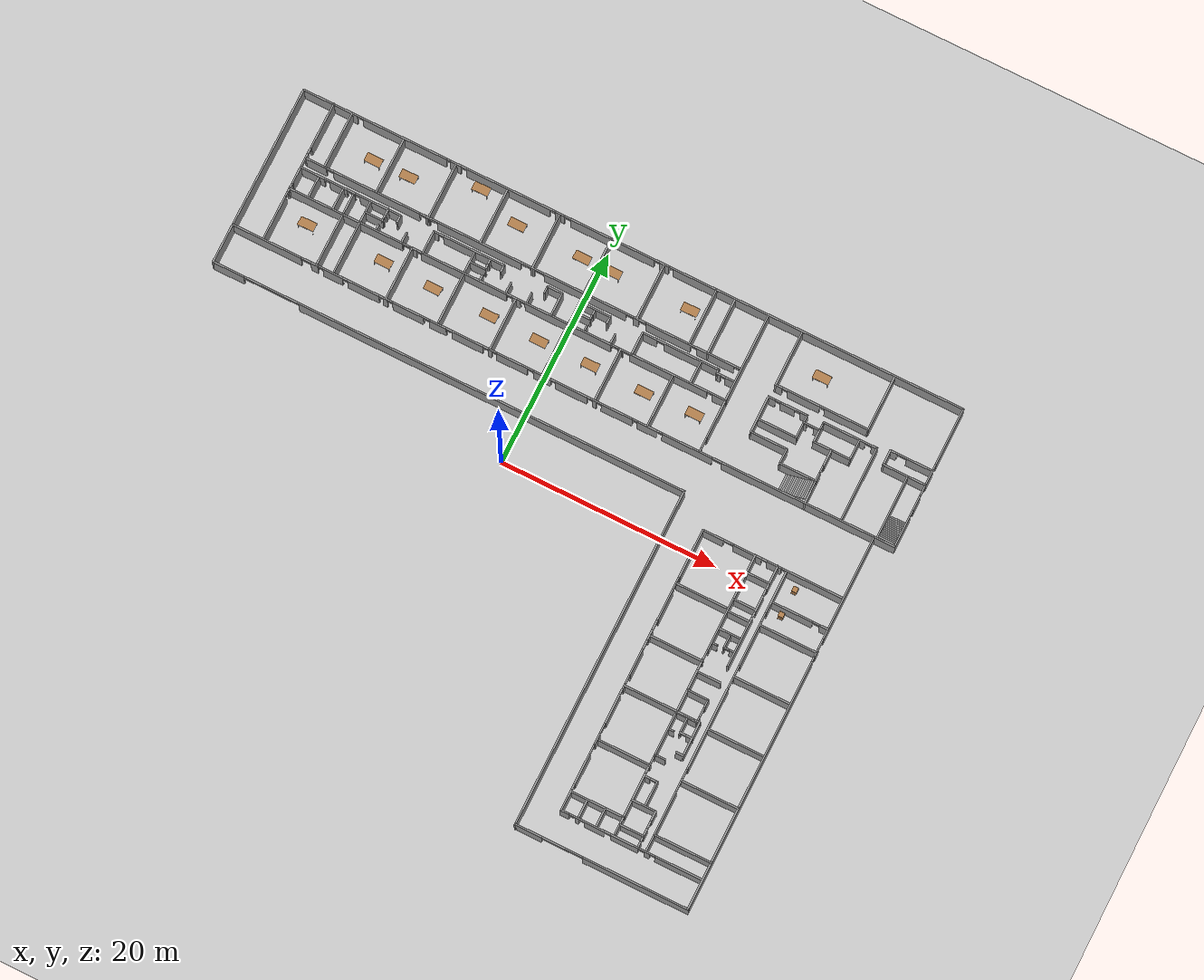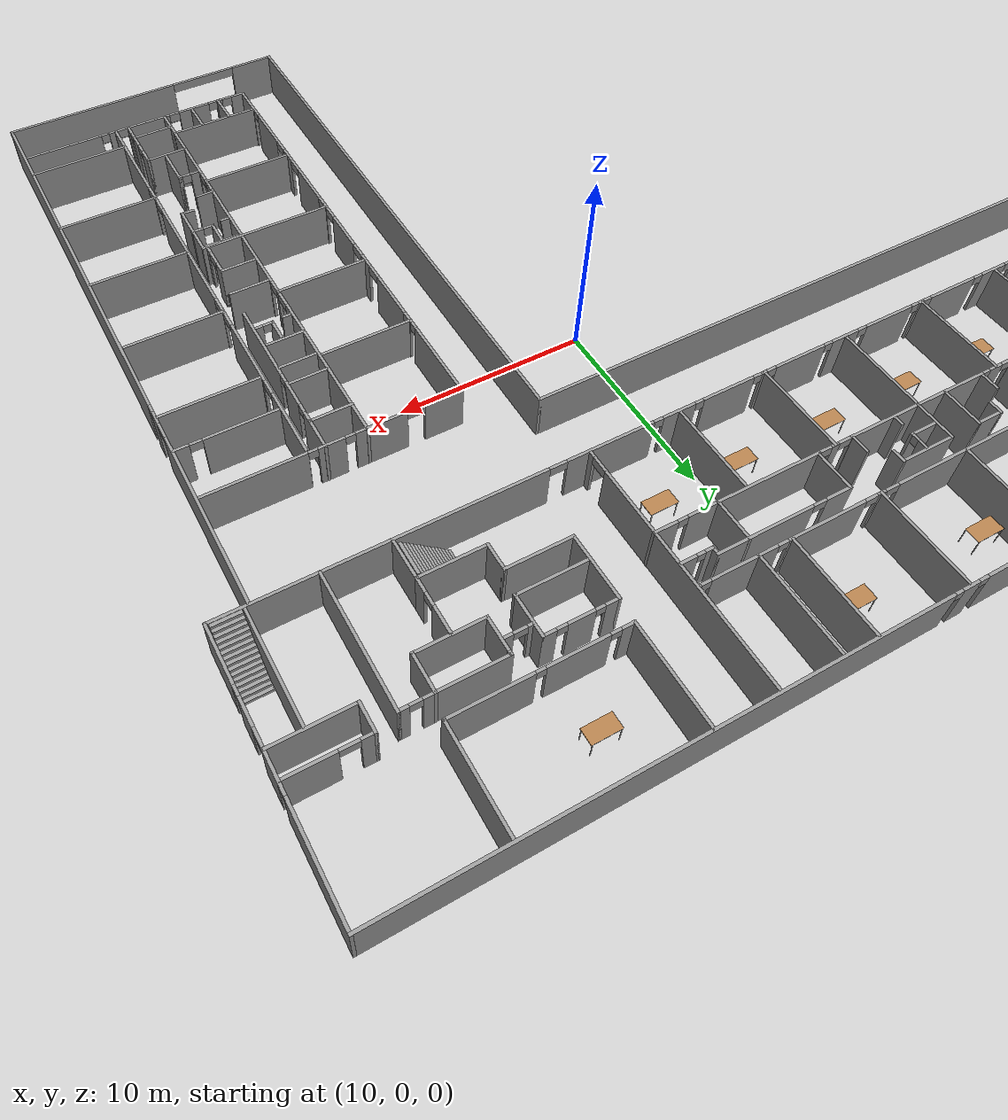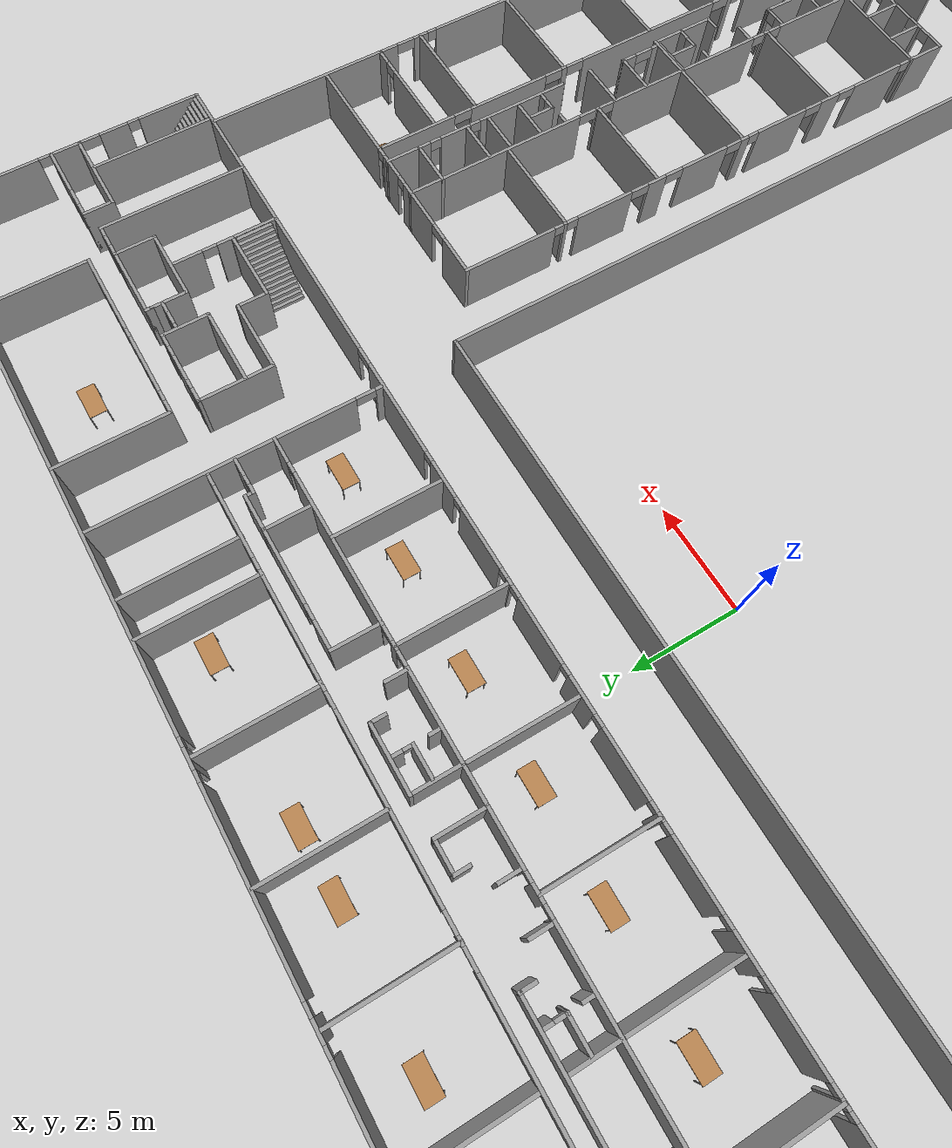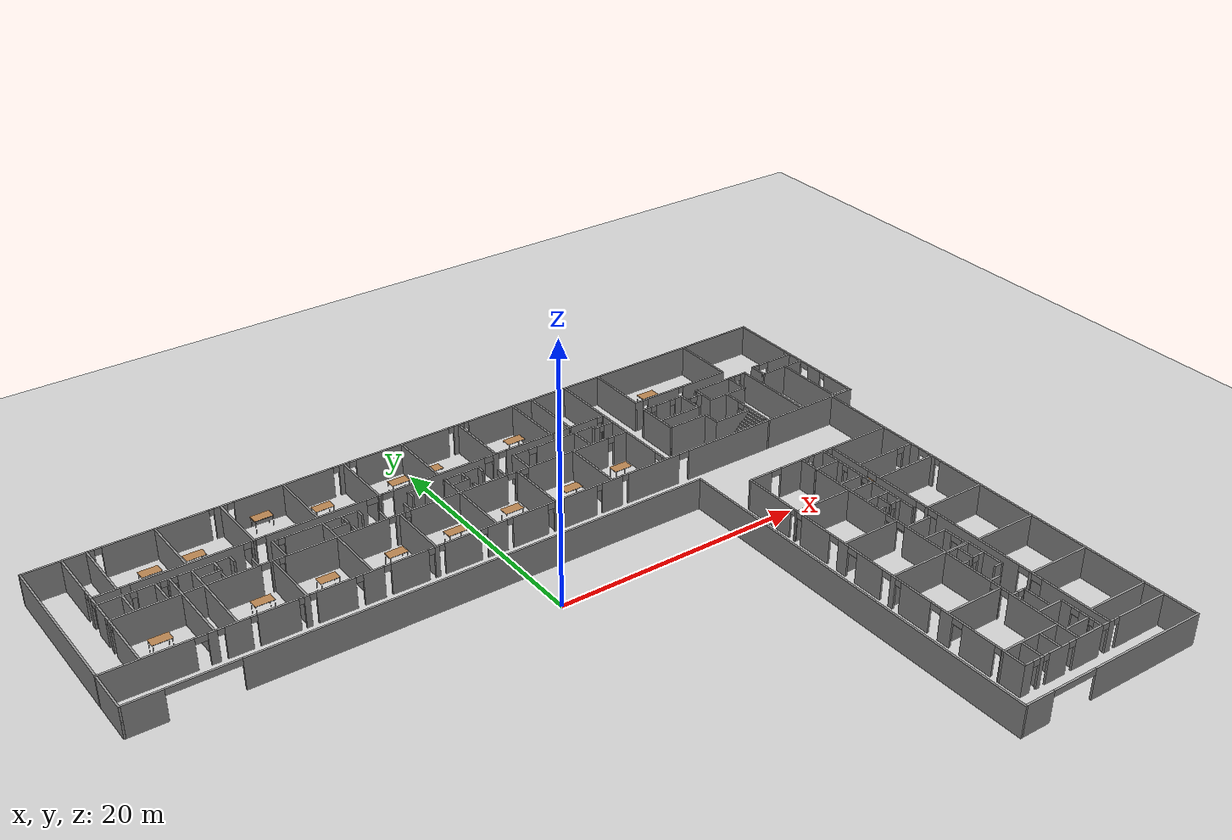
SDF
<sdf version="1.6">
 <world name="default">
  <light name="sun" type="directional">
   <pose>0 0 10 0 -0 0</pose>
   <diffuse>0.8 0.8 0.8 1</diffuse>
   <specular>0.2 0.2 0.2 1</specular>
   <attenuation>
    <range>1000</range>
    <constant>0.9</constant>
    <linear>0.01</linear>
    <quadratic>0.001</quadratic>
   </attenuation>
   <direction>-0.5 0.1 -0.9</direction>
  </light>
  <model name="ground_plane">
   <static>1</static>
   <link name="link">
    <collision name="collision">
     <geometry><plane><normal>0 0 1</normal><size>100 100</size></plane></geometry>
     <surface><friction><ode><mu>100</mu><mu2>50</mu2></ode></friction></surface>
    </collision>
    <visual name="visual">
     <cast_shadows>0</cast_shadows>
     <geometry><plane><normal>0 0 1</normal><size>100 100</size></plane></geometry>
     <material>
      <script><uri>file://media/materials/scripts/gazebo.material</uri><name>Gazebo/Grey</name></script>
     </material>
    </visual>
   </link>
  </model>
  <gravity>0 0 -9.8</gravity>
  <magnetic_field>6e-06 2.3e-05 -4.2e-05</magnetic_field>
  <atmosphere type="adiabatic"/>
  <physics name="default_physics" default="0" type="ode">
   <max_step_size>0.001</max_step_size>
   <real_time_factor>1</real_time_factor>
   <real_time_update_rate>1000</real_time_update_rate>
  </physics>
  <scene><ambient>0.4 0.4 0.4 1</ambient><background>0.7 0.7 0.7 1</background><shadows>1</shadows></scene>
  <spherical_coordinates>
   <surface_model>EARTH_WGS84</surface_model>
   <latitude_deg>0</latitude_deg>
   <longitude_deg>0</longitude_deg>
   <elevation>0</elevation>
   <heading_deg>0</heading_deg>
  </spherical_coordinates>
  <model name="se1f1_fin.sdf">
   <pose>1.7543 -3.15003 0 0 -0 0</pose>
   <link name="Stairs_0">
    <visual name="Stairs_0_Visual_0">
     <pose>20.0688 12.0461 0.083333 0 -0 1.5708</pose>
     <geometry><box><size>1.71709 0.168037 0.166667</size></box></geometry>
     <material>
      <script><uri>file://media/materials/scripts/gazebo.material</uri><name>Gazebo/Grey</name></script>
      <ambient>1 1 1 1</ambient>
     </material>
     <meta><layer>0</layer></meta>
    </visual>
    <collision name="Stairs_0_Collision_0">
     <geometry><box><size>1.71709 0.168037 0.166667</size></box></geometry>
     <pose>20.0688 12.0461 0.083333 0 -0 1.5708</pose>
    </collision>
    <visual name="Stairs_0_Visual_1">
     <pose>20.2369 12.0461 0.25 0 -0 1.5708</pose>
     <geometry><box><size>1.71709 0.168037 0.166667</size></box></geometry>
     <material>
      <script><uri>file://media/materials/scripts/gazebo.material</uri><name>Gazebo/Grey</name></script>
      <ambient>1 1 1 1</ambient>
     </material>
     <meta><layer>0</layer></meta>
    </visual>
    <collision name="Stairs_0_Collision_1">
     <geometry><box><size>1.71709 0.168037 0.166667</size></box></geometry>
     <pose>20.2369 12.0461 0.25 0 -0 1.5708</pose>
    </collision>
    <visual name="Stairs_0_Visual_2">
     <pose>20.4049 12.0461 0.416667 0 -0 1.5708</pose>
     <geometry><box><size>1.71709 0.168037 0.166667</size></box></geometry>
     <material>
      <script><uri>file://media/materials/scripts/gazebo.material</uri><name>Gazebo/Grey</name></script>
      <ambient>1 1 1 1</ambient>
     </material>
     <meta><layer>0</layer></meta>
    </visual>
    <collision name="Stairs_0_Collision_2">
     <geometry><box><size>1.71709 0.168037 0.166667</size></box></geometry>
     <pose>20.4049 12.0461 0.416667 0 -0 1.5708</pose>
    </collision>
    <visual name="Stairs_0_Visual_3">
     <pose>20.5729 12.0461 0.583333 0 -0 1.5708</pose>
     <geometry><box><size>1.71709 0.168037 0.166667</size></box></geometry>
     <material>
      <script><uri>file://media/materials/scripts/gazebo.material</uri><name>Gazebo/Grey</name></script>
      <ambient>1 1 1 1</ambient>
     </material>
     <meta><layer>0</layer></meta>
    </visual>
    <collision name="Stairs_0_Collision_3">
     <geometry><box><size>1.71709 0.168037 0.166667</size></box></geometry>
     <pose>20.5729 12.0461 0.583333 0 -0 1.5708</pose>
    </collision>
    <visual name="Stairs_0_Visual_4">
     <pose>20.741 12.0461 0.75 0 -0 1.5708</pose>
     <geometry><box><size>1.71709 0.168037 0.166667</size></box></geometry>
     <material>
      <script><uri>file://media/materials/scripts/gazebo.material</uri><name>Gazebo/Grey</name></script>
      <ambient>1 1 1 1</ambient>
     </material>
     <meta><layer>0</layer></meta>
    </visual>
    <collision name="Stairs_0_Collision_4">
     <geometry><box><size>1.71709 0.168037 0.166667</size></box></geometry>
     <pose>20.741 12.0461 0.75 0 -0 1.5708</pose>
    </collision>
    <visual name="Stairs_0_Visual_5">
     <pose>20.909 12.0461 0.916667 0 -0 1.5708</pose>
     <geometry><box><size>1.71709 0.168037 0.166667</size></box></geometry>
     <material>
      <script><uri>file://media/materials/scripts/gazebo.material</uri><name>Gazebo/Grey</name></script>
      <ambient>1 1 1 1</ambient>
     </material>
     <meta><layer>0</layer></meta>
    </visual>
    <collision name="Stairs_0_Collision_5">
     <geometry><box><size>1.71709 0.168037 0.166667</size></box></geometry>
     <pose>20.909 12.0461 0.916667 0 -0 1.5708</pose>
    </collision>
    <visual name="Stairs_0_Visual_6">
     <pose>21.077 12.0461 1.08333 0 -0 1.5708</pose>
     <geometry><box><size>1.71709 0.168037 0.166667</size></box></geometry>
     <material>
      <script><uri>file://media/materials/scripts/gazebo.material</uri><name>Gazebo/Grey</name></script>
      <ambient>1 1 1 1</ambient>
     </material>
     <meta><layer>0</layer></meta>
    </visual>
    <collision name="Stairs_0_Collision_6">
     <geometry><box><size>1.71709 0.168037 0.166667</size></box></geometry>
     <pose>21.077 12.0461 1.08333 0 -0 1.5708</pose>
    </collision>
    <visual name="Stairs_0_Visual_7">
     <pose>21.2451 12.0461 1.25 0 -0 1.5708</pose>
     <geometry><box><size>1.71709 0.168037 0.166667</size></box></geometry>
     <material>
      <script><uri>file://media/materials/scripts/gazebo.material</uri><name>Gazebo/Grey</name></script>
      <ambient>1 1 1 1</ambient>
     </material>
     <meta><layer>0</layer></meta>
    </visual>
    <collision name="Stairs_0_Collision_7">
     <geometry><box><size>1.71709 0.168037 0.166667</size></box></geometry>
     <pose>21.2451 12.0461 1.25 0 -0 1.5708</pose>
    </collision>
    <visual name="Stairs_0_Visual_8">
     <pose>21.4131 12.0461 1.41667 0 -0 1.5708</pose>
     <geometry><box><size>1.71709 0.168037 0.166667</size></box></geometry>
     <material>
      <script><uri>file://media/materials/scripts/gazebo.material</uri><name>Gazebo/Grey</name></script>
      <ambient>1 1 1 1</ambient>
     </material>
     <meta><layer>0</layer></meta>
    </visual>
    <collision name="Stairs_0_Collision_8">
     <geometry><box><size>1.71709 0.168037 0.166667</size></box></geometry>
     <pose>21.4131 12.0461 1.41667 0 -0 1.5708</pose>
    </collision>
    <visual name="Stairs_0_Visual_9">
     <pose>21.5812 12.0461 1.58333 0 -0 1.5708</pose>
     <geometry><box><size>1.71709 0.168037 0.166667</size></box></geometry>
     <material>
      <script><uri>file://media/materials/scripts/gazebo.material</uri><name>Gazebo/Grey</name></script>
      <ambient>1 1 1 1</ambient>
     </material>
     <meta><layer>0</layer></meta>
    </visual>
    <collision name="Stairs_0_Collision_9">
     <geometry><box><size>1.71709 0.168037 0.166667</size></box></geometry>
     <pose>21.5812 12.0461 1.58333 0 -0 1.5708</pose>
    </collision>
    <visual name="Stairs_0_Visual_10">
     <pose>21.7492 12.0461 1.75 0 -0 1.5708</pose>
     <geometry><box><size>1.71709 0.168037 0.166667</size></box></geometry>
     <material>
      <script><uri>file://media/materials/scripts/gazebo.material</uri><name>Gazebo/Grey</name></script>
      <ambient>1 1 1 1</ambient>
     </material>
     <meta><layer>0</layer></meta>
    </visual>
    <collision name="Stairs_0_Collision_10">
     <geometry><box><size>1.71709 0.168037 0.166667</size></box></geometry>
     <pose>21.7492 12.0461 1.75 0 -0 1.5708</pose>
    </collision>
    <visual name="Stairs_0_Visual_11">
     <pose>21.9172 12.0461 1.91667 0 -0 1.5708</pose>
     <geometry><box><size>1.71709 0.168037 0.166667</size></box></geometry>
     <material>
      <script><uri>file://media/materials/scripts/gazebo.material</uri><name>Gazebo/Grey</name></script>
      <ambient>1 1 1 1</ambient>
     </material>
     <meta><layer>0</layer></meta>
    </visual>
    <collision name="Stairs_0_Collision_11">
     <geometry><box><size>1.71709 0.168037 0.166667</size></box></geometry>
     <pose>21.9172 12.0461 1.91667 0 -0 1.5708</pose>
    </collision>
    <visual name="Stairs_0_Visual_12">
     <pose>22.0853 12.0461 2.08333 0 -0 1.5708</pose>
     <geometry><box><size>1.71709 0.168037 0.166667</size></box></geometry>
     <material>
      <script><uri>file://media/materials/scripts/gazebo.material</uri><name>Gazebo/Grey</name></script>
      <ambient>1 1 1 1</ambient>
     </material>
     <meta><layer>0</layer></meta>
    </visual>
    <collision name="Stairs_0_Collision_12">
     <geometry><box><size>1.71709 0.168037 0.166667</size></box></geometry>
     <pose>22.0853 12.0461 2.08333 0 -0 1.5708</pose>
    </collision>
    <visual name="Stairs_0_Visual_13">
     <pose>22.2533 12.0461 2.25 0 -0 1.5708</pose>
     <geometry><box><size>1.71709 0.168037 0.166667</size></box></geometry>
     <material>
      <script><uri>file://media/materials/scripts/gazebo.material</uri><name>Gazebo/Grey</name></script>
      <ambient>1 1 1 1</ambient>
     </material>
     <meta><layer>0</layer></meta>
    </visual>
    <collision name="Stairs_0_Collision_13">
     <geometry><box><size>1.71709 0.168037 0.166667</size></box></geometry>
     <pose>22.2533 12.0461 2.25 0 -0 1.5708</pose>
    </collision>
    <visual name="Stairs_0_Visual_14">
     <pose>22.4213 12.0461 2.41667 0 -0 1.5708</pose>
     <geometry><box><size>1.71709 0.168037 0.166667</size></box></geometry>
     <material>
      <script><uri>file://media/materials/scripts/gazebo.material</uri><name>Gazebo/Grey</name></script>
      <ambient>1 1 1 1</ambient>
     </material>
     <meta><layer>0</layer></meta>
    </visual>
    <collision name="Stairs_0_Collision_14">
     <geometry><box><size>1.71709 0.168037 0.166667</size></box></geometry>
     <pose>22.4213 12.0461 2.41667 0 -0 1.5708</pose>
    </collision>
   </link>
   <link name="Stairs_1">
    <visual name="Stairs_1_Visual_0">
     <pose>30.095 13.5256 0.083333 0 -0 0</pose>
     <geometry><box><size>1.41976 0.173867 0.166667</size></box></geometry>
     <material>
      <script><uri>file://media/materials/scripts/gazebo.material</uri><name>Gazebo/Grey</name></script>
      <ambient>1 1 1 1</ambient>
     </material>
     <meta><layer>0</layer></meta>
    </visual>
    <collision name="Stairs_1_Collision_0">
     <geometry><box><size>1.41976 0.173867 0.166667</size></box></geometry>
     <pose>30.095 13.5256 0.083333 0 -0 0</pose>
    </collision>
    <visual name="Stairs_1_Visual_1">
     <pose>30.095 13.3517 0.25 0 -0 0</pose>
     <geometry><box><size>1.41976 0.173867 0.166667</size></box></geometry>
     <material>
      <script><uri>file://media/materials/scripts/gazebo.material</uri><name>Gazebo/Grey</name></script>
      <ambient>1 1 1 1</ambient>
     </material>
     <meta><layer>0</layer></meta>
    </visual>
    <collision name="Stairs_1_Collision_1">
     <geometry><box><size>1.41976 0.173867 0.166667</size></box></geometry>
     <pose>30.095 13.3517 0.25 0 -0 0</pose>
    </collision>
    <visual name="Stairs_1_Visual_2">
     <pose>30.095 13.1778 0.416667 0 -0 0</pose>
     <geometry><box><size>1.41976 0.173867 0.166667</size></box></geometry>
     <material>
      <script><uri>file://media/materials/scripts/gazebo.material</uri><name>Gazebo/Grey</name></script>
      <ambient>1 1 1 1</ambient>
     </material>
     <meta><layer>0</layer></meta>
    </visual>
    <collision name="Stairs_1_Collision_2">
     <geometry><box><size>1.41976 0.173867 0.166667</size></box></geometry>
     <pose>30.095 13.1778 0.416667 0 -0 0</pose>
    </collision>
    <visual name="Stairs_1_Visual_3">
     <pose>30.095 13.004 0.583333 0 -0 0</pose>
     <geometry><box><size>1.41976 0.173867 0.166667</size></box></geometry>
     <material>
      <script><uri>file://media/materials/scripts/gazebo.material</uri><name>Gazebo/Grey</name></script>
      <ambient>1 1 1 1</ambient>
     </material>
     <meta><layer>0</layer></meta>
    </visual>
    <collision name="Stairs_1_Collision_3">
     <geometry><box><size>1.41976 0.173867 0.166667</size></box></geometry>
     <pose>30.095 13.004 0.583333 0 -0 0</pose>
    </collision>
    <visual name="Stairs_1_Visual_4">
     <pose>30.095 12.8301 0.75 0 -0 0</pose>
     <geometry><box><size>1.41976 0.173867 0.166667</size></box></geometry>
     <material>
      <script><uri>file://media/materials/scripts/gazebo.material</uri><name>Gazebo/Grey</name></script>
      <ambient>1 1 1 1</ambient>
     </material>
     <meta><layer>0</layer></meta>
    </visual>
    <collision name="Stairs_1_Collision_4">
     <geometry><box><size>1.41976 0.173867 0.166667</size></box></geometry>
     <pose>30.095 12.8301 0.75 0 -0 0</pose>
    </collision>
    <visual name="Stairs_1_Visual_5">
     <pose>30.095 12.6562 0.916667 0 -0 0</pose>
     <geometry><box><size>1.41976 0.173867 0.166667</size></box></geometry>
     <material>
      <script><uri>file://media/materials/scripts/gazebo.material</uri><name>Gazebo/Grey</name></script>
      <ambient>1 1 1 1</ambient>
     </material>
     <meta><layer>0</layer></meta>
    </visual>
    <collision name="Stairs_1_Collision_5">
     <geometry><box><size>1.41976 0.173867 0.166667</size></box></geometry>
     <pose>30.095 12.6562 0.916667 0 -0 0</pose>
    </collision>
    <visual name="Stairs_1_Visual_6">
     <pose>30.095 12.4824 1.08333 0 -0 0</pose>
     <geometry><box><size>1.41976 0.173867 0.166667</size></box></geometry>
     <material>
      <script><uri>file://media/materials/scripts/gazebo.material</uri><name>Gazebo/Grey</name></script>
      <ambient>1 1 1 1</ambient>
     </material>
     <meta><layer>0</layer></meta>
    </visual>
    <collision name="Stairs_1_Collision_6">
     <geometry><box><size>1.41976 0.173867 0.166667</size></box></geometry>
     <pose>30.095 12.4824 1.08333 0 -0 0</pose>
    </collision>
    <visual name="Stairs_1_Visual_7">
     <pose>30.095 12.3085 1.25 0 -0 0</pose>
     <geometry><box><size>1.41976 0.173867 0.166667</size></box></geometry>
     <material>
      <script><uri>file://media/materials/scripts/gazebo.material</uri><name>Gazebo/Grey</name></script>
      <ambient>1 1 1 1</ambient>
     </material>
     <meta><layer>0</layer></meta>
    </visual>
    <collision name="Stairs_1_Collision_7">
     <geometry><box><size>1.41976 0.173867 0.166667</size></box></geometry>
     <pose>30.095 12.3085 1.25 0 -0 0</pose>
    </collision>
    <visual name="Stairs_1_Visual_8">
     <pose>30.095 12.1346 1.41667 0 -0 0</pose>
     <geometry><box><size>1.41976 0.173867 0.166667</size></box></geometry>
     <material>
      <script><uri>file://media/materials/scripts/gazebo.material</uri><name>Gazebo/Grey</name></script>
      <ambient>1 1 1 1</ambient>
     </material>
     <meta><layer>0</layer></meta>
    </visual>
    <collision name="Stairs_1_Collision_8">
     <geometry><box><size>1.41976 0.173867 0.166667</size></box></geometry>
     <pose>30.095 12.1346 1.41667 0 -0 0</pose>
    </collision>
    <visual name="Stairs_1_Visual_9">
     <pose>30.095 11.9608 1.58333 0 -0 0</pose>
     <geometry><box><size>1.41976 0.173867 0.166667</size></box></geometry>
     <material>
      <script><uri>file://media/materials/scripts/gazebo.material</uri><name>Gazebo/Grey</name></script>
      <ambient>1 1 1 1</ambient>
     </material>
     <meta><layer>0</layer></meta>
    </visual>
    <collision name="Stairs_1_Collision_9">
     <geometry><box><size>1.41976 0.173867 0.166667</size></box></geometry>
     <pose>30.095 11.9608 1.58333 0 -0 0</pose>
    </collision>
    <visual name="Stairs_1_Visual_10">
     <pose>30.095 11.7869 1.75 0 -0 0</pose>
     <geometry><box><size>1.41976 0.173867 0.166667</size></box></geometry>
     <material>
      <script><uri>file://media/materials/scripts/gazebo.material</uri><name>Gazebo/Grey</name></script>
      <ambient>1 1 1 1</ambient>
     </material>
     <meta><layer>0</layer></meta>
    </visual>
    <collision name="Stairs_1_Collision_10">
     <geometry><box><size>1.41976 0.173867 0.166667</size></box></geometry>
     <pose>30.095 11.7869 1.75 0 -0 0</pose>
    </collision>
    <visual name="Stairs_1_Visual_11">
     <pose>30.095 11.613 1.91667 0 -0 0</pose>
     <geometry><box><size>1.41976 0.173867 0.166667</size></box></geometry>
     <material>
      <script><uri>file://media/materials/scripts/gazebo.material</uri><name>Gazebo/Grey</name></script>
      <ambient>1 1 1 1</ambient>
     </material>
     <meta><layer>0</layer></meta>
    </visual>
    <collision name="Stairs_1_Collision_11">
     <geometry><box><size>1.41976 0.173867 0.166667</size></box></geometry>
     <pose>30.095 11.613 1.91667 0 -0 0</pose>
    </collision>
    <visual name="Stairs_1_Visual_12">
     <pose>30.095 11.4391 2.08333 0 -0 0</pose>
     <geometry><box><size>1.41976 0.173867 0.166667</size></box></geometry>
     <material>
      <script><uri>file://media/materials/scripts/gazebo.material</uri><name>Gazebo/Grey</name></script>
      <ambient>1 1 1 1</ambient>
     </material>
     <meta><layer>0</layer></meta>
    </visual>
    <collision name="Stairs_1_Collision_12">
     <geometry><box><size>1.41976 0.173867 0.166667</size></box></geometry>
     <pose>30.095 11.4391 2.08333 0 -0 0</pose>
    </collision>
    <visual name="Stairs_1_Visual_13">
     <pose>30.095 11.2653 2.25 0 -0 0</pose>
     <geometry><box><size>1.41976 0.173867 0.166667</size></box></geometry>
     <material>
      <script><uri>file://media/materials/scripts/gazebo.material</uri><name>Gazebo/Grey</name></script>
      <ambient>1 1 1 1</ambient>
     </material>
     <meta><layer>0</layer></meta>
    </visual>
    <collision name="Stairs_1_Collision_13">
     <geometry><box><size>1.41976 0.173867 0.166667</size></box></geometry>
     <pose>30.095 11.2653 2.25 0 -0 0</pose>
    </collision>
    <visual name="Stairs_1_Visual_14">
     <pose>30.095 11.0914 2.41667 0 -0 0</pose>
     <geometry><box><size>1.41976 0.173867 0.166667</size></box></geometry>
     <material>
      <script><uri>file://media/materials/scripts/gazebo.material</uri><name>Gazebo/Grey</name></script>
      <ambient>1 1 1 1</ambient>
     </material>
     <meta><layer>0</layer></meta>
    </visual>
    <collision name="Stairs_1_Collision_14">
     <geometry><box><size>1.41976 0.173867 0.166667</size></box></geometry>
     <pose>30.095 11.0914 2.41667 0 -0 0</pose>
    </collision>
   </link>
   <link name="Wall_0">
    <pose>0 24.0175 0 0 -0 0</pose>
    <visual name="Wall_0_Visual_0">
     <pose>-28.4069 0 1.25 0 -0 0</pose>
     <geometry><box><size>5.18629 0.15 2.5</size></box></geometry>
     <material>
      <script><uri>file://media/materials/scripts/gazebo.material</uri><name>Gazebo/Grey</name></script>
      <ambient>1 1 1 1</ambient>
     </material>
     <meta><layer>0</layer></meta>
    </visual>
    <collision name="Wall_0_Collision_0">
     <geometry><box><size>5.18629 0.15 2.5</size></box></geometry>
     <pose>-28.4069 0 1.25 0 -0 0</pose>
    </collision>
    <visual name="Wall_0_Visual_1">
     <pose>-21.341 0 1.25 0 -0 0</pose>
     <geometry><box><size>7.88001 0.15 2.5</size></box></geometry>
     <material>
      <script><uri>file://media/materials/scripts/gazebo.material</uri><name>Gazebo/Grey</name></script>
      <ambient>1 1 1 1</ambient>
     </material>
     <meta><layer>0</layer></meta>
    </visual>
    <collision name="Wall_0_Collision_1">
     <geometry><box><size>7.88001 0.15 2.5</size></box></geometry>
     <pose>-21.341 0 1.25 0 -0 0</pose>
    </collision>
    <visual name="Wall_0_Visual_2">
     <pose>-16.5312 0 1.25 0 -0 0</pose>
     <geometry><box><size>1.02391 0.15 2.5</size></box></geometry>
     <material>
      <script><uri>file://media/materials/scripts/gazebo.material</uri><name>Gazebo/Grey</name></script>
      <ambient>1 1 1 1</ambient>
     </material>
     <meta><layer>0</layer></meta>
    </visual>
    <collision name="Wall_0_Collision_2">
     <geometry><box><size>1.02391 0.15 2.5</size></box></geometry>
     <pose>-16.5312 0 1.25 0 -0 0</pose>
    </collision>
    <visual name="Wall_0_Visual_3">
     <pose>-11.5728 0 1.25 0 -0 0</pose>
     <geometry><box><size>7.86252 0.15 2.5</size></box></geometry>
     <material>
      <script><uri>file://media/materials/scripts/gazebo.material</uri><name>Gazebo/Grey</name></script>
      <ambient>1 1 1 1</ambient>
     </material>
     <meta><layer>0</layer></meta>
    </visual>
    <collision name="Wall_0_Collision_3">
     <geometry><box><size>7.86252 0.15 2.5</size></box></geometry>
     <pose>-11.5728 0 1.25 0 -0 0</pose>
    </collision>
    <visual name="Wall_0_Visual_4">
     <pose>-6.72368 0 1.25 0 -0 0</pose>
     <geometry><box><size>0.875241 0.15 2.5</size></box></geometry>
     <material>
      <script><uri>file://media/materials/scripts/gazebo.material</uri><name>Gazebo/Grey</name></script>
      <ambient>1 1 1 1</ambient>
     </material>
     <meta><layer>0</layer></meta>
    </visual>
    <collision name="Wall_0_Collision_4">
     <geometry><box><size>0.875241 0.15 2.5</size></box></geometry>
     <pose>-6.72368 0 1.25 0 -0 0</pose>
    </collision>
    <visual name="Wall_0_Visual_5">
     <pose>-1.80022 0 1.25 0 -0 0</pose>
     <geometry><box><size>7.87127 0.15 2.5</size></box></geometry>
     <material>
      <script><uri>file://media/materials/scripts/gazebo.material</uri><name>Gazebo/Grey</name></script>
      <ambient>1 1 1 1</ambient>
     </material>
     <meta><layer>0</layer></meta>
    </visual>
    <collision name="Wall_0_Collision_5">
     <geometry><box><size>7.87127 0.15 2.5</size></box></geometry>
     <pose>-1.80022 0 1.25 0 -0 0</pose>
    </collision>
    <visual name="Wall_0_Visual_6">
     <pose>3.06638 0 1.25 0 -0 0</pose>
     <geometry><box><size>0.901476 0.15 2.5</size></box></geometry>
     <material>
      <script><uri>file://media/materials/scripts/gazebo.material</uri><name>Gazebo/Grey</name></script>
      <ambient>1 1 1 1</ambient>
     </material>
     <meta><layer>0</layer></meta>
    </visual>
    <collision name="Wall_0_Collision_6">
     <geometry><box><size>0.901476 0.15 2.5</size></box></geometry>
     <pose>3.06638 0 1.25 0 -0 0</pose>
    </collision>
    <visual name="Wall_0_Visual_7">
     <pose>17.4637 0 1.25 0 -0 0</pose>
     <geometry><box><size>27.0726 0.15 2.5</size></box></geometry>
     <material>
      <script><uri>file://media/materials/scripts/gazebo.material</uri><name>Gazebo/Grey</name></script>
      <ambient>1 1 1 1</ambient>
     </material>
     <meta><layer>0</layer></meta>
    </visual>
    <collision name="Wall_0_Collision_7">
     <geometry><box><size>27.0726 0.15 2.5</size></box></geometry>
     <pose>17.4637 0 1.25 0 -0 0</pose>
    </collision>
    <visual name="Wall_0_Visual_8">
     <pose>-25.5474 0 2.25 0 -0 0</pose>
     <geometry><box><size>0.532709 0.15 0.5</size></box></geometry>
     <material>
      <script><uri>file://media/materials/scripts/gazebo.material</uri><name>Gazebo/Grey</name></script>
      <ambient>1 1 1 1</ambient>
     </material>
     <meta><layer>0</layer></meta>
    </visual>
    <collision name="Wall_0_Collision_8">
     <geometry><box><size>0.532709 0.15 0.5</size></box></geometry>
     <pose>-25.5474 0 2.25 0 -0 0</pose>
    </collision>
    <visual name="Wall_0_Visual_9">
     <pose>-17.2221 0 2.25 0 -0 0</pose>
     <geometry><box><size>0.357808 0.15 0.5</size></box></geometry>
     <material>
      <script><uri>file://media/materials/scripts/gazebo.material</uri><name>Gazebo/Grey</name></script>
      <ambient>1 1 1 1</ambient>
     </material>
     <meta><layer>0</layer></meta>
    </visual>
    <collision name="Wall_0_Collision_9">
     <geometry><box><size>0.357808 0.15 0.5</size></box></geometry>
     <pose>-17.2221 0 2.25 0 -0 0</pose>
    </collision>
    <visual name="Wall_0_Visual_10">
     <pose>-15.7617 0 2.25 0 -0 0</pose>
     <geometry><box><size>0.515219 0.15 0.5</size></box></geometry>
     <material>
      <script><uri>file://media/materials/scripts/gazebo.material</uri><name>Gazebo/Grey</name></script>
      <ambient>1 1 1 1</ambient>
     </material>
     <meta><layer>0</layer></meta>
    </visual>
    <collision name="Wall_0_Collision_10">
     <geometry><box><size>0.515219 0.15 0.5</size></box></geometry>
     <pose>-15.7617 0 2.25 0 -0 0</pose>
    </collision>
    <visual name="Wall_0_Visual_11">
     <pose>-7.40142 0 2.25 0 -0 0</pose>
     <geometry><box><size>0.480239 0.15 0.5</size></box></geometry>
     <material>
      <script><uri>file://media/materials/scripts/gazebo.material</uri><name>Gazebo/Grey</name></script>
      <ambient>1 1 1 1</ambient>
     </material>
     <meta><layer>0</layer></meta>
    </visual>
    <collision name="Wall_0_Collision_11">
     <geometry><box><size>0.480239 0.15 0.5</size></box></geometry>
     <pose>-7.40142 0 2.25 0 -0 0</pose>
    </collision>
    <visual name="Wall_0_Visual_12">
     <pose>-6.01096 0 2.25 0 -0 0</pose>
     <geometry><box><size>0.550199 0.15 0.5</size></box></geometry>
     <material>
      <script><uri>file://media/materials/scripts/gazebo.material</uri><name>Gazebo/Grey</name></script>
      <ambient>1 1 1 1</ambient>
     </material>
     <meta><layer>0</layer></meta>
    </visual>
    <collision name="Wall_0_Collision_12">
     <geometry><box><size>0.550199 0.15 0.5</size></box></geometry>
     <pose>-6.01096 0 2.25 0 -0 0</pose>
    </collision>
    <visual name="Wall_0_Visual_13">
     <pose>2.37553 0 2.25 0 -0 0</pose>
     <geometry><box><size>0.480239 0.15 0.5</size></box></geometry>
     <material>
      <script><uri>file://media/materials/scripts/gazebo.material</uri><name>Gazebo/Grey</name></script>
      <ambient>1 1 1 1</ambient>
     </material>
     <meta><layer>0</layer></meta>
    </visual>
    <collision name="Wall_0_Collision_13">
     <geometry><box><size>0.480239 0.15 0.5</size></box></geometry>
     <pose>2.37553 0 2.25 0 -0 0</pose>
    </collision>
    <visual name="Wall_0_Visual_14">
     <pose>3.72226 0 2.25 0 -0 0</pose>
     <geometry><box><size>0.410278 0.15 0.5</size></box></geometry>
     <material>
      <script><uri>file://media/materials/scripts/gazebo.material</uri><name>Gazebo/Grey</name></script>
      <ambient>1 1 1 1</ambient>
     </material>
     <meta><layer>0</layer></meta>
    </visual>
    <collision name="Wall_0_Collision_14">
     <geometry><box><size>0.410278 0.15 0.5</size></box></geometry>
     <pose>3.72226 0 2.25 0 -0 0</pose>
    </collision>
   </link>
   <link name="Wall_101">
    <collision name="Wall_101_Collision">
     <geometry><box><size>4.75 0.15 2.5</size></box></geometry>
     <pose>0 0 1.25 0 -0 0</pose>
    </collision>
    <visual name="Wall_101_Visual">
     <pose>0 0 1.25 0 -0 0</pose>
     <geometry><box><size>4.75 0.15 2.5</size></box></geometry>
     <material>
      <script><uri>file://media/materials/scripts/gazebo.material</uri><name>Gazebo/Grey</name></script>
      <ambient>1 1 1 1</ambient>
     </material>
     <meta><layer>0</layer></meta>
    </visual>
    <pose>-11.6538 13.3735 0 0 -0 1.5708</pose>
   </link>
   <link name="Wall_103">
    <collision name="Wall_103_Collision">
     <geometry><box><size>5 0.15 2.5</size></box></geometry>
     <pose>0 0 1.25 0 -0 0</pose>
    </collision>
    <visual name="Wall_103_Visual">
     <pose>0 0 1.25 0 -0 0</pose>
     <geometry><box><size>5 0.15 2.5</size></box></geometry>
     <material>
      <script><uri>file://media/materials/scripts/gazebo.material</uri><name>Gazebo/Grey</name></script>
      <ambient>1 1 1 1</ambient>
     </material>
     <meta><layer>0</layer></meta>
    </visual>
    <pose>-6.75659 13.3935 0 0 -0 1.5708</pose>
   </link>
   <link name="Wall_106">
    <collision name="Wall_106_Collision">
     <geometry><box><size>4.75 0.15 2.5</size></box></geometry>
     <pose>0 0 1.25 0 -0 0</pose>
    </collision>
    <visual name="Wall_106_Visual">
     <pose>0 0 1.25 0 -0 0</pose>
     <geometry><box><size>4.75 0.15 2.5</size></box></geometry>
     <material>
      <script><uri>file://media/materials/scripts/gazebo.material</uri><name>Gazebo/Grey</name></script>
      <ambient>1 1 1 1</ambient>
     </material>
     <meta><layer>0</layer></meta>
    </visual>
    <pose>-1.85938 13.3735 0 0 -0 1.5708</pose>
   </link>
   <link name="Wall_108">
    <collision name="Wall_108_Collision">
     <geometry><box><size>5 0.15 2.5</size></box></geometry>
     <pose>0 0 1.25 0 -0 0</pose>
    </collision>
    <visual name="Wall_108_Visual">
     <pose>0 0 1.25 0 -0 0</pose>
     <geometry><box><size>5 0.15 2.5</size></box></geometry>
     <material>
      <script><uri>file://media/materials/scripts/gazebo.material</uri><name>Gazebo/Grey</name></script>
      <ambient>1 1 1 1</ambient>
     </material>
     <meta><layer>0</layer></meta>
    </visual>
    <pose>3.03784 13.3935 0 0 -0 1.5708</pose>
   </link>
   <link name="Wall_11">
    <pose>29.0441 -6.57969 0 0 0 -1.5708</pose>
    <visual name="Wall_11_Visual_0">
     <pose>-12.659 0 1.25 0 -0 0</pose>
     <geometry><box><size>9.68204 0.15 2.5</size></box></geometry>
     <material>
      <script><uri>file://media/materials/scripts/gazebo.material</uri><name>Gazebo/Grey</name></script>
      <ambient>1 1 1 1</ambient>
     </material>
     <meta><layer>0</layer></meta>
    </visual>
    <collision name="Wall_11_Collision_0">
     <geometry><box><size>9.68204 0.15 2.5</size></box></geometry>
     <pose>-12.659 0 1.25 0 -0 0</pose>
    </collision>
    <visual name="Wall_11_Visual_1">
     <pose>-6.53827 0 1.25 0 -0 0</pose>
     <geometry><box><size>0.75937 0.15 2.5</size></box></geometry>
     <material>
      <script><uri>file://media/materials/scripts/gazebo.material</uri><name>Gazebo/Grey</name></script>
      <ambient>1 1 1 1</ambient>
     </material>
     <meta><layer>0</layer></meta>
    </visual>
    <collision name="Wall_11_Collision_1">
     <geometry><box><size>0.75937 0.15 2.5</size></box></geometry>
     <pose>-6.53827 0 1.25 0 -0 0</pose>
    </collision>
    <visual name="Wall_11_Visual_2">
     <pose>5.90951 0 1.25 0 -0 0</pose>
     <geometry><box><size>23.181 0.15 2.5</size></box></geometry>
     <material>
      <script><uri>file://media/materials/scripts/gazebo.material</uri><name>Gazebo/Grey</name></script>
      <ambient>1 1 1 1</ambient>
     </material>
     <meta><layer>0</layer></meta>
    </visual>
    <collision name="Wall_11_Collision_2">
     <geometry><box><size>23.181 0.15 2.5</size></box></geometry>
     <pose>5.90951 0 1.25 0 -0 0</pose>
    </collision>
    <visual name="Wall_11_Visual_3">
     <pose>-7.36796 0 2.25 0 -0 0</pose>
     <geometry><box><size>0.9 0.15 0.5</size></box></geometry>
     <material>
      <script><uri>file://media/materials/scripts/gazebo.material</uri><name>Gazebo/Grey</name></script>
      <ambient>1 1 1 1</ambient>
     </material>
     <meta><layer>0</layer></meta>
    </visual>
    <collision name="Wall_11_Collision_3">
     <geometry><box><size>0.9 0.15 0.5</size></box></geometry>
     <pose>-7.36796 0 2.25 0 -0 0</pose>
    </collision>
    <visual name="Wall_11_Visual_4">
     <pose>-5.91978 0 2.25 0 -0 0</pose>
     <geometry><box><size>0.477615 0.15 0.5</size></box></geometry>
     <material>
      <script><uri>file://media/materials/scripts/gazebo.material</uri><name>Gazebo/Grey</name></script>
      <ambient>1 1 1 1</ambient>
     </material>
     <meta><layer>0</layer></meta>
    </visual>
    <collision name="Wall_11_Collision_4">
     <geometry><box><size>0.477615 0.15 0.5</size></box></geometry>
     <pose>-5.91978 0 2.25 0 -0 0</pose>
    </collision>
   </link>
   <link name="Wall_110">
    <collision name="Wall_110_Collision">
     <geometry><box><size>5 0.15 2.5</size></box></geometry>
     <pose>0 0 1.25 0 -0 0</pose>
    </collision>
    <visual name="Wall_110_Visual">
     <pose>0 0 1.25 0 -0 0</pose>
     <geometry><box><size>5 0.15 2.5</size></box></geometry>
     <material>
      <script><uri>file://media/materials/scripts/gazebo.material</uri><name>Gazebo/Grey</name></script>
      <ambient>1 1 1 1</ambient>
     </material>
     <meta><layer>0</layer></meta>
    </visual>
    <pose>7.95255 13.3935 0 0 -0 1.5708</pose>
   </link>
   <link name="Wall_112">
    <pose>-7.6182 18.7939 0 0 -0 0</pose>
    <visual name="Wall_112_Visual_0">
     <pose>-19.4252 0 1.25 0 -0 0</pose>
     <geometry><box><size>1.89964 0.15 2.5</size></box></geometry>
     <material>
      <script><uri>file://media/materials/scripts/gazebo.material</uri><name>Gazebo/Grey</name></script>
      <ambient>1 1 1 1</ambient>
     </material>
     <meta><layer>0</layer></meta>
    </visual>
    <collision name="Wall_112_Collision_0">
     <geometry><box><size>1.89964 0.15 2.5</size></box></geometry>
     <pose>-19.4252 0 1.25 0 -0 0</pose>
    </collision>
    <visual name="Wall_112_Visual_1">
     <pose>-13.7447 0 1.25 0 -0 0</pose>
     <geometry><box><size>8.15111 0.15 2.5</size></box></geometry>
     <material>
      <script><uri>file://media/materials/scripts/gazebo.material</uri><name>Gazebo/Grey</name></script>
      <ambient>1 1 1 1</ambient>
     </material>
     <meta><layer>0</layer></meta>
    </visual>
    <collision name="Wall_112_Collision_1">
     <geometry><box><size>8.15111 0.15 2.5</size></box></geometry>
     <pose>-13.7447 0 1.25 0 -0 0</pose>
    </collision>
    <visual name="Wall_112_Visual_2">
     <pose>-8.90866 0 1.25 0 -0 0</pose>
     <geometry><box><size>0.38552 0.15 2.5</size></box></geometry>
     <material>
      <script><uri>file://media/materials/scripts/gazebo.material</uri><name>Gazebo/Grey</name></script>
      <ambient>1 1 1 1</ambient>
     </material>
     <meta><layer>0</layer></meta>
    </visual>
    <collision name="Wall_112_Collision_2">
     <geometry><box><size>0.38552 0.15 2.5</size></box></geometry>
     <pose>-8.90866 0 1.25 0 -0 0</pose>
    </collision>
    <visual name="Wall_112_Visual_3">
     <pose>-4.07266 0 1.25 0 -0 0</pose>
     <geometry><box><size>7.83629 0.15 2.5</size></box></geometry>
     <material>
      <script><uri>file://media/materials/scripts/gazebo.material</uri><name>Gazebo/Grey</name></script>
      <ambient>1 1 1 1</ambient>
     </material>
     <meta><layer>0</layer></meta>
    </visual>
    <collision name="Wall_112_Collision_3">
     <geometry><box><size>7.83629 0.15 2.5</size></box></geometry>
     <pose>-4.07266 0 1.25 0 -0 0</pose>
    </collision>
    <visual name="Wall_112_Visual_4">
     <pose>0.933869 0 1.25 0 -0 0</pose>
     <geometry><box><size>0.376774 0.15 2.5</size></box></geometry>
     <material>
      <script><uri>file://media/materials/scripts/gazebo.material</uri><name>Gazebo/Grey</name></script>
      <ambient>1 1 1 1</ambient>
     </material>
     <meta><layer>0</layer></meta>
    </visual>
    <collision name="Wall_112_Collision_4">
     <geometry><box><size>0.376774 0.15 2.5</size></box></geometry>
     <pose>0.933869 0 1.25 0 -0 0</pose>
    </collision>
    <visual name="Wall_112_Visual_5">
     <pose>5.85295 0 1.25 0 -0 0</pose>
     <geometry><box><size>7.66139 0.15 2.5</size></box></geometry>
     <material>
      <script><uri>file://media/materials/scripts/gazebo.material</uri><name>Gazebo/Grey</name></script>
      <ambient>1 1 1 1</ambient>
     </material>
     <meta><layer>0</layer></meta>
    </visual>
    <collision name="Wall_112_Collision_5">
     <geometry><box><size>7.66139 0.15 2.5</size></box></geometry>
     <pose>5.85295 0 1.25 0 -0 0</pose>
    </collision>
    <visual name="Wall_112_Visual_6">
     <pose>10.654 0 1.25 0 -0 0</pose>
     <geometry><box><size>0.45548 0.15 2.5</size></box></geometry>
     <material>
      <script><uri>file://media/materials/scripts/gazebo.material</uri><name>Gazebo/Grey</name></script>
      <ambient>1 1 1 1</ambient>
     </material>
     <meta><layer>0</layer></meta>
    </visual>
    <collision name="Wall_112_Collision_6">
     <geometry><box><size>0.45548 0.15 2.5</size></box></geometry>
     <pose>10.654 0 1.25 0 -0 0</pose>
    </collision>
    <visual name="Wall_112_Visual_7">
     <pose>13.6666 0 1.25 0 -0 0</pose>
     <geometry><box><size>4.18961 0.15 2.5</size></box></geometry>
     <material>
      <script><uri>file://media/materials/scripts/gazebo.material</uri><name>Gazebo/Grey</name></script>
      <ambient>1 1 1 1</ambient>
     </material>
     <meta><layer>0</layer></meta>
    </visual>
    <collision name="Wall_112_Collision_7">
     <geometry><box><size>4.18961 0.15 2.5</size></box></geometry>
     <pose>13.6666 0 1.25 0 -0 0</pose>
    </collision>
    <visual name="Wall_112_Visual_8">
     <pose>18.0435 0 1.25 0 -0 0</pose>
     <geometry><box><size>3.46377 0.15 2.5</size></box></geometry>
     <material>
      <script><uri>file://media/materials/scripts/gazebo.material</uri><name>Gazebo/Grey</name></script>
      <ambient>1 1 1 1</ambient>
     </material>
     <meta><layer>0</layer></meta>
    </visual>
    <collision name="Wall_112_Collision_8">
     <geometry><box><size>3.46377 0.15 2.5</size></box></geometry>
     <pose>18.0435 0 1.25 0 -0 0</pose>
    </collision>
    <visual name="Wall_112_Visual_9">
     <pose>20.3328 0 1.25 0 -0 0</pose>
     <geometry><box><size>0.084374 0.15 2.5</size></box></geometry>
     <material>
      <script><uri>file://media/materials/scripts/gazebo.material</uri><name>Gazebo/Grey</name></script>
      <ambient>1 1 1 1</ambient>
     </material>
     <meta><layer>0</layer></meta>
    </visual>
    <collision name="Wall_112_Collision_9">
     <geometry><box><size>0.084374 0.15 2.5</size></box></geometry>
     <pose>20.3328 0 1.25 0 -0 0</pose>
    </collision>
    <visual name="Wall_112_Visual_10">
     <pose>-18.1478 0 2.25 0 -0 0</pose>
     <geometry><box><size>0.655139 0.15 0.5</size></box></geometry>
     <material>
      <script><uri>file://media/materials/scripts/gazebo.material</uri><name>Gazebo/Grey</name></script>
      <ambient>1 1 1 1</ambient>
     </material>
     <meta><layer>0</layer></meta>
    </visual>
    <collision name="Wall_112_Collision_10">
     <geometry><box><size>0.655139 0.15 0.5</size></box></geometry>
     <pose>-18.1478 0 2.25 0 -0 0</pose>
    </collision>
    <visual name="Wall_112_Visual_11">
     <pose>-9.38527 0 2.25 0 -0 0</pose>
     <geometry><box><size>0.567689 0.15 0.5</size></box></geometry>
     <material>
      <script><uri>file://media/materials/scripts/gazebo.material</uri><name>Gazebo/Grey</name></script>
      <ambient>1 1 1 1</ambient>
     </material>
     <meta><layer>0</layer></meta>
    </visual>
    <collision name="Wall_112_Collision_11">
     <geometry><box><size>0.567689 0.15 0.5</size></box></geometry>
     <pose>-9.38527 0 2.25 0 -0 0</pose>
    </collision>
    <visual name="Wall_112_Visual_12">
     <pose>-8.35335 0 2.25 0 -0 0</pose>
     <geometry><box><size>0.725099 0.15 0.5</size></box></geometry>
     <material>
      <script><uri>file://media/materials/scripts/gazebo.material</uri><name>Gazebo/Grey</name></script>
      <ambient>1 1 1 1</ambient>
     </material>
     <meta><layer>0</layer></meta>
    </visual>
    <collision name="Wall_112_Collision_12">
     <geometry><box><size>0.725099 0.15 0.5</size></box></geometry>
     <pose>-8.35335 0 2.25 0 -0 0</pose>
    </collision>
    <visual name="Wall_112_Visual_13">
     <pose>0.295482 0 2.25 0 -0 0</pose>
     <geometry><box><size>0.9 0.15 0.5</size></box></geometry>
     <material>
      <script><uri>file://media/materials/scripts/gazebo.material</uri><name>Gazebo/Grey</name></script>
      <ambient>1 1 1 1</ambient>
     </material>
     <meta><layer>0</layer></meta>
    </visual>
    <collision name="Wall_112_Collision_13">
     <geometry><box><size>0.9 0.15 0.5</size></box></geometry>
     <pose>0.295482 0 2.25 0 -0 0</pose>
    </collision>
    <visual name="Wall_112_Visual_14">
     <pose>1.57226 0 2.25 0 -0 0</pose>
     <geometry><box><size>0.9 0.15 0.5</size></box></geometry>
     <material>
      <script><uri>file://media/materials/scripts/gazebo.material</uri><name>Gazebo/Grey</name></script>
      <ambient>1 1 1 1</ambient>
     </material>
     <meta><layer>0</layer></meta>
    </visual>
    <collision name="Wall_112_Collision_14">
     <geometry><box><size>0.9 0.15 0.5</size></box></geometry>
     <pose>1.57226 0 2.25 0 -0 0</pose>
    </collision>
    <visual name="Wall_112_Visual_15">
     <pose>10.0549 0 2.25 0 -0 0</pose>
     <geometry><box><size>0.742589 0.15 0.5</size></box></geometry>
     <material>
      <script><uri>file://media/materials/scripts/gazebo.material</uri><name>Gazebo/Grey</name></script>
      <ambient>1 1 1 1</ambient>
     </material>
     <meta><layer>0</layer></meta>
    </visual>
    <collision name="Wall_112_Collision_15">
     <geometry><box><size>0.742589 0.15 0.5</size></box></geometry>
     <pose>10.0549 0 2.25 0 -0 0</pose>
    </collision>
    <visual name="Wall_112_Visual_16">
     <pose>11.2268 0 2.25 0 -0 0</pose>
     <geometry><box><size>0.690119 0.15 0.5</size></box></geometry>
     <material>
      <script><uri>file://media/materials/scripts/gazebo.material</uri><name>Gazebo/Grey</name></script>
      <ambient>1 1 1 1</ambient>
     </material>
     <meta><layer>0</layer></meta>
    </visual>
    <collision name="Wall_112_Collision_16">
     <geometry><box><size>0.690119 0.15 0.5</size></box></geometry>
     <pose>11.2268 0 2.25 0 -0 0</pose>
    </collision>
    <visual name="Wall_112_Visual_17">
     <pose>16.0365 0 2.25 0 -0 0</pose>
     <geometry><box><size>0.550199 0.15 0.5</size></box></geometry>
     <material>
      <script><uri>file://media/materials/scripts/gazebo.material</uri><name>Gazebo/Grey</name></script>
      <ambient>1 1 1 1</ambient>
     </material>
     <meta><layer>0</layer></meta>
    </visual>
    <collision name="Wall_112_Collision_17">
     <geometry><box><size>0.550199 0.15 0.5</size></box></geometry>
     <pose>16.0365 0 2.25 0 -0 0</pose>
    </collision>
    <visual name="Wall_112_Visual_18">
     <pose>20.033 0 2.25 0 -0 0</pose>
     <geometry><box><size>0.515219 0.15 0.5</size></box></geometry>
     <material>
      <script><uri>file://media/materials/scripts/gazebo.material</uri><name>Gazebo/Grey</name></script>
      <ambient>1 1 1 1</ambient>
     </material>
     <meta><layer>0</layer></meta>
    </visual>
    <collision name="Wall_112_Collision_18">
     <geometry><box><size>0.515219 0.15 0.5</size></box></geometry>
     <pose>20.033 0 2.25 0 -0 0</pose>
    </collision>
   </link>
   <link name="Wall_114">
    <collision name="Wall_114_Collision">
     <geometry><box><size>5.25 0.15 2.5</size></box></geometry>
     <pose>0 0 1.25 0 -0 0</pose>
    </collision>
    <visual name="Wall_114_Visual">
     <pose>0 0 1.25 0 -0 0</pose>
     <geometry><box><size>5.25 0.15 2.5</size></box></geometry>
     <material>
      <script><uri>file://media/materials/scripts/gazebo.material</uri><name>Gazebo/Grey</name></script>
      <ambient>1 1 1 1</ambient>
     </material>
     <meta><layer>0</layer></meta>
    </visual>
    <pose>-26.3188 21.4343 0 0 -0 1.5708</pose>
   </link>
   <link name="Wall_116">
    <collision name="Wall_116_Collision">
     <geometry><box><size>5.25 0.15 2.5</size></box></geometry>
     <pose>0 0 1.25 0 -0 0</pose>
    </collision>
    <visual name="Wall_116_Visual">
     <pose>0 0 1.25 0 -0 0</pose>
     <geometry><box><size>5.25 0.15 2.5</size></box></geometry>
     <material>
      <script><uri>file://media/materials/scripts/gazebo.material</uri><name>Gazebo/Grey</name></script>
      <ambient>1 1 1 1</ambient>
     </material>
     <meta><layer>0</layer></meta>
    </visual>
    <pose>-21.4111 21.3539 0 0 -0 1.5708</pose>
   </link>
   <link name="Wall_118">
    <collision name="Wall_118_Collision">
     <geometry><box><size>5.25 0.15 2.5</size></box></geometry>
     <pose>0 0 1.25 0 -0 0</pose>
    </collision>
    <visual name="Wall_118_Visual">
     <pose>0 0 1.25 0 -0 0</pose>
     <geometry><box><size>5.25 0.15 2.5</size></box></geometry>
     <material>
      <script><uri>file://media/materials/scripts/gazebo.material</uri><name>Gazebo/Grey</name></script>
      <ambient>1 1 1 1</ambient>
     </material>
     <meta><layer>0</layer></meta>
    </visual>
    <pose>-16.4833 21.3136 0 0 -0 1.5708</pose>
   </link>
   <link name="Wall_12">
    <pose>21.1191 -24.0047 0 0 -0 3.14159</pose>
    <visual name="Wall_12_Visual_0">
     <pose>-3.11808 0 1.25 0 -0 0</pose>
     <geometry><box><size>9.76385 0.15 2.5</size></box></geometry>
     <material>
      <script><uri>file://media/materials/scripts/gazebo.material</uri><name>Gazebo/Grey</name></script>
      <ambient>1 1 1 1</ambient>
     </material>
     <meta><layer>0</layer></meta>
    </visual>
    <collision name="Wall_12_Collision_0">
     <geometry><box><size>9.76385 0.15 2.5</size></box></geometry>
     <pose>-3.11808 0 1.25 0 -0 0</pose>
    </collision>
    <visual name="Wall_12_Visual_1">
     <pose>6.74787 0 1.25 0 -0 0</pose>
     <geometry><box><size>2.50426 0.15 2.5</size></box></geometry>
     <material>
      <script><uri>file://media/materials/scripts/gazebo.material</uri><name>Gazebo/Grey</name></script>
      <ambient>1 1 1 1</ambient>
     </material>
     <meta><layer>0</layer></meta>
    </visual>
    <collision name="Wall_12_Collision_1">
     <geometry><box><size>2.50426 0.15 2.5</size></box></geometry>
     <pose>6.74787 0 1.25 0 -0 0</pose>
    </collision>
    <visual name="Wall_12_Visual_2">
     <pose>3.6298 0 2.25 0 -0 0</pose>
     <geometry><box><size>3.73189 0.15 0.5</size></box></geometry>
     <material>
      <script><uri>file://media/materials/scripts/gazebo.material</uri><name>Gazebo/Grey</name></script>
      <ambient>1 1 1 1</ambient>
     </material>
     <meta><layer>0</layer></meta>
    </visual>
    <collision name="Wall_12_Collision_2">
     <geometry><box><size>3.73189 0.15 0.5</size></box></geometry>
     <pose>3.6298 0 2.25 0 -0 0</pose>
    </collision>
   </link>
   <link name="Wall_120">
    <collision name="Wall_120_Collision">
     <geometry><box><size>5.25 0.15 2.5</size></box></geometry>
     <pose>0 0 1.25 0 -0 0</pose>
    </collision>
    <visual name="Wall_120_Visual">
     <pose>0 0 1.25 0 -0 0</pose>
     <geometry><box><size>5.25 0.15 2.5</size></box></geometry>
     <material>
      <script><uri>file://media/materials/scripts/gazebo.material</uri><name>Gazebo/Grey</name></script>
      <ambient>1 1 1 1</ambient>
     </material>
     <meta><layer>0</layer></meta>
    </visual>
    <pose>-11.6158 21.3539 0 0 -0 1.5708</pose>
   </link>
   <link name="Wall_122">
    <collision name="Wall_122_Collision">
     <geometry><box><size>5.25 0.15 2.5</size></box></geometry>
     <pose>0 0 1.25 0 -0 0</pose>
    </collision>
    <visual name="Wall_122_Visual">
     <pose>0 0 1.25 0 -0 0</pose>
     <geometry><box><size>5.25 0.15 2.5</size></box></geometry>
     <material>
      <script><uri>file://media/materials/scripts/gazebo.material</uri><name>Gazebo/Grey</name></script>
      <ambient>1 1 1 1</ambient>
     </material>
     <meta><layer>0</layer></meta>
    </visual>
    <pose>-6.72817 21.3338 0 0 -0 1.5708</pose>
   </link>
   <link name="Wall_124">
    <collision name="Wall_124_Collision">
     <geometry><box><size>5.25 0.15 2.5</size></box></geometry>
     <pose>0 0 1.25 0 -0 0</pose>
    </collision>
    <visual name="Wall_124_Visual">
     <pose>0 0 1.25 0 -0 0</pose>
     <geometry><box><size>5.25 0.15 2.5</size></box></geometry>
     <material>
      <script><uri>file://media/materials/scripts/gazebo.material</uri><name>Gazebo/Grey</name></script>
      <ambient>1 1 1 1</ambient>
     </material>
     <meta><layer>0</layer></meta>
    </visual>
    <pose>-1.8808 21.3941 0 0 -0 1.5708</pose>
   </link>
   <link name="Wall_126">
    <collision name="Wall_126_Collision">
     <geometry><box><size>5.25 0.15 2.5</size></box></geometry>
     <pose>0 0 1.25 0 -0 0</pose>
    </collision>
    <visual name="Wall_126_Visual">
     <pose>0 0 1.25 0 -0 0</pose>
     <geometry><box><size>5.25 0.15 2.5</size></box></geometry>
     <material>
      <script><uri>file://media/materials/scripts/gazebo.material</uri><name>Gazebo/Grey</name></script>
      <ambient>1 1 1 1</ambient>
     </material>
     <meta><layer>0</layer></meta>
    </visual>
    <pose>3.06714 21.3539 0 0 -0 1.5708</pose>
   </link>
   <link name="Wall_128">
    <collision name="Wall_128_Collision">
     <geometry><box><size>5.25 0.15 2.5</size></box></geometry>
     <pose>0 0 1.25 0 -0 0</pose>
    </collision>
    <visual name="Wall_128_Visual">
     <pose>0 0 1.25 0 -0 0</pose>
     <geometry><box><size>5.25 0.15 2.5</size></box></geometry>
     <material>
      <script><uri>file://media/materials/scripts/gazebo.material</uri><name>Gazebo/Grey</name></script>
      <ambient>1 1 1 1</ambient>
     </material>
     <meta><layer>0</layer></meta>
    </visual>
    <pose>7.95474 21.3941 0 0 -0 1.5708</pose>
   </link>
   <link name="Wall_130">
    <collision name="Wall_130_Collision">
     <geometry><box><size>5.25 0.15 2.5</size></box></geometry>
     <pose>0 0 1.25 0 -0 0</pose>
    </collision>
    <visual name="Wall_130_Visual">
     <pose>0 0 1.25 0 -0 0</pose>
     <geometry><box><size>5.25 0.15 2.5</size></box></geometry>
     <material>
      <script><uri>file://media/materials/scripts/gazebo.material</uri><name>Gazebo/Grey</name></script>
      <ambient>1 1 1 1</ambient>
     </material>
     <meta><layer>0</layer></meta>
    </visual>
    <pose>9.70462 21.3338 0 0 -0 1.5708</pose>
   </link>
   <link name="Wall_132">
    <collision name="Wall_132_Collision">
     <geometry><box><size>5.25 0.15 2.5</size></box></geometry>
     <pose>0 0 1.25 0 -0 0</pose>
    </collision>
    <visual name="Wall_132_Visual">
     <pose>0 0 1.25 0 -0 0</pose>
     <geometry><box><size>5.25 0.15 2.5</size></box></geometry>
     <material>
      <script><uri>file://media/materials/scripts/gazebo.material</uri><name>Gazebo/Grey</name></script>
      <ambient>1 1 1 1</ambient>
     </material>
     <meta><layer>0</layer></meta>
    </visual>
    <pose>15.9832 21.4565 0 0 0 -1.5708</pose>
   </link>
   <link name="Wall_133">
    <pose>20.2832 18.9065 0 0 -0 0</pose>
    <visual name="Wall_133_Visual_0">
     <pose>-4.02599 0 1.25 0 -0 0</pose>
     <geometry><box><size>0.698029 0.15 2.5</size></box></geometry>
     <material>
      <script><uri>file://media/materials/scripts/gazebo.material</uri><name>Gazebo/Grey</name></script>
      <ambient>1 1 1 1</ambient>
     </material>
     <meta><layer>0</layer></meta>
    </visual>
    <collision name="Wall_133_Collision_0">
     <geometry><box><size>0.698029 0.15 2.5</size></box></geometry>
     <pose>-4.02599 0 1.25 0 -0 0</pose>
    </collision>
    <visual name="Wall_133_Visual_1">
     <pose>-1.67036 0 1.25 0 -0 0</pose>
     <geometry><box><size>2.98279 0.15 2.5</size></box></geometry>
     <material>
      <script><uri>file://media/materials/scripts/gazebo.material</uri><name>Gazebo/Grey</name></script>
      <ambient>1 1 1 1</ambient>
     </material>
     <meta><layer>0</layer></meta>
    </visual>
    <collision name="Wall_133_Collision_1">
     <geometry><box><size>2.98279 0.15 2.5</size></box></geometry>
     <pose>-1.67036 0 1.25 0 -0 0</pose>
    </collision>
    <visual name="Wall_133_Visual_2">
     <pose>2.32939 0 1.25 0 -0 0</pose>
     <geometry><box><size>4.09121 0.15 2.5</size></box></geometry>
     <material>
      <script><uri>file://media/materials/scripts/gazebo.material</uri><name>Gazebo/Grey</name></script>
      <ambient>1 1 1 1</ambient>
     </material>
     <meta><layer>0</layer></meta>
    </visual>
    <collision name="Wall_133_Collision_2">
     <geometry><box><size>4.09121 0.15 2.5</size></box></geometry>
     <pose>2.32939 0 1.25 0 -0 0</pose>
    </collision>
    <visual name="Wall_133_Visual_3">
     <pose>-3.41936 0 2.25 0 -0 0</pose>
     <geometry><box><size>0.515219 0.15 0.5</size></box></geometry>
     <material>
      <script><uri>file://media/materials/scripts/gazebo.material</uri><name>Gazebo/Grey</name></script>
      <ambient>1 1 1 1</ambient>
     </material>
     <meta><layer>0</layer></meta>
    </visual>
    <collision name="Wall_133_Collision_3">
     <geometry><box><size>0.515219 0.15 0.5</size></box></geometry>
     <pose>-3.41936 0 2.25 0 -0 0</pose>
    </collision>
    <visual name="Wall_133_Visual_4">
     <pose>0.052416 0 2.25 0 -0 0</pose>
     <geometry><box><size>0.462748 0.15 0.5</size></box></geometry>
     <material>
      <script><uri>file://media/materials/scripts/gazebo.material</uri><name>Gazebo/Grey</name></script>
      <ambient>1 1 1 1</ambient>
     </material>
     <meta><layer>0</layer></meta>
    </visual>
    <collision name="Wall_133_Collision_4">
     <geometry><box><size>0.462748 0.15 0.5</size></box></geometry>
     <pose>0.052416 0 2.25 0 -0 0</pose>
    </collision>
   </link>
   <link name="Wall_134">
    <collision name="Wall_134_Collision">
     <geometry><box><size>5.25 0.15 2.5</size></box></geometry>
     <pose>0 0 1.25 0 -0 0</pose>
    </collision>
    <visual name="Wall_134_Visual">
     <pose>0 0 1.25 0 -0 0</pose>
     <geometry><box><size>5.25 0.15 2.5</size></box></geometry>
     <material>
      <script><uri>file://media/materials/scripts/gazebo.material</uri><name>Gazebo/Grey</name></script>
      <ambient>1 1 1 1</ambient>
     </material>
     <meta><layer>0</layer></meta>
    </visual>
    <pose>24.5832 21.4565 0 0 -0 1.5708</pose>
   </link>
   <link name="Wall_137">
    <collision name="Wall_137_Collision">
     <geometry><box><size>3.5 0.15 2.5</size></box></geometry>
     <pose>0 0 1.25 0 -0 0</pose>
    </collision>
    <visual name="Wall_137_Visual">
     <pose>0 0 1.25 0 -0 0</pose>
     <geometry><box><size>3.5 0.15 2.5</size></box></geometry>
     <material>
      <script><uri>file://media/materials/scripts/gazebo.material</uri><name>Gazebo/Grey</name></script>
      <ambient>1 1 1 1</ambient>
     </material>
     <meta><layer>0</layer></meta>
    </visual>
    <pose>15.9032 16.0402 0 0 0 -1.5708</pose>
   </link>
   <link name="Wall_138">
    <collision name="Wall_138_Collision">
     <geometry><box><size>3.5 0.15 2.5</size></box></geometry>
     <pose>0 0 1.25 0 -0 0</pose>
    </collision>
    <visual name="Wall_138_Visual">
     <pose>0 0 1.25 0 -0 0</pose>
     <geometry><box><size>3.5 0.15 2.5</size></box></geometry>
     <material>
      <script><uri>file://media/materials/scripts/gazebo.material</uri><name>Gazebo/Grey</name></script>
      <ambient>1 1 1 1</ambient>
     </material>
     <meta><layer>0</layer></meta>
    </visual>
    <pose>17.5782 14.3652 0 0 -0 0</pose>
   </link>
   <link name="Wall_139">
    <collision name="Wall_139_Collision">
     <geometry><box><size>1.5 0.15 2.5</size></box></geometry>
     <pose>0 0 1.25 0 -0 0</pose>
    </collision>
    <visual name="Wall_139_Visual">
     <pose>0 0 1.25 0 -0 0</pose>
     <geometry><box><size>1.5 0.15 2.5</size></box></geometry>
     <material>
      <script><uri>file://media/materials/scripts/gazebo.material</uri><name>Gazebo/Grey</name></script>
      <ambient>1 1 1 1</ambient>
     </material>
     <meta><layer>0</layer></meta>
    </visual>
    <pose>19.2532 13.6902 0 0 0 -1.5708</pose>
   </link>
   <link name="Wall_14">
    <pose>-28.0766 17.4825 0 0 0 -1.5708</pose>
    <visual name="Wall_14_Visual_0">
     <pose>-4.45706 0 1.25 0 -0 0</pose>
     <geometry><box><size>4.33589 0.15 2.5</size></box></geometry>
     <material>
      <script><uri>file://media/materials/scripts/gazebo.material</uri><name>Gazebo/Grey</name></script>
      <ambient>1 1 1 1</ambient>
     </material>
     <meta><layer>0</layer></meta>
    </visual>
    <collision name="Wall_14_Collision_0">
     <geometry><box><size>4.33589 0.15 2.5</size></box></geometry>
     <pose>-4.45706 0 1.25 0 -0 0</pose>
    </collision>
    <visual name="Wall_14_Visual_1">
     <pose>-1.50054 0 1.25 0 -0 0</pose>
     <geometry><box><size>0.450123 0.15 2.5</size></box></geometry>
     <material>
      <script><uri>file://media/materials/scripts/gazebo.material</uri><name>Gazebo/Grey</name></script>
      <ambient>1 1 1 1</ambient>
     </material>
     <meta><layer>0</layer></meta>
    </visual>
    <collision name="Wall_14_Collision_1">
     <geometry><box><size>0.450123 0.15 2.5</size></box></geometry>
     <pose>-1.50054 0 1.25 0 -0 0</pose>
    </collision>
    <visual name="Wall_14_Visual_2">
     <pose>0.315177 0 1.25 0 -0 0</pose>
     <geometry><box><size>1.64581 0.15 2.5</size></box></geometry>
     <material>
      <script><uri>file://media/materials/scripts/gazebo.material</uri><name>Gazebo/Grey</name></script>
      <ambient>1 1 1 1</ambient>
     </material>
     <meta><layer>0</layer></meta>
    </visual>
    <collision name="Wall_14_Collision_2">
     <geometry><box><size>1.64581 0.15 2.5</size></box></geometry>
     <pose>0.315177 0 1.25 0 -0 0</pose>
    </collision>
    <visual name="Wall_14_Visual_3">
     <pose>1.7534 0 1.25 0 -0 0</pose>
     <geometry><box><size>0.382825 0.15 2.5</size></box></geometry>
     <material>
      <script><uri>file://media/materials/scripts/gazebo.material</uri><name>Gazebo/Grey</name></script>
      <ambient>1 1 1 1</ambient>
     </material>
     <meta><layer>0</layer></meta>
    </visual>
    <collision name="Wall_14_Collision_3">
     <geometry><box><size>0.382825 0.15 2.5</size></box></geometry>
     <pose>1.7534 0 1.25 0 -0 0</pose>
    </collision>
    <visual name="Wall_14_Visual_4">
     <pose>4.51008 0 1.25 0 -0 0</pose>
     <geometry><box><size>4.22984 0.15 2.5</size></box></geometry>
     <material>
      <script><uri>file://media/materials/scripts/gazebo.material</uri><name>Gazebo/Grey</name></script>
      <ambient>1 1 1 1</ambient>
     </material>
     <meta><layer>0</layer></meta>
    </visual>
    <collision name="Wall_14_Collision_4">
     <geometry><box><size>4.22984 0.15 2.5</size></box></geometry>
     <pose>4.51008 0 1.25 0 -0 0</pose>
    </collision>
    <visual name="Wall_14_Visual_5">
     <pose>-2.00736 0 2.25 0 -0 0</pose>
     <geometry><box><size>0.563507 0.15 0.5</size></box></geometry>
     <material>
      <script><uri>file://media/materials/scripts/gazebo.material</uri><name>Gazebo/Grey</name></script>
      <ambient>1 1 1 1</ambient>
     </material>
     <meta><layer>0</layer></meta>
    </visual>
    <collision name="Wall_14_Collision_5">
     <geometry><box><size>0.563507 0.15 0.5</size></box></geometry>
     <pose>-2.00736 0 2.25 0 -0 0</pose>
    </collision>
    <visual name="Wall_14_Visual_6">
     <pose>-0.891604 0 2.25 0 -0 0</pose>
     <geometry><box><size>0.76775 0.15 0.5</size></box></geometry>
     <material>
      <script><uri>file://media/materials/scripts/gazebo.material</uri><name>Gazebo/Grey</name></script>
      <ambient>1 1 1 1</ambient>
     </material>
     <meta><layer>0</layer></meta>
    </visual>
    <collision name="Wall_14_Collision_6">
     <geometry><box><size>0.76775 0.15 0.5</size></box></geometry>
     <pose>-0.891604 0 2.25 0 -0 0</pose>
    </collision>
    <visual name="Wall_14_Visual_7">
     <pose>1.35003 0 2.25 0 -0 0</pose>
     <geometry><box><size>0.4239 0.15 0.5</size></box></geometry>
     <material>
      <script><uri>file://media/materials/scripts/gazebo.material</uri><name>Gazebo/Grey</name></script>
      <ambient>1 1 1 1</ambient>
     </material>
     <meta><layer>0</layer></meta>
    </visual>
    <collision name="Wall_14_Collision_7">
     <geometry><box><size>0.4239 0.15 0.5</size></box></geometry>
     <pose>1.35003 0 2.25 0 -0 0</pose>
    </collision>
    <visual name="Wall_14_Visual_8">
     <pose>2.16998 0 2.25 0 -0 0</pose>
     <geometry><box><size>0.45035 0.15 0.5</size></box></geometry>
     <material>
      <script><uri>file://media/materials/scripts/gazebo.material</uri><name>Gazebo/Grey</name></script>
      <ambient>1 1 1 1</ambient>
     </material>
     <meta><layer>0</layer></meta>
    </visual>
    <collision name="Wall_14_Collision_8">
     <geometry><box><size>0.45035 0.15 0.5</size></box></geometry>
     <pose>2.16998 0 2.25 0 -0 0</pose>
    </collision>
   </link>
   <link name="Wall_140">
    <collision name="Wall_140_Collision">
     <geometry><box><size>3.5 0.15 2.5</size></box></geometry>
     <pose>0 0 1.25 0 -0 0</pose>
    </collision>
    <visual name="Wall_140_Visual">
     <pose>0 0 1.25 0 -0 0</pose>
     <geometry><box><size>3.5 0.15 2.5</size></box></geometry>
     <material>
      <script><uri>file://media/materials/scripts/gazebo.material</uri><name>Gazebo/Grey</name></script>
      <ambient>1 1 1 1</ambient>
     </material>
     <meta><layer>0</layer></meta>
    </visual>
    <pose>20.9282 13.0152 0 0 -0 0</pose>
   </link>
   <link name="Wall_141">
    <collision name="Wall_141_Collision">
     <geometry><box><size>2.26327 0.15 2.5</size></box></geometry>
     <pose>0 0 1.25 0 -0 0</pose>
    </collision>
    <visual name="Wall_141_Visual">
     <pose>0 0 1.25 0 -0 0</pose>
     <geometry><box><size>2.26327 0.15 2.5</size></box></geometry>
     <material>
      <script><uri>file://media/materials/scripts/gazebo.material</uri><name>Gazebo/Grey</name></script>
      <ambient>1 1 1 1</ambient>
     </material>
     <meta><layer>0</layer></meta>
    </visual>
    <pose>22.6098 11.9718 0 0 0 -1.56454</pose>
   </link>
   <link name="Wall_143">
    <pose>17.7032 17.7152 0 0 -0 0</pose>
    <visual name="Wall_143_Visual_0">
     <pose>-1.5035 0 1.25 0 -0 0</pose>
     <geometry><box><size>0.743 0.15 2.5</size></box></geometry>
     <material>
      <script><uri>file://media/materials/scripts/gazebo.material</uri><name>Gazebo/Grey</name></script>
      <ambient>1 1 1 1</ambient>
     </material>
     <meta><layer>0</layer></meta>
    </visual>
    <collision name="Wall_143_Collision_0">
     <geometry><box><size>0.743 0.15 2.5</size></box></geometry>
     <pose>-1.5035 0 1.25 0 -0 0</pose>
    </collision>
    <visual name="Wall_143_Visual_1">
     <pose>-0.004261 0 1.25 0 -0 0</pose>
     <geometry><box><size>1.32998 0.15 2.5</size></box></geometry>
     <material>
      <script><uri>file://media/materials/scripts/gazebo.material</uri><name>Gazebo/Grey</name></script>
      <ambient>1 1 1 1</ambient>
     </material>
     <meta><layer>0</layer></meta>
    </visual>
    <collision name="Wall_143_Collision_1">
     <geometry><box><size>1.32998 0.15 2.5</size></box></geometry>
     <pose>-0.004261 0 1.25 0 -0 0</pose>
    </collision>
    <visual name="Wall_143_Visual_2">
     <pose>1.52547 0 1.25 0 -0 0</pose>
     <geometry><box><size>0.699051 0.15 2.5</size></box></geometry>
     <material>
      <script><uri>file://media/materials/scripts/gazebo.material</uri><name>Gazebo/Grey</name></script>
      <ambient>1 1 1 1</ambient>
     </material>
     <meta><layer>0</layer></meta>
    </visual>
    <collision name="Wall_143_Collision_2">
     <geometry><box><size>0.699051 0.15 2.5</size></box></geometry>
     <pose>1.52547 0 1.25 0 -0 0</pose>
    </collision>
    <visual name="Wall_143_Visual_3">
     <pose>-0.900626 0 2.25 0 -0 0</pose>
     <geometry><box><size>0.462748 0.15 0.5</size></box></geometry>
     <material>
      <script><uri>file://media/materials/scripts/gazebo.material</uri><name>Gazebo/Grey</name></script>
      <ambient>1 1 1 1</ambient>
     </material>
     <meta><layer>0</layer></meta>
    </visual>
    <collision name="Wall_143_Collision_3">
     <geometry><box><size>0.462748 0.15 0.5</size></box></geometry>
     <pose>-0.900626 0 2.25 0 -0 0</pose>
    </collision>
    <visual name="Wall_143_Visual_4">
     <pose>0.91834 0 2.25 0 -0 0</pose>
     <geometry><box><size>0.515219 0.15 0.5</size></box></geometry>
     <material>
      <script><uri>file://media/materials/scripts/gazebo.material</uri><name>Gazebo/Grey</name></script>
      <ambient>1 1 1 1</ambient>
     </material>
     <meta><layer>0</layer></meta>
    </visual>
    <collision name="Wall_143_Collision_4">
     <geometry><box><size>0.515219 0.15 0.5</size></box></geometry>
     <pose>0.91834 0 2.25 0 -0 0</pose>
    </collision>
   </link>
   <link name="Wall_144">
    <collision name="Wall_144_Collision">
     <geometry><box><size>2.25 0.15 2.5</size></box></geometry>
     <pose>0 0 1.25 0 -0 0</pose>
    </collision>
    <visual name="Wall_144_Visual">
     <pose>0 0 1.25 0 -0 0</pose>
     <geometry><box><size>2.25 0.15 2.5</size></box></geometry>
     <material>
      <script><uri>file://media/materials/scripts/gazebo.material</uri><name>Gazebo/Grey</name></script>
      <ambient>1 1 1 1</ambient>
     </material>
     <meta><layer>0</layer></meta>
    </visual>
    <pose>19.5032 16.6652 0 0 0 -1.5708</pose>
   </link>
   <link name="Wall_145">
    <collision name="Wall_145_Collision">
     <geometry><box><size>3.75 0.15 2.5</size></box></geometry>
     <pose>0 0 1.25 0 -0 0</pose>
    </collision>
    <visual name="Wall_145_Visual">
     <pose>0 0 1.25 0 -0 0</pose>
     <geometry><box><size>3.75 0.15 2.5</size></box></geometry>
     <material>
      <script><uri>file://media/materials/scripts/gazebo.material</uri><name>Gazebo/Grey</name></script>
      <ambient>1 1 1 1</ambient>
     </material>
     <meta><layer>0</layer></meta>
    </visual>
    <pose>17.7032 15.6152 0 0 -0 3.14159</pose>
   </link>
   <link name="Wall_147">
    <pose>20.2475 17.0507 0 0 -0 0</pose>
    <visual name="Wall_147_Visual_0">
     <pose>-0.5997 0 1.25 0 -0 0</pose>
     <geometry><box><size>0.300601 0.15 2.5</size></box></geometry>
     <material>
      <script><uri>file://media/materials/scripts/gazebo.material</uri><name>Gazebo/Grey</name></script>
      <ambient>1 1 1 1</ambient>
     </material>
     <meta><layer>0</layer></meta>
    </visual>
    <collision name="Wall_147_Collision_0">
     <geometry><box><size>0.300601 0.15 2.5</size></box></geometry>
     <pose>-0.5997 0 1.25 0 -0 0</pose>
    </collision>
    <visual name="Wall_147_Visual_1">
     <pose>0.486615 0 1.25 0 -0 0</pose>
     <geometry><box><size>0.52677 0.15 2.5</size></box></geometry>
     <material>
      <script><uri>file://media/materials/scripts/gazebo.material</uri><name>Gazebo/Grey</name></script>
      <ambient>1 1 1 1</ambient>
     </material>
     <meta><layer>0</layer></meta>
    </visual>
    <collision name="Wall_147_Collision_1">
     <geometry><box><size>0.52677 0.15 2.5</size></box></geometry>
     <pose>0.486615 0 1.25 0 -0 0</pose>
    </collision>
    <visual name="Wall_147_Visual_2">
     <pose>-0.113085 0 2.25 0 -0 0</pose>
     <geometry><box><size>0.672629 0.15 0.5</size></box></geometry>
     <material>
      <script><uri>file://media/materials/scripts/gazebo.material</uri><name>Gazebo/Grey</name></script>
      <ambient>1 1 1 1</ambient>
     </material>
     <meta><layer>0</layer></meta>
    </visual>
    <collision name="Wall_147_Collision_2">
     <geometry><box><size>0.672629 0.15 0.5</size></box></geometry>
     <pose>-0.113085 0 2.25 0 -0 0</pose>
    </collision>
   </link>
   <link name="Wall_149">
    <collision name="Wall_149_Collision">
     <geometry><box><size>1.75 0.15 2.5</size></box></geometry>
     <pose>0 0 1.25 0 -0 0</pose>
    </collision>
    <visual name="Wall_149_Visual">
     <pose>0 0 1.25 0 -0 0</pose>
     <geometry><box><size>1.75 0.15 2.5</size></box></geometry>
     <material>
      <script><uri>file://media/materials/scripts/gazebo.material</uri><name>Gazebo/Grey</name></script>
      <ambient>1 1 1 1</ambient>
     </material>
     <meta><layer>0</layer></meta>
    </visual>
    <pose>20.9876 16.7401 0 0 0 -1.5708</pose>
   </link>
   <link name="Wall_150">
    <collision name="Wall_150_Collision">
     <geometry><box><size>3.5 0.15 2.5</size></box></geometry>
     <pose>0 0 1.25 0 -0 0</pose>
    </collision>
    <visual name="Wall_150_Visual">
     <pose>0 0 1.25 0 -0 0</pose>
     <geometry><box><size>3.5 0.15 2.5</size></box></geometry>
     <material>
      <script><uri>file://media/materials/scripts/gazebo.material</uri><name>Gazebo/Grey</name></script>
      <ambient>1 1 1 1</ambient>
     </material>
     <meta><layer>0</layer></meta>
    </visual>
    <pose>22.6626 15.9401 0 0 -0 0</pose>
   </link>
   <link name="Wall_151">
    <collision name="Wall_151_Collision">
     <geometry><box><size>2 0.15 2.5</size></box></geometry>
     <pose>0 0 1.25 0 -0 0</pose>
    </collision>
    <visual name="Wall_151_Visual">
     <pose>0 0 1.25 0 -0 0</pose>
     <geometry><box><size>2 0.15 2.5</size></box></geometry>
     <material>
      <script><uri>file://media/materials/scripts/gazebo.material</uri><name>Gazebo/Grey</name></script>
      <ambient>1 1 1 1</ambient>
     </material>
     <meta><layer>0</layer></meta>
    </visual>
    <pose>24.3376 16.8651 0 0 -0 1.5708</pose>
   </link>
   <link name="Wall_152">
    <collision name="Wall_152_Collision">
     <geometry><box><size>3.5 0.15 2.5</size></box></geometry>
     <pose>0 0 1.25 0 -0 0</pose>
    </collision>
    <visual name="Wall_152_Visual">
     <pose>0 0 1.25 0 -0 0</pose>
     <geometry><box><size>3.5 0.15 2.5</size></box></geometry>
     <material>
      <script><uri>file://media/materials/scripts/gazebo.material</uri><name>Gazebo/Grey</name></script>
      <ambient>1 1 1 1</ambient>
     </material>
     <meta><layer>0</layer></meta>
    </visual>
    <pose>22.6626 17.7901 0 0 -0 3.14159</pose>
   </link>
   <link name="Wall_153">
    <collision name="Wall_153_Collision">
     <geometry><box><size>0.4 0.15 2.5</size></box></geometry>
     <pose>0 0 1.25 0 -0 0</pose>
    </collision>
    <visual name="Wall_153_Visual">
     <pose>0 0 1.25 0 -0 0</pose>
     <geometry><box><size>0.4 0.15 2.5</size></box></geometry>
     <material>
      <script><uri>file://media/materials/scripts/gazebo.material</uri><name>Gazebo/Grey</name></script>
      <ambient>1 1 1 1</ambient>
     </material>
     <meta><layer>0</layer></meta>
    </visual>
    <pose>20.9876 17.6651 0 0 0 -1.5708</pose>
   </link>
   <link name="Wall_157">
    <pose>22.6032 14.4534 0 0 -0 1.5708</pose>
    <visual name="Wall_157_Visual_0">
     <pose>-1.08549 0 1.25 0 -0 0</pose>
     <geometry><box><size>0.829014 0.15 2.5</size></box></geometry>
     <material>
      <script><uri>file://media/materials/scripts/gazebo.material</uri><name>Gazebo/Grey</name></script>
      <ambient>1 1 1 1</ambient>
     </material>
     <meta><layer>0</layer></meta>
    </visual>
    <collision name="Wall_157_Collision_0">
     <geometry><box><size>0.829014 0.15 2.5</size></box></geometry>
     <pose>-1.08549 0 1.25 0 -0 0</pose>
    </collision>
    <visual name="Wall_157_Visual_1">
     <pose>0.759566 0 1.25 0 -0 0</pose>
     <geometry><box><size>1.48087 0.15 2.5</size></box></geometry>
     <material>
      <script><uri>file://media/materials/scripts/gazebo.material</uri><name>Gazebo/Grey</name></script>
      <ambient>1 1 1 1</ambient>
     </material>
     <meta><layer>0</layer></meta>
    </visual>
    <collision name="Wall_157_Collision_1">
     <geometry><box><size>1.48087 0.15 2.5</size></box></geometry>
     <pose>0.759566 0 1.25 0 -0 0</pose>
    </collision>
    <visual name="Wall_157_Visual_2">
     <pose>-0.325927 0 2.25 0 -0 0</pose>
     <geometry><box><size>0.690119 0.15 0.5</size></box></geometry>
     <material>
      <script><uri>file://media/materials/scripts/gazebo.material</uri><name>Gazebo/Grey</name></script>
      <ambient>1 1 1 1</ambient>
     </material>
     <meta><layer>0</layer></meta>
    </visual>
    <collision name="Wall_157_Collision_2">
     <geometry><box><size>0.690119 0.15 0.5</size></box></geometry>
     <pose>-0.325927 0 2.25 0 -0 0</pose>
    </collision>
   </link>
   <link name="Wall_159">
    <pose>25.1376 17.7901 0 0 -0 0</pose>
    <visual name="Wall_159_Visual_0">
     <pose>-0.566805 0 1.25 0 -0 0</pose>
     <geometry><box><size>0.61639 0.15 2.5</size></box></geometry>
     <material>
      <script><uri>file://media/materials/scripts/gazebo.material</uri><name>Gazebo/Grey</name></script>
      <ambient>1 1 1 1</ambient>
     </material>
     <meta><layer>0</layer></meta>
    </visual>
    <collision name="Wall_159_Collision_0">
     <geometry><box><size>0.61639 0.15 2.5</size></box></geometry>
     <pose>-0.566805 0 1.25 0 -0 0</pose>
    </collision>
    <visual name="Wall_159_Visual_1">
     <pose>0.600784 0 1.25 0 -0 0</pose>
     <geometry><box><size>0.548431 0.15 2.5</size></box></geometry>
     <material>
      <script><uri>file://media/materials/scripts/gazebo.material</uri><name>Gazebo/Grey</name></script>
      <ambient>1 1 1 1</ambient>
     </material>
     <meta><layer>0</layer></meta>
    </visual>
    <collision name="Wall_159_Collision_1">
     <geometry><box><size>0.548431 0.15 2.5</size></box></geometry>
     <pose>0.600784 0 1.25 0 -0 0</pose>
    </collision>
    <visual name="Wall_159_Visual_2">
     <pose>0.033979 0 2.25 0 -0 0</pose>
     <geometry><box><size>0.585179 0.15 0.5</size></box></geometry>
     <material>
      <script><uri>file://media/materials/scripts/gazebo.material</uri><name>Gazebo/Grey</name></script>
      <ambient>1 1 1 1</ambient>
     </material>
     <meta><layer>0</layer></meta>
    </visual>
    <collision name="Wall_159_Collision_2">
     <geometry><box><size>0.585179 0.15 0.5</size></box></geometry>
     <pose>0.033979 0 2.25 0 -0 0</pose>
    </collision>
   </link>
   <link name="Wall_16">
    <pose>12.8217 17.4594 0 0 0 -1.5708</pose>
    <visual name="Wall_16_Visual_0">
     <pose>-0.617306 0 1.25 0 -0 0</pose>
     <geometry><box><size>11.7654 0.15 2.5</size></box></geometry>
     <material>
      <script><uri>file://media/materials/scripts/gazebo.material</uri><name>Gazebo/Grey</name></script>
      <ambient>1 1 1 1</ambient>
     </material>
     <meta><layer>0</layer></meta>
    </visual>
    <collision name="Wall_16_Collision_0">
     <geometry><box><size>11.7654 0.15 2.5</size></box></geometry>
     <pose>-0.617306 0 1.25 0 -0 0</pose>
    </collision>
    <visual name="Wall_16_Visual_1">
     <pose>6.33269 0 1.25 0 -0 0</pose>
     <geometry><box><size>0.334613 0.15 2.5</size></box></geometry>
     <material>
      <script><uri>file://media/materials/scripts/gazebo.material</uri><name>Gazebo/Grey</name></script>
      <ambient>1 1 1 1</ambient>
     </material>
     <meta><layer>0</layer></meta>
    </visual>
    <collision name="Wall_16_Collision_1">
     <geometry><box><size>0.334613 0.15 2.5</size></box></geometry>
     <pose>6.33269 0 1.25 0 -0 0</pose>
    </collision>
    <visual name="Wall_16_Visual_2">
     <pose>5.71539 0 2.25 0 -0 0</pose>
     <geometry><box><size>0.9 0.15 0.5</size></box></geometry>
     <material>
      <script><uri>file://media/materials/scripts/gazebo.material</uri><name>Gazebo/Grey</name></script>
      <ambient>1 1 1 1</ambient>
     </material>
     <meta><layer>0</layer></meta>
    </visual>
    <collision name="Wall_16_Collision_2">
     <geometry><box><size>0.9 0.15 0.5</size></box></geometry>
     <pose>5.71539 0 2.25 0 -0 0</pose>
    </collision>
   </link>
   <link name="Wall_162">
    <collision name="Wall_162_Collision">
     <geometry><box><size>7 0.15 2.5</size></box></geometry>
     <pose>0 0 1.25 0 -0 0</pose>
    </collision>
    <visual name="Wall_162_Visual">
     <pose>0 0 1.25 0 -0 0</pose>
     <geometry><box><size>7 0.15 2.5</size></box></geometry>
     <material>
      <script><uri>file://media/materials/scripts/gazebo.material</uri><name>Gazebo/Grey</name></script>
      <ambient>1 1 1 1</ambient>
     </material>
     <meta><layer>0</layer></meta>
    </visual>
    <pose>25.9376 14.3651 0 0 0 -1.5708</pose>
   </link>
   <link name="Wall_164">
    <collision name="Wall_164_Collision">
     <geometry><box><size>1.5 0.15 2.5</size></box></geometry>
     <pose>0 0 1.25 0 -0 0</pose>
    </collision>
    <visual name="Wall_164_Visual">
     <pose>0 0 1.25 0 -0 0</pose>
     <geometry><box><size>1.5 0.15 2.5</size></box></geometry>
     <material>
      <script><uri>file://media/materials/scripts/gazebo.material</uri><name>Gazebo/Grey</name></script>
      <ambient>1 1 1 1</ambient>
     </material>
     <meta><layer>0</layer></meta>
    </visual>
    <pose>27.0343 17.4489 0 0 0 -1.5708</pose>
   </link>
   <link name="Wall_165">
    <collision name="Wall_165_Collision">
     <geometry><box><size>4 0.15 2.5</size></box></geometry>
     <pose>0 0 1.25 0 -0 0</pose>
    </collision>
    <visual name="Wall_165_Visual">
     <pose>0 0 1.25 0 -0 0</pose>
     <geometry><box><size>4 0.15 2.5</size></box></geometry>
     <material>
      <script><uri>file://media/materials/scripts/gazebo.material</uri><name>Gazebo/Grey</name></script>
      <ambient>1 1 1 1</ambient>
     </material>
     <meta><layer>0</layer></meta>
    </visual>
    <pose>28.9593 16.7739 0 0 -0 0</pose>
   </link>
   <link name="Wall_167">
    <pose>28.9593 18.1239 0 0 -0 0</pose>
    <visual name="Wall_167_Visual_0">
     <pose>-1.65405 0 1.25 0 -0 0</pose>
     <geometry><box><size>0.691893 0.15 2.5</size></box></geometry>
     <material>
      <script><uri>file://media/materials/scripts/gazebo.material</uri><name>Gazebo/Grey</name></script>
      <ambient>1 1 1 1</ambient>
     </material>
     <meta><layer>0</layer></meta>
    </visual>
    <collision name="Wall_167_Collision_0">
     <geometry><box><size>0.691893 0.15 2.5</size></box></geometry>
     <pose>-1.65405 0 1.25 0 -0 0</pose>
    </collision>
    <visual name="Wall_167_Visual_1">
     <pose>0.795947 0 1.25 0 -0 0</pose>
     <geometry><box><size>2.40811 0.15 2.5</size></box></geometry>
     <material>
      <script><uri>file://media/materials/scripts/gazebo.material</uri><name>Gazebo/Grey</name></script>
      <ambient>1 1 1 1</ambient>
     </material>
     <meta><layer>0</layer></meta>
    </visual>
    <collision name="Wall_167_Collision_1">
     <geometry><box><size>2.40811 0.15 2.5</size></box></geometry>
     <pose>0.795947 0 1.25 0 -0 0</pose>
    </collision>
    <visual name="Wall_167_Visual_2">
     <pose>-0.858107 0 2.25 0 -0 0</pose>
     <geometry><box><size>0.9 0.15 0.5</size></box></geometry>
     <material>
      <script><uri>file://media/materials/scripts/gazebo.material</uri><name>Gazebo/Grey</name></script>
      <ambient>1 1 1 1</ambient>
     </material>
     <meta><layer>0</layer></meta>
    </visual>
    <collision name="Wall_167_Collision_2">
     <geometry><box><size>0.9 0.15 0.5</size></box></geometry>
     <pose>-0.858107 0 2.25 0 -0 0</pose>
    </collision>
   </link>
   <link name="Wall_169">
    <collision name="Wall_169_Collision">
     <geometry><box><size>5.75 0.15 2.5</size></box></geometry>
     <pose>0 0 1.25 0 -0 0</pose>
    </collision>
    <visual name="Wall_169_Visual">
     <pose>0 0 1.25 0 -0 0</pose>
     <geometry><box><size>5.75 0.15 2.5</size></box></geometry>
     <material>
      <script><uri>file://media/materials/scripts/gazebo.material</uri><name>Gazebo/Grey</name></script>
      <ambient>1 1 1 1</ambient>
     </material>
     <meta><layer>0</layer></meta>
    </visual>
    <pose>29.273 13.8723 0 0 0 -1.5708</pose>
   </link>
   <link name="Wall_171">
    <pose>22.4646 5.0769 0 0 -0 3.14159</pose>
    <visual name="Wall_171_Visual_0">
     <pose>-3.92283 0 1.25 0 -0 0</pose>
     <geometry><box><size>5.15433 0.15 2.5</size></box></geometry>
     <material>
      <script><uri>file://media/materials/scripts/gazebo.material</uri><name>Gazebo/Grey</name></script>
      <ambient>1 1 1 1</ambient>
     </material>
     <meta><layer>0</layer></meta>
    </visual>
    <collision name="Wall_171_Collision_0">
     <geometry><box><size>5.15433 0.15 2.5</size></box></geometry>
     <pose>-3.92283 0 1.25 0 -0 0</pose>
    </collision>
    <visual name="Wall_171_Visual_1">
     <pose>-0.196719 0 1.25 0 -0 0</pose>
     <geometry><box><size>1.34266 0.15 2.5</size></box></geometry>
     <material>
      <script><uri>file://media/materials/scripts/gazebo.material</uri><name>Gazebo/Grey</name></script>
      <ambient>1 1 1 1</ambient>
     </material>
     <meta><layer>0</layer></meta>
    </visual>
    <collision name="Wall_171_Collision_1">
     <geometry><box><size>1.34266 0.15 2.5</size></box></geometry>
     <pose>-0.196719 0 1.25 0 -0 0</pose>
    </collision>
    <visual name="Wall_171_Visual_2">
     <pose>2.28459 0 1.25 0 -0 0</pose>
     <geometry><box><size>2.62449 0.15 2.5</size></box></geometry>
     <material>
      <script><uri>file://media/materials/scripts/gazebo.material</uri><name>Gazebo/Grey</name></script>
      <ambient>1 1 1 1</ambient>
     </material>
     <meta><layer>0</layer></meta>
    </visual>
    <collision name="Wall_171_Collision_2">
     <geometry><box><size>2.62449 0.15 2.5</size></box></geometry>
     <pose>2.28459 0 1.25 0 -0 0</pose>
    </collision>
    <visual name="Wall_171_Visual_3">
     <pose>5.49842 0 1.25 0 -0 0</pose>
     <geometry><box><size>2.00317 0.15 2.5</size></box></geometry>
     <material>
      <script><uri>file://media/materials/scripts/gazebo.material</uri><name>Gazebo/Grey</name></script>
      <ambient>1 1 1 1</ambient>
     </material>
     <meta><layer>0</layer></meta>
    </visual>
    <collision name="Wall_171_Collision_3">
     <geometry><box><size>2.00317 0.15 2.5</size></box></geometry>
     <pose>5.49842 0 1.25 0 -0 0</pose>
    </collision>
    <visual name="Wall_171_Visual_4">
     <pose>-1.10686 0 2.25 0 -0 0</pose>
     <geometry><box><size>0.477615 0.15 0.5</size></box></geometry>
     <material>
      <script><uri>file://media/materials/scripts/gazebo.material</uri><name>Gazebo/Grey</name></script>
      <ambient>1 1 1 1</ambient>
     </material>
     <meta><layer>0</layer></meta>
    </visual>
    <collision name="Wall_171_Collision_4">
     <geometry><box><size>0.477615 0.15 0.5</size></box></geometry>
     <pose>-1.10686 0 2.25 0 -0 0</pose>
    </collision>
    <visual name="Wall_171_Visual_5">
     <pose>0.723476 0 2.25 0 -0 0</pose>
     <geometry><box><size>0.497729 0.15 0.5</size></box></geometry>
     <material>
      <script><uri>file://media/materials/scripts/gazebo.material</uri><name>Gazebo/Grey</name></script>
      <ambient>1 1 1 1</ambient>
     </material>
     <meta><layer>0</layer></meta>
    </visual>
    <collision name="Wall_171_Collision_5">
     <geometry><box><size>0.497729 0.15 0.5</size></box></geometry>
     <pose>0.723476 0 2.25 0 -0 0</pose>
    </collision>
    <visual name="Wall_171_Visual_6">
     <pose>4.04683 0 2.25 0 -0 0</pose>
     <geometry><box><size>0.9 0.15 0.5</size></box></geometry>
     <material>
      <script><uri>file://media/materials/scripts/gazebo.material</uri><name>Gazebo/Grey</name></script>
      <ambient>1 1 1 1</ambient>
     </material>
     <meta><layer>0</layer></meta>
    </visual>
    <collision name="Wall_171_Collision_6">
     <geometry><box><size>0.9 0.15 0.5</size></box></geometry>
     <pose>4.04683 0 2.25 0 -0 0</pose>
    </collision>
   </link>
   <link name="Wall_173">
    <pose>16.0396 -8.0981 0 0 0 -1.5708</pose>
    <visual name="Wall_173_Visual_0">
     <pose>-10.9764 0 1.25 0 -0 0</pose>
     <geometry><box><size>4.54721 0.15 2.5</size></box></geometry>
     <material>
      <script><uri>file://media/materials/scripts/gazebo.material</uri><name>Gazebo/Grey</name></script>
      <ambient>1 1 1 1</ambient>
     </material>
     <meta><layer>0</layer></meta>
    </visual>
    <collision name="Wall_173_Collision_0">
     <geometry><box><size>4.54721 0.15 2.5</size></box></geometry>
     <pose>-10.9764 0 1.25 0 -0 0</pose>
    </collision>
    <visual name="Wall_173_Visual_1">
     <pose>-8.16228 0 1.25 0 -0 0</pose>
     <geometry><box><size>0.166019 0.15 2.5</size></box></geometry>
     <material>
      <script><uri>file://media/materials/scripts/gazebo.material</uri><name>Gazebo/Grey</name></script>
      <ambient>1 1 1 1</ambient>
     </material>
     <meta><layer>0</layer></meta>
    </visual>
    <collision name="Wall_173_Collision_1">
     <geometry><box><size>0.166019 0.15 2.5</size></box></geometry>
     <pose>-8.16228 0 1.25 0 -0 0</pose>
    </collision>
    <visual name="Wall_173_Visual_2">
     <pose>-6.08555 0 1.25 0 -0 0</pose>
     <geometry><box><size>2.87129 0.15 2.5</size></box></geometry>
     <material>
      <script><uri>file://media/materials/scripts/gazebo.material</uri><name>Gazebo/Grey</name></script>
      <ambient>1 1 1 1</ambient>
     </material>
     <meta><layer>0</layer></meta>
    </visual>
    <collision name="Wall_173_Collision_2">
     <geometry><box><size>2.87129 0.15 2.5</size></box></geometry>
     <pose>-6.08555 0 1.25 0 -0 0</pose>
    </collision>
    <visual name="Wall_173_Visual_3">
     <pose>-3.27468 0 1.25 0 -0 0</pose>
     <geometry><box><size>0.950449 0.15 2.5</size></box></geometry>
     <material>
      <script><uri>file://media/materials/scripts/gazebo.material</uri><name>Gazebo/Grey</name></script>
      <ambient>1 1 1 1</ambient>
     </material>
     <meta><layer>0</layer></meta>
    </visual>
    <collision name="Wall_173_Collision_3">
     <geometry><box><size>0.950449 0.15 2.5</size></box></geometry>
     <pose>-3.27468 0 1.25 0 -0 0</pose>
    </collision>
    <visual name="Wall_173_Visual_4">
     <pose>-0.664943 0 1.25 0 -0 0</pose>
     <geometry><box><size>2.46902 0.15 2.5</size></box></geometry>
     <material>
      <script><uri>file://media/materials/scripts/gazebo.material</uri><name>Gazebo/Grey</name></script>
      <ambient>1 1 1 1</ambient>
     </material>
     <meta><layer>0</layer></meta>
    </visual>
    <collision name="Wall_173_Collision_4">
     <geometry><box><size>2.46902 0.15 2.5</size></box></geometry>
     <pose>-0.664943 0 1.25 0 -0 0</pose>
    </collision>
    <visual name="Wall_173_Visual_5">
     <pose>1.59281 0 1.25 0 -0 0</pose>
     <geometry><box><size>0.44761 0.15 2.5</size></box></geometry>
     <material>
      <script><uri>file://media/materials/scripts/gazebo.material</uri><name>Gazebo/Grey</name></script>
      <ambient>1 1 1 1</ambient>
     </material>
     <meta><layer>0</layer></meta>
    </visual>
    <collision name="Wall_173_Collision_5">
     <geometry><box><size>0.44761 0.15 2.5</size></box></geometry>
     <pose>1.59281 0 1.25 0 -0 0</pose>
    </collision>
    <visual name="Wall_173_Visual_6">
     <pose>3.71982 0 1.25 0 -0 0</pose>
     <geometry><box><size>2.7305 0.15 2.5</size></box></geometry>
     <material>
      <script><uri>file://media/materials/scripts/gazebo.material</uri><name>Gazebo/Grey</name></script>
      <ambient>1 1 1 1</ambient>
     </material>
     <meta><layer>0</layer></meta>
    </visual>
    <collision name="Wall_173_Collision_6">
     <geometry><box><size>2.7305 0.15 2.5</size></box></geometry>
     <pose>3.71982 0 1.25 0 -0 0</pose>
    </collision>
    <visual name="Wall_173_Visual_7">
     <pose>6.52063 0 1.25 0 -0 0</pose>
     <geometry><box><size>1.07113 0.15 2.5</size></box></geometry>
     <material>
      <script><uri>file://media/materials/scripts/gazebo.material</uri><name>Gazebo/Grey</name></script>
      <ambient>1 1 1 1</ambient>
     </material>
     <meta><layer>0</layer></meta>
    </visual>
    <collision name="Wall_173_Collision_7">
     <geometry><box><size>1.07113 0.15 2.5</size></box></geometry>
     <pose>6.52063 0 1.25 0 -0 0</pose>
    </collision>
    <visual name="Wall_173_Visual_8">
     <pose>9.34156 0 1.25 0 -0 0</pose>
     <geometry><box><size>2.77073 0.15 2.5</size></box></geometry>
     <material>
      <script><uri>file://media/materials/scripts/gazebo.material</uri><name>Gazebo/Grey</name></script>
      <ambient>1 1 1 1</ambient>
     </material>
     <meta><layer>0</layer></meta>
    </visual>
    <collision name="Wall_173_Collision_8">
     <geometry><box><size>2.77073 0.15 2.5</size></box></geometry>
     <pose>9.34156 0 1.25 0 -0 0</pose>
    </collision>
    <visual name="Wall_173_Visual_9">
     <pose>12.2574 0 1.25 0 -0 0</pose>
     <geometry><box><size>1.98512 0.15 2.5</size></box></geometry>
     <material>
      <script><uri>file://media/materials/scripts/gazebo.material</uri><name>Gazebo/Grey</name></script>
      <ambient>1 1 1 1</ambient>
     </material>
     <meta><layer>0</layer></meta>
    </visual>
    <collision name="Wall_173_Collision_9">
     <geometry><box><size>1.98512 0.15 2.5</size></box></geometry>
     <pose>12.2574 0 1.25 0 -0 0</pose>
    </collision>
    <visual name="Wall_173_Visual_10">
     <pose>-8.47404 0 2.25 0 -0 0</pose>
     <geometry><box><size>0.457501 0.15 0.5</size></box></geometry>
     <material>
      <script><uri>file://media/materials/scripts/gazebo.material</uri><name>Gazebo/Grey</name></script>
      <ambient>1 1 1 1</ambient>
     </material>
     <meta><layer>0</layer></meta>
    </visual>
    <collision name="Wall_173_Collision_10">
     <geometry><box><size>0.457501 0.15 0.5</size></box></geometry>
     <pose>-8.47404 0 2.25 0 -0 0</pose>
    </collision>
    <visual name="Wall_173_Visual_11">
     <pose>-7.80023 0 2.25 0 -0 0</pose>
     <geometry><box><size>0.558069 0.15 0.5</size></box></geometry>
     <material>
      <script><uri>file://media/materials/scripts/gazebo.material</uri><name>Gazebo/Grey</name></script>
      <ambient>1 1 1 1</ambient>
     </material>
     <meta><layer>0</layer></meta>
    </visual>
    <collision name="Wall_173_Collision_11">
     <geometry><box><size>0.558069 0.15 0.5</size></box></geometry>
     <pose>-7.80023 0 2.25 0 -0 0</pose>
    </collision>
    <visual name="Wall_173_Visual_12">
     <pose>-4.1999 0 2.25 0 -0 0</pose>
     <geometry><box><size>0.9 0.15 0.5</size></box></geometry>
     <material>
      <script><uri>file://media/materials/scripts/gazebo.material</uri><name>Gazebo/Grey</name></script>
      <ambient>1 1 1 1</ambient>
     </material>
     <meta><layer>0</layer></meta>
    </visual>
    <collision name="Wall_173_Collision_12">
     <geometry><box><size>0.9 0.15 0.5</size></box></geometry>
     <pose>-4.1999 0 2.25 0 -0 0</pose>
    </collision>
    <visual name="Wall_173_Visual_13">
     <pose>-2.34945 0 2.25 0 -0 0</pose>
     <geometry><box><size>0.9 0.15 0.5</size></box></geometry>
     <material>
      <script><uri>file://media/materials/scripts/gazebo.material</uri><name>Gazebo/Grey</name></script>
      <ambient>1 1 1 1</ambient>
     </material>
     <meta><layer>0</layer></meta>
    </visual>
    <collision name="Wall_173_Collision_13">
     <geometry><box><size>0.9 0.15 0.5</size></box></geometry>
     <pose>-2.34945 0 2.25 0 -0 0</pose>
    </collision>
    <visual name="Wall_173_Visual_14">
     <pose>0.969285 0 2.25 0 -0 0</pose>
     <geometry><box><size>0.799432 0.15 0.5</size></box></geometry>
     <material>
      <script><uri>file://media/materials/scripts/gazebo.material</uri><name>Gazebo/Grey</name></script>
      <ambient>1 1 1 1</ambient>
     </material>
     <meta><layer>0</layer></meta>
    </visual>
    <collision name="Wall_173_Collision_14">
     <geometry><box><size>0.799432 0.15 0.5</size></box></geometry>
     <pose>0.969285 0 2.25 0 -0 0</pose>
    </collision>
    <visual name="Wall_173_Visual_15">
     <pose>2.08559 0 2.25 0 -0 0</pose>
     <geometry><box><size>0.537956 0.15 0.5</size></box></geometry>
     <material>
      <script><uri>file://media/materials/scripts/gazebo.material</uri><name>Gazebo/Grey</name></script>
      <ambient>1 1 1 1</ambient>
     </material>
     <meta><layer>0</layer></meta>
    </visual>
    <collision name="Wall_173_Collision_15">
     <geometry><box><size>0.537956 0.15 0.5</size></box></geometry>
     <pose>2.08559 0 2.25 0 -0 0</pose>
    </collision>
    <visual name="Wall_173_Visual_16">
     <pose>5.53507 0 2.25 0 -0 0</pose>
     <geometry><box><size>0.9 0.15 0.5</size></box></geometry>
     <material>
      <script><uri>file://media/materials/scripts/gazebo.material</uri><name>Gazebo/Grey</name></script>
      <ambient>1 1 1 1</ambient>
     </material>
     <meta><layer>0</layer></meta>
    </visual>
    <collision name="Wall_173_Collision_16">
     <geometry><box><size>0.9 0.15 0.5</size></box></geometry>
     <pose>5.53507 0 2.25 0 -0 0</pose>
    </collision>
    <visual name="Wall_173_Visual_17">
     <pose>7.5062 0 2.25 0 -0 0</pose>
     <geometry><box><size>0.9 0.15 0.5</size></box></geometry>
     <material>
      <script><uri>file://media/materials/scripts/gazebo.material</uri><name>Gazebo/Grey</name></script>
      <ambient>1 1 1 1</ambient>
     </material>
     <meta><layer>0</layer></meta>
    </visual>
    <collision name="Wall_173_Collision_17">
     <geometry><box><size>0.9 0.15 0.5</size></box></geometry>
     <pose>7.5062 0 2.25 0 -0 0</pose>
    </collision>
    <visual name="Wall_173_Visual_18">
     <pose>10.9959 0 2.25 0 -0 0</pose>
     <geometry><box><size>0.537956 0.15 0.5</size></box></geometry>
     <material>
      <script><uri>file://media/materials/scripts/gazebo.material</uri><name>Gazebo/Grey</name></script>
      <ambient>1 1 1 1</ambient>
     </material>
     <meta><layer>0</layer></meta>
    </visual>
    <collision name="Wall_173_Collision_18">
     <geometry><box><size>0.537956 0.15 0.5</size></box></geometry>
     <pose>10.9959 0 2.25 0 -0 0</pose>
    </collision>
   </link>
   <link name="Wall_175">
    <pose>22.4646 -21.2731 0 0 -0 0</pose>
    <visual name="Wall_175_Visual_0">
     <pose>-6.09449 0 1.25 0 -0 0</pose>
     <geometry><box><size>0.811026 0.15 2.5</size></box></geometry>
     <material>
      <script><uri>file://media/materials/scripts/gazebo.material</uri><name>Gazebo/Grey</name></script>
      <ambient>1 1 1 1</ambient>
     </material>
     <meta><layer>0</layer></meta>
    </visual>
    <collision name="Wall_175_Collision_0">
     <geometry><box><size>0.811026 0.15 2.5</size></box></geometry>
     <pose>-6.09449 0 1.25 0 -0 0</pose>
    </collision>
    <visual name="Wall_175_Visual_1">
     <pose>-4.9423 0 1.25 0 -0 0</pose>
     <geometry><box><size>0.336984 0.15 2.5</size></box></geometry>
     <material>
      <script><uri>file://media/materials/scripts/gazebo.material</uri><name>Gazebo/Grey</name></script>
      <ambient>1 1 1 1</ambient>
     </material>
     <meta><layer>0</layer></meta>
    </visual>
    <collision name="Wall_175_Collision_1">
     <geometry><box><size>0.336984 0.15 2.5</size></box></geometry>
     <pose>-4.9423 0 1.25 0 -0 0</pose>
    </collision>
    <visual name="Wall_175_Visual_2">
     <pose>-3.36841 0 1.25 0 -0 0</pose>
     <geometry><box><size>1.81533 0.15 2.5</size></box></geometry>
     <material>
      <script><uri>file://media/materials/scripts/gazebo.material</uri><name>Gazebo/Grey</name></script>
      <ambient>1 1 1 1</ambient>
     </material>
     <meta><layer>0</layer></meta>
    </visual>
    <collision name="Wall_175_Collision_2">
     <geometry><box><size>1.81533 0.15 2.5</size></box></geometry>
     <pose>-3.36841 0 1.25 0 -0 0</pose>
    </collision>
    <visual name="Wall_175_Visual_3">
     <pose>-0.592738 0 1.25 0 -0 0</pose>
     <geometry><box><size>2.53942 0.15 2.5</size></box></geometry>
     <material>
      <script><uri>file://media/materials/scripts/gazebo.material</uri><name>Gazebo/Grey</name></script>
      <ambient>1 1 1 1</ambient>
     </material>
     <meta><layer>0</layer></meta>
    </visual>
    <collision name="Wall_175_Collision_3">
     <geometry><box><size>2.53942 0.15 2.5</size></box></geometry>
     <pose>-0.592738 0 1.25 0 -0 0</pose>
    </collision>
    <visual name="Wall_175_Visual_4">
     <pose>1.5041 0 1.25 0 -0 0</pose>
     <geometry><box><size>0.497893 0.15 2.5</size></box></geometry>
     <material>
      <script><uri>file://media/materials/scripts/gazebo.material</uri><name>Gazebo/Grey</name></script>
      <ambient>1 1 1 1</ambient>
     </material>
     <meta><layer>0</layer></meta>
    </visual>
    <collision name="Wall_175_Collision_4">
     <geometry><box><size>0.497893 0.15 2.5</size></box></geometry>
     <pose>1.5041 0 1.25 0 -0 0</pose>
    </collision>
    <visual name="Wall_175_Visual_5">
     <pose>4.35527 0 1.25 0 -0 0</pose>
     <geometry><box><size>4.28945 0.15 2.5</size></box></geometry>
     <material>
      <script><uri>file://media/materials/scripts/gazebo.material</uri><name>Gazebo/Grey</name></script>
      <ambient>1 1 1 1</ambient>
     </material>
     <meta><layer>0</layer></meta>
    </visual>
    <collision name="Wall_175_Collision_5">
     <geometry><box><size>4.28945 0.15 2.5</size></box></geometry>
     <pose>4.35527 0 1.25 0 -0 0</pose>
    </collision>
    <visual name="Wall_175_Visual_6">
     <pose>-5.39988 0 2.25 0 -0 0</pose>
     <geometry><box><size>0.578183 0.15 0.5</size></box></geometry>
     <material>
      <script><uri>file://media/materials/scripts/gazebo.material</uri><name>Gazebo/Grey</name></script>
      <ambient>1 1 1 1</ambient>
     </material>
     <meta><layer>0</layer></meta>
    </visual>
    <collision name="Wall_175_Collision_6">
     <geometry><box><size>0.578183 0.15 0.5</size></box></geometry>
     <pose>-5.39988 0 2.25 0 -0 0</pose>
    </collision>
    <visual name="Wall_175_Visual_7">
     <pose>-4.52494 0 2.25 0 -0 0</pose>
     <geometry><box><size>0.497729 0.15 0.5</size></box></geometry>
     <material>
      <script><uri>file://media/materials/scripts/gazebo.material</uri><name>Gazebo/Grey</name></script>
      <ambient>1 1 1 1</ambient>
     </material>
     <meta><layer>0</layer></meta>
    </visual>
    <collision name="Wall_175_Collision_7">
     <geometry><box><size>0.497729 0.15 0.5</size></box></geometry>
     <pose>-4.52494 0 2.25 0 -0 0</pose>
    </collision>
    <visual name="Wall_175_Visual_8">
     <pose>-2.1616 0 2.25 0 -0 0</pose>
     <geometry><box><size>0.598296 0.15 0.5</size></box></geometry>
     <material>
      <script><uri>file://media/materials/scripts/gazebo.material</uri><name>Gazebo/Grey</name></script>
      <ambient>1 1 1 1</ambient>
     </material>
     <meta><layer>0</layer></meta>
    </visual>
    <collision name="Wall_175_Collision_8">
     <geometry><box><size>0.598296 0.15 0.5</size></box></geometry>
     <pose>-2.1616 0 2.25 0 -0 0</pose>
    </collision>
    <visual name="Wall_175_Visual_9">
     <pose>0.966063 0 2.25 0 -0 0</pose>
     <geometry><box><size>0.578183 0.15 0.5</size></box></geometry>
     <material>
      <script><uri>file://media/materials/scripts/gazebo.material</uri><name>Gazebo/Grey</name></script>
      <ambient>1 1 1 1</ambient>
     </material>
     <meta><layer>0</layer></meta>
    </visual>
    <collision name="Wall_175_Collision_9">
     <geometry><box><size>0.578183 0.15 0.5</size></box></geometry>
     <pose>0.966063 0 2.25 0 -0 0</pose>
    </collision>
    <visual name="Wall_175_Visual_10">
     <pose>1.9818 0 2.25 0 -0 0</pose>
     <geometry><box><size>0.457501 0.15 0.5</size></box></geometry>
     <material>
      <script><uri>file://media/materials/scripts/gazebo.material</uri><name>Gazebo/Grey</name></script>
      <ambient>1 1 1 1</ambient>
     </material>
     <meta><layer>0</layer></meta>
    </visual>
    <collision name="Wall_175_Collision_10">
     <geometry><box><size>0.457501 0.15 0.5</size></box></geometry>
     <pose>1.9818 0 2.25 0 -0 0</pose>
    </collision>
   </link>
   <link name="Wall_177">
    <pose>20.8885 -8.08961 0 0 0 -1.5708</pose>
    <visual name="Wall_177_Visual_0">
     <pose>-8.74457 0 1.25 0 -0 0</pose>
     <geometry><box><size>9.01086 0.15 2.5</size></box></geometry>
     <material>
      <script><uri>file://media/materials/scripts/gazebo.material</uri><name>Gazebo/Grey</name></script>
      <ambient>1 1 1 1</ambient>
     </material>
     <meta><layer>0</layer></meta>
    </visual>
    <collision name="Wall_177_Collision_0">
     <geometry><box><size>9.01086 0.15 2.5</size></box></geometry>
     <pose>-8.74457 0 1.25 0 -0 0</pose>
    </collision>
    <visual name="Wall_177_Visual_1">
     <pose>-3.23602 0 1.25 0 -0 0</pose>
     <geometry><box><size>0.206247 0.15 2.5</size></box></geometry>
     <material>
      <script><uri>file://media/materials/scripts/gazebo.material</uri><name>Gazebo/Grey</name></script>
      <ambient>1 1 1 1</ambient>
     </material>
     <meta><layer>0</layer></meta>
    </visual>
    <collision name="Wall_177_Collision_1">
     <geometry><box><size>0.206247 0.15 2.5</size></box></geometry>
     <pose>-3.23602 0 1.25 0 -0 0</pose>
    </collision>
    <visual name="Wall_177_Visual_2">
     <pose>1.68678 0 1.25 0 -0 0</pose>
     <geometry><box><size>8.12094 0.15 2.5</size></box></geometry>
     <material>
      <script><uri>file://media/materials/scripts/gazebo.material</uri><name>Gazebo/Grey</name></script>
      <ambient>1 1 1 1</ambient>
     </material>
     <meta><layer>0</layer></meta>
    </visual>
    <collision name="Wall_177_Collision_2">
     <geometry><box><size>8.12094 0.15 2.5</size></box></geometry>
     <pose>1.68678 0 1.25 0 -0 0</pose>
    </collision>
    <visual name="Wall_177_Visual_3">
     <pose>6.53415 0 1.25 0 -0 0</pose>
     <geometry><box><size>0.296757 0.15 2.5</size></box></geometry>
     <material>
      <script><uri>file://media/materials/scripts/gazebo.material</uri><name>Gazebo/Grey</name></script>
      <ambient>1 1 1 1</ambient>
     </material>
     <meta><layer>0</layer></meta>
    </visual>
    <collision name="Wall_177_Collision_3">
     <geometry><box><size>0.296757 0.15 2.5</size></box></geometry>
     <pose>6.53415 0 1.25 0 -0 0</pose>
    </collision>
    <visual name="Wall_177_Visual_4">
     <pose>10.2956 0 1.25 0 -0 0</pose>
     <geometry><box><size>5.90883 0.15 2.5</size></box></geometry>
     <material>
      <script><uri>file://media/materials/scripts/gazebo.material</uri><name>Gazebo/Grey</name></script>
      <ambient>1 1 1 1</ambient>
     </material>
     <meta><layer>0</layer></meta>
    </visual>
    <collision name="Wall_177_Collision_4">
     <geometry><box><size>5.90883 0.15 2.5</size></box></geometry>
     <pose>10.2956 0 1.25 0 -0 0</pose>
    </collision>
    <visual name="Wall_177_Visual_5">
     <pose>-3.78914 0 2.25 0 -0 0</pose>
     <geometry><box><size>0.9 0.15 0.5</size></box></geometry>
     <material>
      <script><uri>file://media/materials/scripts/gazebo.material</uri><name>Gazebo/Grey</name></script>
      <ambient>1 1 1 1</ambient>
     </material>
     <meta><layer>0</layer></meta>
    </visual>
    <collision name="Wall_177_Collision_5">
     <geometry><box><size>0.9 0.15 0.5</size></box></geometry>
     <pose>-3.78914 0 2.25 0 -0 0</pose>
    </collision>
    <visual name="Wall_177_Visual_6">
     <pose>-2.75329 0 2.25 0 -0 0</pose>
     <geometry><box><size>0.759205 0.15 0.5</size></box></geometry>
     <material>
      <script><uri>file://media/materials/scripts/gazebo.material</uri><name>Gazebo/Grey</name></script>
      <ambient>1 1 1 1</ambient>
     </material>
     <meta><layer>0</layer></meta>
    </visual>
    <collision name="Wall_177_Collision_6">
     <geometry><box><size>0.759205 0.15 0.5</size></box></geometry>
     <pose>-2.75329 0 2.25 0 -0 0</pose>
    </collision>
    <visual name="Wall_177_Visual_7">
     <pose>6.06651 0 2.25 0 -0 0</pose>
     <geometry><box><size>0.638524 0.15 0.5</size></box></geometry>
     <material>
      <script><uri>file://media/materials/scripts/gazebo.material</uri><name>Gazebo/Grey</name></script>
      <ambient>1 1 1 1</ambient>
     </material>
     <meta><layer>0</layer></meta>
    </visual>
    <collision name="Wall_177_Collision_7">
     <geometry><box><size>0.638524 0.15 0.5</size></box></geometry>
     <pose>6.06651 0 2.25 0 -0 0</pose>
    </collision>
    <visual name="Wall_177_Visual_8">
     <pose>7.01185 0 2.25 0 -0 0</pose>
     <geometry><box><size>0.658637 0.15 0.5</size></box></geometry>
     <material>
      <script><uri>file://media/materials/scripts/gazebo.material</uri><name>Gazebo/Grey</name></script>
      <ambient>1 1 1 1</ambient>
     </material>
     <meta><layer>0</layer></meta>
    </visual>
    <collision name="Wall_177_Collision_8">
     <geometry><box><size>0.658637 0.15 0.5</size></box></geometry>
     <pose>7.01185 0 2.25 0 -0 0</pose>
    </collision>
   </link>
   <link name="Wall_179">
    <collision name="Wall_179_Collision">
     <geometry><box><size>5 0.15 2.5</size></box></geometry>
     <pose>0 0 1.25 0 -0 0</pose>
    </collision>
    <visual name="Wall_179_Visual">
     <pose>0 0 1.25 0 -0 0</pose>
     <geometry><box><size>5 0.15 2.5</size></box></geometry>
     <material>
      <script><uri>file://media/materials/scripts/gazebo.material</uri><name>Gazebo/Grey</name></script>
      <ambient>1 1 1 1</ambient>
     </material>
     <meta><layer>0</layer></meta>
    </visual>
    <pose>18.4643 -19.5116 0 0 -0 0</pose>
   </link>
   <link name="Wall_18">
    <pose>-23.335 17.9007 0 0 -0 0</pose>
    <visual name="Wall_18_Visual_0">
     <pose>-3.61191 0 1.25 0 -0 0</pose>
     <geometry><box><size>2.27619 0.15 2.5</size></box></geometry>
     <material>
      <script><uri>file://media/materials/scripts/gazebo.material</uri><name>Gazebo/Grey</name></script>
      <ambient>1 1 1 1</ambient>
     </material>
     <meta><layer>0</layer></meta>
    </visual>
    <collision name="Wall_18_Collision_0">
     <geometry><box><size>2.27619 0.15 2.5</size></box></geometry>
     <pose>-3.61191 0 1.25 0 -0 0</pose>
    </collision>
    <visual name="Wall_18_Visual_1">
     <pose>-1.17693 0 1.25 0 -0 0</pose>
     <geometry><box><size>1.64064 0.15 2.5</size></box></geometry>
     <material>
      <script><uri>file://media/materials/scripts/gazebo.material</uri><name>Gazebo/Grey</name></script>
      <ambient>1 1 1 1</ambient>
     </material>
     <meta><layer>0</layer></meta>
    </visual>
    <collision name="Wall_18_Collision_1">
     <geometry><box><size>1.64064 0.15 2.5</size></box></geometry>
     <pose>-1.17693 0 1.25 0 -0 0</pose>
    </collision>
    <visual name="Wall_18_Visual_2">
     <pose>0.25407 0 1.25 0 -0 0</pose>
     <geometry><box><size>0.283366 0.15 2.5</size></box></geometry>
     <material>
      <script><uri>file://media/materials/scripts/gazebo.material</uri><name>Gazebo/Grey</name></script>
      <ambient>1 1 1 1</ambient>
     </material>
     <meta><layer>0</layer></meta>
    </visual>
    <collision name="Wall_18_Collision_2">
     <geometry><box><size>0.283366 0.15 2.5</size></box></geometry>
     <pose>0.25407 0 1.25 0 -0 0</pose>
    </collision>
    <visual name="Wall_18_Visual_3">
     <pose>2.79981 0 1.25 0 -0 0</pose>
     <geometry><box><size>3.90037 0.15 2.5</size></box></geometry>
     <material>
      <script><uri>file://media/materials/scripts/gazebo.material</uri><name>Gazebo/Grey</name></script>
      <ambient>1 1 1 1</ambient>
     </material>
     <meta><layer>0</layer></meta>
    </visual>
    <collision name="Wall_18_Collision_3">
     <geometry><box><size>3.90037 0.15 2.5</size></box></geometry>
     <pose>2.79981 0 1.25 0 -0 0</pose>
    </collision>
    <visual name="Wall_18_Visual_4">
     <pose>-2.23553 0 2.25 0 -0 0</pose>
     <geometry><box><size>0.47656 0.15 0.5</size></box></geometry>
     <material>
      <script><uri>file://media/materials/scripts/gazebo.material</uri><name>Gazebo/Grey</name></script>
      <ambient>1 1 1 1</ambient>
     </material>
     <meta><layer>0</layer></meta>
    </visual>
    <collision name="Wall_18_Collision_4">
     <geometry><box><size>0.47656 0.15 0.5</size></box></geometry>
     <pose>-2.23553 0 2.25 0 -0 0</pose>
    </collision>
    <visual name="Wall_18_Visual_5">
     <pose>-0.122112 0 2.25 0 -0 0</pose>
     <geometry><box><size>0.468998 0.15 0.5</size></box></geometry>
     <material>
      <script><uri>file://media/materials/scripts/gazebo.material</uri><name>Gazebo/Grey</name></script>
      <ambient>1 1 1 1</ambient>
     </material>
     <meta><layer>0</layer></meta>
    </visual>
    <collision name="Wall_18_Collision_5">
     <geometry><box><size>0.468998 0.15 0.5</size></box></geometry>
     <pose>-0.122112 0 2.25 0 -0 0</pose>
    </collision>
    <visual name="Wall_18_Visual_6">
     <pose>0.62269 0 2.25 0 -0 0</pose>
     <geometry><box><size>0.453875 0.15 0.5</size></box></geometry>
     <material>
      <script><uri>file://media/materials/scripts/gazebo.material</uri><name>Gazebo/Grey</name></script>
      <ambient>1 1 1 1</ambient>
     </material>
     <meta><layer>0</layer></meta>
    </visual>
    <collision name="Wall_18_Collision_6">
     <geometry><box><size>0.453875 0.15 0.5</size></box></geometry>
     <pose>0.62269 0 2.25 0 -0 0</pose>
    </collision>
   </link>
   <link name="Wall_181">
    <pose>23.8132 -8.15688 0 0 0 -1.5708</pose>
    <visual name="Wall_181_Visual_0">
     <pose>-11.2098 0 1.25 0 -0 0</pose>
     <geometry><box><size>3.83042 0.15 2.5</size></box></geometry>
     <material>
      <script><uri>file://media/materials/scripts/gazebo.material</uri><name>Gazebo/Grey</name></script>
      <ambient>1 1 1 1</ambient>
     </material>
     <meta><layer>0</layer></meta>
    </visual>
    <collision name="Wall_181_Collision_0">
     <geometry><box><size>3.83042 0.15 2.5</size></box></geometry>
     <pose>-11.2098 0 1.25 0 -0 0</pose>
    </collision>
    <visual name="Wall_181_Visual_1">
     <pose>-6.35049 0 1.25 0 -0 0</pose>
     <geometry><box><size>4.08817 0.15 2.5</size></box></geometry>
     <material>
      <script><uri>file://media/materials/scripts/gazebo.material</uri><name>Gazebo/Grey</name></script>
      <ambient>1 1 1 1</ambient>
     </material>
     <meta><layer>0</layer></meta>
    </visual>
    <collision name="Wall_181_Collision_1">
     <geometry><box><size>4.08817 0.15 2.5</size></box></geometry>
     <pose>-6.35049 0 1.25 0 -0 0</pose>
    </collision>
    <visual name="Wall_181_Visual_2">
     <pose>-3.26306 0 1.25 0 -0 0</pose>
     <geometry><box><size>0.286701 0.15 2.5</size></box></geometry>
     <material>
      <script><uri>file://media/materials/scripts/gazebo.material</uri><name>Gazebo/Grey</name></script>
      <ambient>1 1 1 1</ambient>
     </material>
     <meta><layer>0</layer></meta>
    </visual>
    <collision name="Wall_181_Collision_2">
     <geometry><box><size>0.286701 0.15 2.5</size></box></geometry>
     <pose>-3.26306 0 1.25 0 -0 0</pose>
    </collision>
    <visual name="Wall_181_Visual_3">
     <pose>1.59437 0 1.25 0 -0 0</pose>
     <geometry><box><size>7.62815 0.15 2.5</size></box></geometry>
     <material>
      <script><uri>file://media/materials/scripts/gazebo.material</uri><name>Gazebo/Grey</name></script>
      <ambient>1 1 1 1</ambient>
     </material>
     <meta><layer>0</layer></meta>
    </visual>
    <collision name="Wall_181_Collision_3">
     <geometry><box><size>7.62815 0.15 2.5</size></box></geometry>
     <pose>1.59437 0 1.25 0 -0 0</pose>
    </collision>
    <visual name="Wall_181_Visual_4">
     <pose>6.43168 0 1.25 0 -0 0</pose>
     <geometry><box><size>0.246473 0.15 2.5</size></box></geometry>
     <material>
      <script><uri>file://media/materials/scripts/gazebo.material</uri><name>Gazebo/Grey</name></script>
      <ambient>1 1 1 1</ambient>
     </material>
     <meta><layer>0</layer></meta>
    </visual>
    <collision name="Wall_181_Collision_4">
     <geometry><box><size>0.246473 0.15 2.5</size></box></geometry>
     <pose>6.43168 0 1.25 0 -0 0</pose>
    </collision>
    <visual name="Wall_181_Visual_5">
     <pose>10.29 0 1.25 0 -0 0</pose>
     <geometry><box><size>5.67008 0.15 2.5</size></box></geometry>
     <material>
      <script><uri>file://media/materials/scripts/gazebo.material</uri><name>Gazebo/Grey</name></script>
      <ambient>1 1 1 1</ambient>
     </material>
     <meta><layer>0</layer></meta>
    </visual>
    <collision name="Wall_181_Collision_5">
     <geometry><box><size>5.67008 0.15 2.5</size></box></geometry>
     <pose>10.29 0 1.25 0 -0 0</pose>
    </collision>
    <visual name="Wall_181_Visual_6">
     <pose>-8.84458 0 2.25 0 -0 0</pose>
     <geometry><box><size>0.9 0.15 0.5</size></box></geometry>
     <material>
      <script><uri>file://media/materials/scripts/gazebo.material</uri><name>Gazebo/Grey</name></script>
      <ambient>1 1 1 1</ambient>
     </material>
     <meta><layer>0</layer></meta>
    </visual>
    <collision name="Wall_181_Collision_6">
     <geometry><box><size>0.9 0.15 0.5</size></box></geometry>
     <pose>-8.84458 0 2.25 0 -0 0</pose>
    </collision>
    <visual name="Wall_181_Visual_7">
     <pose>-3.85641 0 2.25 0 -0 0</pose>
     <geometry><box><size>0.9 0.15 0.5</size></box></geometry>
     <material>
      <script><uri>file://media/materials/scripts/gazebo.material</uri><name>Gazebo/Grey</name></script>
      <ambient>1 1 1 1</ambient>
     </material>
     <meta><layer>0</layer></meta>
    </visual>
    <collision name="Wall_181_Collision_7">
     <geometry><box><size>0.9 0.15 0.5</size></box></geometry>
     <pose>-3.85641 0 2.25 0 -0 0</pose>
    </collision>
    <visual name="Wall_181_Visual_8">
     <pose>-2.66971 0 2.25 0 -0 0</pose>
     <geometry><box><size>0.9 0.15 0.5</size></box></geometry>
     <material>
      <script><uri>file://media/materials/scripts/gazebo.material</uri><name>Gazebo/Grey</name></script>
      <ambient>1 1 1 1</ambient>
     </material>
     <meta><layer>0</layer></meta>
    </visual>
    <collision name="Wall_181_Collision_8">
     <geometry><box><size>0.9 0.15 0.5</size></box></geometry>
     <pose>-2.66971 0 2.25 0 -0 0</pose>
    </collision>
    <visual name="Wall_181_Visual_9">
     <pose>5.85845 0 2.25 0 -0 0</pose>
     <geometry><box><size>0.9 0.15 0.5</size></box></geometry>
     <material>
      <script><uri>file://media/materials/scripts/gazebo.material</uri><name>Gazebo/Grey</name></script>
      <ambient>1 1 1 1</ambient>
     </material>
     <meta><layer>0</layer></meta>
    </visual>
    <collision name="Wall_181_Collision_9">
     <geometry><box><size>0.9 0.15 0.5</size></box></geometry>
     <pose>5.85845 0 2.25 0 -0 0</pose>
    </collision>
    <visual name="Wall_181_Visual_10">
     <pose>7.00492 0 2.25 0 -0 0</pose>
     <geometry><box><size>0.9 0.15 0.5</size></box></geometry>
     <material>
      <script><uri>file://media/materials/scripts/gazebo.material</uri><name>Gazebo/Grey</name></script>
      <ambient>1 1 1 1</ambient>
     </material>
     <meta><layer>0</layer></meta>
    </visual>
    <collision name="Wall_181_Collision_10">
     <geometry><box><size>0.9 0.15 0.5</size></box></geometry>
     <pose>7.00492 0 2.25 0 -0 0</pose>
    </collision>
   </link>
   <link name="Wall_183">
    <pose>22.9779 0.418246 0 0 0 -1.5708</pose>
    <visual name="Wall_183_Visual_0">
     <pose>-3.60464 0 1.25 0 -0 0</pose>
     <geometry><box><size>2.29072 0.15 2.5</size></box></geometry>
     <material>
      <script><uri>file://media/materials/scripts/gazebo.material</uri><name>Gazebo/Grey</name></script>
      <ambient>1 1 1 1</ambient>
     </material>
     <meta><layer>0</layer></meta>
    </visual>
    <collision name="Wall_183_Collision_0">
     <geometry><box><size>2.29072 0.15 2.5</size></box></geometry>
     <pose>-3.60464 0 1.25 0 -0 0</pose>
    </collision>
    <visual name="Wall_183_Visual_1">
     <pose>-1.14439 0 1.25 0 -0 0</pose>
     <geometry><box><size>1.55386 0.15 2.5</size></box></geometry>
     <material>
      <script><uri>file://media/materials/scripts/gazebo.material</uri><name>Gazebo/Grey</name></script>
      <ambient>1 1 1 1</ambient>
     </material>
     <meta><layer>0</layer></meta>
    </visual>
    <collision name="Wall_183_Collision_1">
     <geometry><box><size>1.55386 0.15 2.5</size></box></geometry>
     <pose>-1.14439 0 1.25 0 -0 0</pose>
    </collision>
    <visual name="Wall_183_Visual_2">
     <pose>2.46025 0 1.25 0 -0 0</pose>
     <geometry><box><size>4.57951 0.15 2.5</size></box></geometry>
     <material>
      <script><uri>file://media/materials/scripts/gazebo.material</uri><name>Gazebo/Grey</name></script>
      <ambient>1 1 1 1</ambient>
     </material>
     <meta><layer>0</layer></meta>
    </visual>
    <collision name="Wall_183_Collision_2">
     <geometry><box><size>4.57951 0.15 2.5</size></box></geometry>
     <pose>2.46025 0 1.25 0 -0 0</pose>
    </collision>
    <visual name="Wall_183_Visual_3">
     <pose>-2.1903 0 2.25 0 -0 0</pose>
     <geometry><box><size>0.537956 0.15 0.5</size></box></geometry>
     <material>
      <script><uri>file://media/materials/scripts/gazebo.material</uri><name>Gazebo/Grey</name></script>
      <ambient>1 1 1 1</ambient>
     </material>
     <meta><layer>0</layer></meta>
    </visual>
    <collision name="Wall_183_Collision_3">
     <geometry><box><size>0.537956 0.15 0.5</size></box></geometry>
     <pose>-2.1903 0 2.25 0 -0 0</pose>
    </collision>
    <visual name="Wall_183_Visual_4">
     <pose>-0.098488 0 2.25 0 -0 0</pose>
     <geometry><box><size>0.537956 0.15 0.5</size></box></geometry>
     <material>
      <script><uri>file://media/materials/scripts/gazebo.material</uri><name>Gazebo/Grey</name></script>
      <ambient>1 1 1 1</ambient>
     </material>
     <meta><layer>0</layer></meta>
    </visual>
    <collision name="Wall_183_Collision_4">
     <geometry><box><size>0.537956 0.15 0.5</size></box></geometry>
     <pose>-0.098488 0 2.25 0 -0 0</pose>
    </collision>
   </link>
   <link name="Wall_185">
    <collision name="Wall_185_Collision">
     <geometry><box><size>2.25 0.15 2.5</size></box></geometry>
     <pose>0 0 1.25 0 -0 0</pose>
    </collision>
    <visual name="Wall_185_Visual">
     <pose>0 0 1.25 0 -0 0</pose>
     <geometry><box><size>2.25 0.15 2.5</size></box></geometry>
     <material>
      <script><uri>file://media/materials/scripts/gazebo.material</uri><name>Gazebo/Grey</name></script>
      <ambient>1 1 1 1</ambient>
     </material>
     <meta><layer>0</layer></meta>
    </visual>
    <pose>21.9171 3.47196 0 0 -0 0</pose>
   </link>
   <link name="Wall_187">
    <collision name="Wall_187_Collision">
     <geometry><box><size>2 0.15 2.5</size></box></geometry>
     <pose>0 0 1.25 0 -0 0</pose>
    </collision>
    <visual name="Wall_187_Visual">
     <pose>0 0 1.25 0 -0 0</pose>
     <geometry><box><size>2 0.15 2.5</size></box></geometry>
     <material>
      <script><uri>file://media/materials/scripts/gazebo.material</uri><name>Gazebo/Grey</name></script>
      <ambient>1 1 1 1</ambient>
     </material>
     <meta><layer>0</layer></meta>
    </visual>
    <pose>21.9145 0.963565 0 0 -0 0</pose>
   </link>
   <link name="Wall_189">
    <collision name="Wall_189_Collision">
     <geometry><box><size>2 0.15 2.5</size></box></geometry>
     <pose>0 0 1.25 0 -0 0</pose>
    </collision>
    <visual name="Wall_189_Visual">
     <pose>0 0 1.25 0 -0 0</pose>
     <geometry><box><size>2 0.15 2.5</size></box></geometry>
     <material>
      <script><uri>file://media/materials/scripts/gazebo.material</uri><name>Gazebo/Grey</name></script>
      <ambient>1 1 1 1</ambient>
     </material>
     <meta><layer>0</layer></meta>
    </visual>
    <pose>21.9451 -0.168273 0 0 -0 0</pose>
   </link>
   <link name="Wall_19">
    <collision name="Wall_19_Collision">
     <geometry><box><size>0.75 0.15 2.5</size></box></geometry>
     <pose>0 0 1.25 0 -0 0</pose>
    </collision>
    <visual name="Wall_19_Visual">
     <pose>0 0 1.25 0 -0 0</pose>
     <geometry><box><size>0.75 0.15 2.5</size></box></geometry>
     <material>
      <script><uri>file://media/materials/scripts/gazebo.material</uri><name>Gazebo/Grey</name></script>
      <ambient>1 1 1 1</ambient>
     </material>
     <meta><layer>0</layer></meta>
    </visual>
    <pose>-18.66 17.6007 0 0 0 -1.5708</pose>
   </link>
   <link name="Wall_191">
    <collision name="Wall_191_Collision">
     <geometry><box><size>2 0.15 2.5</size></box></geometry>
     <pose>0 0 1.25 0 -0 0</pose>
    </collision>
    <visual name="Wall_191_Visual">
     <pose>0 0 1.25 0 -0 0</pose>
     <geometry><box><size>2 0.15 2.5</size></box></geometry>
     <material>
      <script><uri>file://media/materials/scripts/gazebo.material</uri><name>Gazebo/Grey</name></script>
      <ambient>1 1 1 1</ambient>
     </material>
     <meta><layer>0</layer></meta>
    </visual>
    <pose>21.8839 -1.78956 0 0 -0 0</pose>
   </link>
   <link name="Wall_193">
    <collision name="Wall_193_Collision">
     <geometry><box><size>0.5 0.15 2.5</size></box></geometry>
     <pose>0 0 1.25 0 -0 0</pose>
    </collision>
    <visual name="Wall_193_Visual">
     <pose>0 0 1.25 0 -0 0</pose>
     <geometry><box><size>0.5 0.15 2.5</size></box></geometry>
     <material>
      <script><uri>file://media/materials/scripts/gazebo.material</uri><name>Gazebo/Grey</name></script>
      <ambient>1 1 1 1</ambient>
     </material>
     <meta><layer>0</layer></meta>
    </visual>
    <pose>21.2029 -3.13162 0 0 -0 0</pose>
   </link>
   <link name="Wall_195">
    <collision name="Wall_195_Collision">
     <geometry><box><size>1.25 0.15 2.5</size></box></geometry>
     <pose>0 0 1.25 0 -0 0</pose>
    </collision>
    <visual name="Wall_195_Visual">
     <pose>0 0 1.25 0 -0 0</pose>
     <geometry><box><size>1.25 0.15 2.5</size></box></geometry>
     <material>
      <script><uri>file://media/materials/scripts/gazebo.material</uri><name>Gazebo/Grey</name></script>
      <ambient>1 1 1 1</ambient>
     </material>
     <meta><layer>0</layer></meta>
    </visual>
    <pose>21.9976 -2.51397 0 0 0 -1.5708</pose>
   </link>
   <link name="Wall_196">
    <pose>22.4226 -3.05247 0 0 -0 0</pose>
    <visual name="Wall_196_Visual_0">
     <pose>-0.458735 0 1.25 0 -0 0</pose>
     <geometry><box><size>0.08253 0.15 2.5</size></box></geometry>
     <material>
      <script><uri>file://media/materials/scripts/gazebo.material</uri><name>Gazebo/Grey</name></script>
      <ambient>1 1 1 1</ambient>
     </material>
     <meta><layer>0</layer></meta>
    </visual>
    <collision name="Wall_196_Collision_0">
     <geometry><box><size>0.08253 0.15 2.5</size></box></geometry>
     <pose>-0.458735 0 1.25 0 -0 0</pose>
    </collision>
    <visual name="Wall_196_Visual_1">
     <pose>0.290129 0 1.25 0 -0 0</pose>
     <geometry><box><size>0.419742 0.15 2.5</size></box></geometry>
     <material>
      <script><uri>file://media/materials/scripts/gazebo.material</uri><name>Gazebo/Grey</name></script>
      <ambient>1 1 1 1</ambient>
     </material>
     <meta><layer>0</layer></meta>
    </visual>
    <collision name="Wall_196_Collision_1">
     <geometry><box><size>0.419742 0.15 2.5</size></box></geometry>
     <pose>0.290129 0 1.25 0 -0 0</pose>
    </collision>
    <visual name="Wall_196_Visual_2">
     <pose>-0.168606 0 2.25 0 -0 0</pose>
     <geometry><box><size>0.497729 0.15 0.5</size></box></geometry>
     <material>
      <script><uri>file://media/materials/scripts/gazebo.material</uri><name>Gazebo/Grey</name></script>
      <ambient>1 1 1 1</ambient>
     </material>
     <meta><layer>0</layer></meta>
    </visual>
    <collision name="Wall_196_Collision_2">
     <geometry><box><size>0.497729 0.15 0.5</size></box></geometry>
     <pose>-0.168606 0 2.25 0 -0 0</pose>
    </collision>
   </link>
   <link name="Wall_198">
    <collision name="Wall_198_Collision">
     <geometry><box><size>2.25 0.15 2.5</size></box></geometry>
     <pose>0 0 1.25 0 -0 0</pose>
    </collision>
    <visual name="Wall_198_Visual">
     <pose>0 0 1.25 0 -0 0</pose>
     <geometry><box><size>2.25 0.15 2.5</size></box></geometry>
     <material>
      <script><uri>file://media/materials/scripts/gazebo.material</uri><name>Gazebo/Grey</name></script>
      <ambient>1 1 1 1</ambient>
     </material>
     <meta><layer>0</layer></meta>
    </visual>
    <pose>21.9927 -5.86027 0 0 -0 0</pose>
   </link>
   <link name="Wall_2">
    <collision name="Wall_2_Collision">
     <geometry><box><size>13.25 0.15 2.5</size></box></geometry>
     <pose>0 0 1.25 0 -0 0</pose>
    </collision>
    <visual name="Wall_2_Visual">
     <pose>0 0 1.25 0 -0 0</pose>
     <geometry><box><size>13.25 0.15 2.5</size></box></geometry>
     <material>
      <script><uri>file://media/materials/scripts/gazebo.material</uri><name>Gazebo/Grey</name></script>
      <ambient>1 1 1 1</ambient>
     </material>
     <meta><layer>0</layer></meta>
    </visual>
    <pose>-30.925 17.4675 0 0 0 -1.5708</pose>
   </link>
   <link name="Wall_200">
    <collision name="Wall_200_Collision">
     <geometry><box><size>2 0.15 2.5</size></box></geometry>
     <pose>0 0 1.25 0 -0 0</pose>
    </collision>
    <visual name="Wall_200_Visual">
     <pose>0 0 1.25 0 -0 0</pose>
     <geometry><box><size>2 0.15 2.5</size></box></geometry>
     <material>
      <script><uri>file://media/materials/scripts/gazebo.material</uri><name>Gazebo/Grey</name></script>
      <ambient>1 1 1 1</ambient>
     </material>
     <meta><layer>0</layer></meta>
    </visual>
    <pose>21.8677 -7.60391 0 0 -0 0</pose>
   </link>
   <link name="Wall_201">
    <pose>22.7927 -8.65391 0 0 0 -1.5708</pose>
    <visual name="Wall_201_Visual_0">
     <pose>-0.731615 0 1.25 0 -0 0</pose>
     <geometry><box><size>0.786771 0.15 2.5</size></box></geometry>
     <material>
      <script><uri>file://media/materials/scripts/gazebo.material</uri><name>Gazebo/Grey</name></script>
      <ambient>1 1 1 1</ambient>
     </material>
     <meta><layer>0</layer></meta>
    </visual>
    <collision name="Wall_201_Collision_0">
     <geometry><box><size>0.786771 0.15 2.5</size></box></geometry>
     <pose>-0.731615 0 1.25 0 -0 0</pose>
    </collision>
    <visual name="Wall_201_Visual_1">
     <pose>0.843385 0 1.25 0 -0 0</pose>
     <geometry><box><size>0.563229 0.15 2.5</size></box></geometry>
     <material>
      <script><uri>file://media/materials/scripts/gazebo.material</uri><name>Gazebo/Grey</name></script>
      <ambient>1 1 1 1</ambient>
     </material>
     <meta><layer>0</layer></meta>
    </visual>
    <collision name="Wall_201_Collision_1">
     <geometry><box><size>0.563229 0.15 2.5</size></box></geometry>
     <pose>0.843385 0 1.25 0 -0 0</pose>
    </collision>
    <visual name="Wall_201_Visual_2">
     <pose>0.111771 0 2.25 0 -0 0</pose>
     <geometry><box><size>0.9 0.15 0.5</size></box></geometry>
     <material>
      <script><uri>file://media/materials/scripts/gazebo.material</uri><name>Gazebo/Grey</name></script>
      <ambient>1 1 1 1</ambient>
     </material>
     <meta><layer>0</layer></meta>
    </visual>
    <collision name="Wall_201_Collision_2">
     <geometry><box><size>0.9 0.15 0.5</size></box></geometry>
     <pose>0.111771 0 2.25 0 -0 0</pose>
    </collision>
   </link>
   <link name="Wall_202">
    <collision name="Wall_202_Collision">
     <geometry><box><size>2 0.15 2.5</size></box></geometry>
     <pose>0 0 1.25 0 -0 0</pose>
    </collision>
    <visual name="Wall_202_Visual">
     <pose>0 0 1.25 0 -0 0</pose>
     <geometry><box><size>2 0.15 2.5</size></box></geometry>
     <material>
      <script><uri>file://media/materials/scripts/gazebo.material</uri><name>Gazebo/Grey</name></script>
      <ambient>1 1 1 1</ambient>
     </material>
     <meta><layer>0</layer></meta>
    </visual>
    <pose>21.8677 -9.70391 0 0 -0 3.14159</pose>
   </link>
   <link name="Wall_204">
    <collision name="Wall_204_Collision">
     <geometry><box><size>1 0.15 2.5</size></box></geometry>
     <pose>0 0 1.25 0 -0 0</pose>
    </collision>
    <visual name="Wall_204_Visual">
     <pose>0 0 1.25 0 -0 0</pose>
     <geometry><box><size>1 0.15 2.5</size></box></geometry>
     <material>
      <script><uri>file://media/materials/scripts/gazebo.material</uri><name>Gazebo/Grey</name></script>
      <ambient>1 1 1 1</ambient>
     </material>
     <meta><layer>0</layer></meta>
    </visual>
    <pose>21.3677 -13.6608 0 0 -0 0</pose>
   </link>
   <link name="Wall_206">
    <collision name="Wall_206_Collision">
     <geometry><box><size>0.75 0.15 2.5</size></box></geometry>
     <pose>0 0 1.25 0 -0 0</pose>
    </collision>
    <visual name="Wall_206_Visual">
     <pose>0 0 1.25 0 -0 0</pose>
     <geometry><box><size>0.75 0.15 2.5</size></box></geometry>
     <material>
      <script><uri>file://media/materials/scripts/gazebo.material</uri><name>Gazebo/Grey</name></script>
      <ambient>1 1 1 1</ambient>
     </material>
     <meta><layer>0</layer></meta>
    </visual>
    <pose>22.711 -12.7125 0 0 -0 0</pose>
   </link>
   <link name="Wall_207">
    <collision name="Wall_207_Collision">
     <geometry><box><size>3.25 0.15 2.5</size></box></geometry>
     <pose>0 0 1.25 0 -0 0</pose>
    </collision>
    <visual name="Wall_207_Visual">
     <pose>0 0 1.25 0 -0 0</pose>
     <geometry><box><size>3.25 0.15 2.5</size></box></geometry>
     <material>
      <script><uri>file://media/materials/scripts/gazebo.material</uri><name>Gazebo/Grey</name></script>
      <ambient>1 1 1 1</ambient>
     </material>
     <meta><layer>0</layer></meta>
    </visual>
    <pose>23.011 -11.1625 0 0 -0 1.5708</pose>
   </link>
   <link name="Wall_208">
    <collision name="Wall_208_Collision">
     <geometry><box><size>7 0.15 2.5</size></box></geometry>
     <pose>0 0 1.25 0 -0 0</pose>
    </collision>
    <visual name="Wall_208_Visual">
     <pose>0 0 1.25 0 -0 0</pose>
     <geometry><box><size>7 0.15 2.5</size></box></geometry>
     <material>
      <script><uri>file://media/materials/scripts/gazebo.material</uri><name>Gazebo/Grey</name></script>
      <ambient>1 1 1 1</ambient>
     </material>
     <meta><layer>0</layer></meta>
    </visual>
    <pose>19.586 -9.61248 0 0 -0 3.14159</pose>
   </link>
   <link name="Wall_21">
    <pose>-7.59191 15.8321 0 0 -0 0</pose>
    <visual name="Wall_21_Visual_0">
     <pose>-15.16 0 1.25 0 -0 0</pose>
     <geometry><box><size>10.68 0.15 2.5</size></box></geometry>
     <material>
      <script><uri>file://media/materials/scripts/gazebo.material</uri><name>Gazebo/Grey</name></script>
      <ambient>1 1 1 1</ambient>
     </material>
     <meta><layer>0</layer></meta>
    </visual>
    <collision name="Wall_21_Collision_0">
     <geometry><box><size>10.68 0.15 2.5</size></box></geometry>
     <pose>-15.16 0 1.25 0 -0 0</pose>
    </collision>
    <visual name="Wall_21_Visual_1">
     <pose>-8.81042 0 1.25 0 -0 0</pose>
     <geometry><box><size>0.642534 0.15 2.5</size></box></geometry>
     <material>
      <script><uri>file://media/materials/scripts/gazebo.material</uri><name>Gazebo/Grey</name></script>
      <ambient>1 1 1 1</ambient>
     </material>
     <meta><layer>0</layer></meta>
    </visual>
    <collision name="Wall_21_Collision_1">
     <geometry><box><size>0.642534 0.15 2.5</size></box></geometry>
     <pose>-8.81042 0 1.25 0 -0 0</pose>
    </collision>
    <visual name="Wall_21_Visual_2">
     <pose>-4.06184 0 1.25 0 -0 0</pose>
     <geometry><box><size>8.03762 0.15 2.5</size></box></geometry>
     <material>
      <script><uri>file://media/materials/scripts/gazebo.material</uri><name>Gazebo/Grey</name></script>
      <ambient>1 1 1 1</ambient>
     </material>
     <meta><layer>0</layer></meta>
    </visual>
    <collision name="Wall_21_Collision_2">
     <geometry><box><size>8.03762 0.15 2.5</size></box></geometry>
     <pose>-4.06184 0 1.25 0 -0 0</pose>
    </collision>
    <visual name="Wall_21_Visual_3">
     <pose>0.87956 0 1.25 0 -0 0</pose>
     <geometry><box><size>0.771078 0.15 2.5</size></box></geometry>
     <material>
      <script><uri>file://media/materials/scripts/gazebo.material</uri><name>Gazebo/Grey</name></script>
      <ambient>1 1 1 1</ambient>
     </material>
     <meta><layer>0</layer></meta>
    </visual>
    <collision name="Wall_21_Collision_3">
     <geometry><box><size>0.771078 0.15 2.5</size></box></geometry>
     <pose>0.87956 0 1.25 0 -0 0</pose>
    </collision>
    <visual name="Wall_21_Visual_4">
     <pose>5.71888 0 1.25 0 -0 0</pose>
     <geometry><box><size>8.0603 0.15 2.5</size></box></geometry>
     <material>
      <script><uri>file://media/materials/scripts/gazebo.material</uri><name>Gazebo/Grey</name></script>
      <ambient>1 1 1 1</ambient>
     </material>
     <meta><layer>0</layer></meta>
    </visual>
    <collision name="Wall_21_Collision_4">
     <geometry><box><size>8.0603 0.15 2.5</size></box></geometry>
     <pose>5.71888 0 1.25 0 -0 0</pose>
    </collision>
    <visual name="Wall_21_Visual_5">
     <pose>10.6433 0 1.25 0 -0 0</pose>
     <geometry><box><size>0.427032 0.15 2.5</size></box></geometry>
     <material>
      <script><uri>file://media/materials/scripts/gazebo.material</uri><name>Gazebo/Grey</name></script>
      <ambient>1 1 1 1</ambient>
     </material>
     <meta><layer>0</layer></meta>
    </visual>
    <collision name="Wall_21_Collision_5">
     <geometry><box><size>0.427032 0.15 2.5</size></box></geometry>
     <pose>10.6433 0 1.25 0 -0 0</pose>
    </collision>
    <visual name="Wall_21_Visual_6">
     <pose>15.1074 0 1.25 0 -0 0</pose>
     <geometry><box><size>7.18509 0.15 2.5</size></box></geometry>
     <material>
      <script><uri>file://media/materials/scripts/gazebo.material</uri><name>Gazebo/Grey</name></script>
      <ambient>1 1 1 1</ambient>
     </material>
     <meta><layer>0</layer></meta>
    </visual>
    <collision name="Wall_21_Collision_6">
     <geometry><box><size>7.18509 0.15 2.5</size></box></geometry>
     <pose>15.1074 0 1.25 0 -0 0</pose>
    </collision>
    <visual name="Wall_21_Visual_7">
     <pose>19.8602 0 1.25 0 -0 0</pose>
     <geometry><box><size>1.27959 0.15 2.5</size></box></geometry>
     <material>
      <script><uri>file://media/materials/scripts/gazebo.material</uri><name>Gazebo/Grey</name></script>
      <ambient>1 1 1 1</ambient>
     </material>
     <meta><layer>0</layer></meta>
    </visual>
    <collision name="Wall_21_Collision_7">
     <geometry><box><size>1.27959 0.15 2.5</size></box></geometry>
     <pose>19.8602 0 1.25 0 -0 0</pose>
    </collision>
    <visual name="Wall_21_Visual_8">
     <pose>-9.47583 0 2.25 0 -0 0</pose>
     <geometry><box><size>0.68828 0.15 0.5</size></box></geometry>
     <material>
      <script><uri>file://media/materials/scripts/gazebo.material</uri><name>Gazebo/Grey</name></script>
      <ambient>1 1 1 1</ambient>
     </material>
     <meta><layer>0</layer></meta>
    </visual>
    <collision name="Wall_21_Collision_8">
     <geometry><box><size>0.68828 0.15 0.5</size></box></geometry>
     <pose>-9.47583 0 2.25 0 -0 0</pose>
    </collision>
    <visual name="Wall_21_Visual_9">
     <pose>-8.2849 0 2.25 0 -0 0</pose>
     <geometry><box><size>0.408507 0.15 0.5</size></box></geometry>
     <material>
      <script><uri>file://media/materials/scripts/gazebo.material</uri><name>Gazebo/Grey</name></script>
      <ambient>1 1 1 1</ambient>
     </material>
     <meta><layer>0</layer></meta>
    </visual>
    <collision name="Wall_21_Collision_9">
     <geometry><box><size>0.408507 0.15 0.5</size></box></geometry>
     <pose>-8.2849 0 2.25 0 -0 0</pose>
    </collision>
    <visual name="Wall_21_Visual_10">
     <pose>0.225495 0 2.25 0 -0 0</pose>
     <geometry><box><size>0.537051 0.15 0.5</size></box></geometry>
     <material>
      <script><uri>file://media/materials/scripts/gazebo.material</uri><name>Gazebo/Grey</name></script>
      <ambient>1 1 1 1</ambient>
     </material>
     <meta><layer>0</layer></meta>
    </visual>
    <collision name="Wall_21_Collision_10">
     <geometry><box><size>0.537051 0.15 0.5</size></box></geometry>
     <pose>0.225495 0 2.25 0 -0 0</pose>
    </collision>
    <visual name="Wall_21_Visual_11">
     <pose>1.47691 0 2.25 0 -0 0</pose>
     <geometry><box><size>0.423629 0.15 0.5</size></box></geometry>
     <material>
      <script><uri>file://media/materials/scripts/gazebo.material</uri><name>Gazebo/Grey</name></script>
      <ambient>1 1 1 1</ambient>
     </material>
     <meta><layer>0</layer></meta>
    </visual>
    <collision name="Wall_21_Collision_11">
     <geometry><box><size>0.423629 0.15 0.5</size></box></geometry>
     <pose>1.47691 0 2.25 0 -0 0</pose>
    </collision>
    <visual name="Wall_21_Visual_12">
     <pose>10.0894 0 2.25 0 -0 0</pose>
     <geometry><box><size>0.680718 0.15 0.5</size></box></geometry>
     <material>
      <script><uri>file://media/materials/scripts/gazebo.material</uri><name>Gazebo/Grey</name></script>
      <ambient>1 1 1 1</ambient>
     </material>
     <meta><layer>0</layer></meta>
    </visual>
    <collision name="Wall_21_Collision_12">
     <geometry><box><size>0.680718 0.15 0.5</size></box></geometry>
     <pose>10.0894 0 2.25 0 -0 0</pose>
    </collision>
    <visual name="Wall_21_Visual_13">
     <pose>11.1858 0 2.25 0 -0 0</pose>
     <geometry><box><size>0.658034 0.15 0.5</size></box></geometry>
     <material>
      <script><uri>file://media/materials/scripts/gazebo.material</uri><name>Gazebo/Grey</name></script>
      <ambient>1 1 1 1</ambient>
     </material>
     <meta><layer>0</layer></meta>
    </visual>
    <collision name="Wall_21_Collision_13">
     <geometry><box><size>0.658034 0.15 0.5</size></box></geometry>
     <pose>11.1858 0 2.25 0 -0 0</pose>
    </collision>
    <visual name="Wall_21_Visual_14">
     <pose>18.9602 0 2.25 0 -0 0</pose>
     <geometry><box><size>0.5205 0.15 0.5</size></box></geometry>
     <material>
      <script><uri>file://media/materials/scripts/gazebo.material</uri><name>Gazebo/Grey</name></script>
      <ambient>1 1 1 1</ambient>
     </material>
     <meta><layer>0</layer></meta>
    </visual>
    <collision name="Wall_21_Collision_14">
     <geometry><box><size>0.5205 0.15 0.5</size></box></geometry>
     <pose>18.9602 0 2.25 0 -0 0</pose>
    </collision>
   </link>
   <link name="Wall_210">
    <collision name="Wall_210_Collision">
     <geometry><box><size>1.5 0.15 2.5</size></box></geometry>
     <pose>0 0 1.25 0 -0 0</pose>
    </collision>
    <visual name="Wall_210_Visual">
     <pose>0 0 1.25 0 -0 0</pose>
     <geometry><box><size>1.5 0.15 2.5</size></box></geometry>
     <material>
      <script><uri>file://media/materials/scripts/gazebo.material</uri><name>Gazebo/Grey</name></script>
      <ambient>1 1 1 1</ambient>
     </material>
     <meta><layer>0</layer></meta>
    </visual>
    <pose>21.9272 -10.4067 0 0 0 -1.5708</pose>
   </link>
   <link name="Wall_211">
    <pose>22.4772 -11.0817 0 0 -0 0</pose>
    <visual name="Wall_211_Visual_0">
     <pose>-0.603859 0 1.25 0 -0 0</pose>
     <geometry><box><size>0.042282 0.15 2.5</size></box></geometry>
     <material>
      <script><uri>file://media/materials/scripts/gazebo.material</uri><name>Gazebo/Grey</name></script>
      <ambient>1 1 1 1</ambient>
     </material>
     <meta><layer>0</layer></meta>
    </visual>
    <collision name="Wall_211_Collision_0">
     <geometry><box><size>0.042282 0.15 2.5</size></box></geometry>
     <pose>-0.603859 0 1.25 0 -0 0</pose>
    </collision>
    <visual name="Wall_211_Visual_1">
     <pose>0.310232 0 1.25 0 -0 0</pose>
     <geometry><box><size>0.629535 0.15 2.5</size></box></geometry>
     <material>
      <script><uri>file://media/materials/scripts/gazebo.material</uri><name>Gazebo/Grey</name></script>
      <ambient>1 1 1 1</ambient>
     </material>
     <meta><layer>0</layer></meta>
    </visual>
    <collision name="Wall_211_Collision_1">
     <geometry><box><size>0.629535 0.15 2.5</size></box></geometry>
     <pose>0.310232 0 1.25 0 -0 0</pose>
    </collision>
    <visual name="Wall_211_Visual_2">
     <pose>-0.293627 0 2.25 0 -0 0</pose>
     <geometry><box><size>0.578183 0.15 0.5</size></box></geometry>
     <material>
      <script><uri>file://media/materials/scripts/gazebo.material</uri><name>Gazebo/Grey</name></script>
      <ambient>1 1 1 1</ambient>
     </material>
     <meta><layer>0</layer></meta>
    </visual>
    <collision name="Wall_211_Collision_2">
     <geometry><box><size>0.578183 0.15 0.5</size></box></geometry>
     <pose>-0.293627 0 2.25 0 -0 0</pose>
    </collision>
   </link>
   <link name="Wall_213">
    <collision name="Wall_213_Collision">
     <geometry><box><size>0.5 0.15 2.5</size></box></geometry>
     <pose>0 0 1.25 0 -0 0</pose>
    </collision>
    <visual name="Wall_213_Visual">
     <pose>0 0 1.25 0 -0 0</pose>
     <geometry><box><size>0.5 0.15 2.5</size></box></geometry>
     <material>
      <script><uri>file://media/materials/scripts/gazebo.material</uri><name>Gazebo/Grey</name></script>
      <ambient>1 1 1 1</ambient>
     </material>
     <meta><layer>0</layer></meta>
    </visual>
    <pose>21.1925 -11.2358 0 0 -0 3.14159</pose>
   </link>
   <link name="Wall_215">
    <collision name="Wall_215_Collision">
     <geometry><box><size>2.25 0.15 2.5</size></box></geometry>
     <pose>0 0 1.25 0 -0 0</pose>
    </collision>
    <visual name="Wall_215_Visual">
     <pose>0 0 1.25 0 -0 0</pose>
     <geometry><box><size>2.25 0.15 2.5</size></box></geometry>
     <material>
      <script><uri>file://media/materials/scripts/gazebo.material</uri><name>Gazebo/Grey</name></script>
      <ambient>1 1 1 1</ambient>
     </material>
     <meta><layer>0</layer></meta>
    </visual>
    <pose>22.0153 -17.8996 0 0 -0 0</pose>
   </link>
   <link name="Wall_216">
    <pose>23.0653 -19.5746 0 0 0 -1.5708</pose>
    <visual name="Wall_216_Visual_0">
     <pose>-1.25983 0 1.25 0 -0 0</pose>
     <geometry><box><size>0.980345 0.15 2.5</size></box></geometry>
     <material>
      <script><uri>file://media/materials/scripts/gazebo.material</uri><name>Gazebo/Grey</name></script>
      <ambient>1 1 1 1</ambient>
     </material>
     <meta><layer>0</layer></meta>
    </visual>
    <collision name="Wall_216_Collision_0">
     <geometry><box><size>0.980345 0.15 2.5</size></box></geometry>
     <pose>-1.25983 0 1.25 0 -0 0</pose>
    </collision>
    <visual name="Wall_216_Visual_1">
     <pose>0.308894 0 1.25 0 -0 0</pose>
     <geometry><box><size>0.839824 0.15 2.5</size></box></geometry>
     <material>
      <script><uri>file://media/materials/scripts/gazebo.material</uri><name>Gazebo/Grey</name></script>
      <ambient>1 1 1 1</ambient>
     </material>
     <meta><layer>0</layer></meta>
    </visual>
    <collision name="Wall_216_Collision_1">
     <geometry><box><size>0.839824 0.15 2.5</size></box></geometry>
     <pose>0.308894 0 1.25 0 -0 0</pose>
    </collision>
    <visual name="Wall_216_Visual_2">
     <pose>1.42793 0 1.25 0 -0 0</pose>
     <geometry><box><size>0.644147 0.15 2.5</size></box></geometry>
     <material>
      <script><uri>file://media/materials/scripts/gazebo.material</uri><name>Gazebo/Grey</name></script>
      <ambient>1 1 1 1</ambient>
     </material>
     <meta><layer>0</layer></meta>
    </visual>
    <collision name="Wall_216_Collision_2">
     <geometry><box><size>0.644147 0.15 2.5</size></box></geometry>
     <pose>1.42793 0 1.25 0 -0 0</pose>
    </collision>
    <visual name="Wall_216_Visual_3">
     <pose>-0.440336 0 2.25 0 -0 0</pose>
     <geometry><box><size>0.658637 0.15 0.5</size></box></geometry>
     <material>
      <script><uri>file://media/materials/scripts/gazebo.material</uri><name>Gazebo/Grey</name></script>
      <ambient>1 1 1 1</ambient>
     </material>
     <meta><layer>0</layer></meta>
    </visual>
    <collision name="Wall_216_Collision_3">
     <geometry><box><size>0.658637 0.15 0.5</size></box></geometry>
     <pose>-0.440336 0 2.25 0 -0 0</pose>
    </collision>
    <visual name="Wall_216_Visual_4">
     <pose>0.91733 0 2.25 0 -0 0</pose>
     <geometry><box><size>0.377047 0.15 0.5</size></box></geometry>
     <material>
      <script><uri>file://media/materials/scripts/gazebo.material</uri><name>Gazebo/Grey</name></script>
      <ambient>1 1 1 1</ambient>
     </material>
     <meta><layer>0</layer></meta>
    </visual>
    <collision name="Wall_216_Collision_4">
     <geometry><box><size>0.377047 0.15 0.5</size></box></geometry>
     <pose>0.91733 0 2.25 0 -0 0</pose>
    </collision>
   </link>
   <link name="Wall_218">
    <collision name="Wall_218_Collision">
     <geometry><box><size>2.25 0.15 2.5</size></box></geometry>
     <pose>0 0 1.25 0 -0 0</pose>
    </collision>
    <visual name="Wall_218_Visual">
     <pose>0 0 1.25 0 -0 0</pose>
     <geometry><box><size>2.25 0.15 2.5</size></box></geometry>
     <material>
      <script><uri>file://media/materials/scripts/gazebo.material</uri><name>Gazebo/Grey</name></script>
      <ambient>1 1 1 1</ambient>
     </material>
     <meta><layer>0</layer></meta>
    </visual>
    <pose>21.9803 -20.1908 0 0 -0 0</pose>
   </link>
   <link name="Wall_220">
    <pose>21.5153 -15.6433 0 0 -0 0</pose>
    <visual name="Wall_220_Visual_0">
     <pose>-0.354188 0 1.25 0 -0 0</pose>
     <geometry><box><size>0.541625 0.15 2.5</size></box></geometry>
     <material>
      <script><uri>file://media/materials/scripts/gazebo.material</uri><name>Gazebo/Grey</name></script>
      <ambient>1 1 1 1</ambient>
     </material>
     <meta><layer>0</layer></meta>
    </visual>
    <collision name="Wall_220_Collision_0">
     <geometry><box><size>0.541625 0.15 2.5</size></box></geometry>
     <pose>-0.354188 0 1.25 0 -0 0</pose>
    </collision>
    <visual name="Wall_220_Visual_1">
     <pose>0.519677 0 1.25 0 -0 0</pose>
     <geometry><box><size>0.210647 0.15 2.5</size></box></geometry>
     <material>
      <script><uri>file://media/materials/scripts/gazebo.material</uri><name>Gazebo/Grey</name></script>
      <ambient>1 1 1 1</ambient>
     </material>
     <meta><layer>0</layer></meta>
    </visual>
    <collision name="Wall_220_Collision_1">
     <geometry><box><size>0.210647 0.15 2.5</size></box></geometry>
     <pose>0.519677 0 1.25 0 -0 0</pose>
    </collision>
    <visual name="Wall_220_Visual_2">
     <pose>0.165489 0 2.25 0 -0 0</pose>
     <geometry><box><size>0.497729 0.15 0.5</size></box></geometry>
     <material>
      <script><uri>file://media/materials/scripts/gazebo.material</uri><name>Gazebo/Grey</name></script>
      <ambient>1 1 1 1</ambient>
     </material>
     <meta><layer>0</layer></meta>
    </visual>
    <collision name="Wall_220_Collision_2">
     <geometry><box><size>0.497729 0.15 0.5</size></box></geometry>
     <pose>0.165489 0 2.25 0 -0 0</pose>
    </collision>
   </link>
   <link name="Wall_221">
    <collision name="Wall_221_Collision">
     <geometry><box><size>2.25 0.15 2.5</size></box></geometry>
     <pose>0 0 1.25 0 -0 0</pose>
    </collision>
    <visual name="Wall_221_Visual">
     <pose>0 0 1.25 0 -0 0</pose>
     <geometry><box><size>2.25 0.15 2.5</size></box></geometry>
     <material>
      <script><uri>file://media/materials/scripts/gazebo.material</uri><name>Gazebo/Grey</name></script>
      <ambient>1 1 1 1</ambient>
     </material>
     <meta><layer>0</layer></meta>
    </visual>
    <pose>22.0653 -16.6933 0 0 0 -1.5708</pose>
   </link>
   <link name="Wall_223">
    <collision name="Wall_223_Collision">
     <geometry><box><size>4.75 0.15 2.5</size></box></geometry>
     <pose>0 0 1.25 0 -0 0</pose>
    </collision>
    <visual name="Wall_223_Visual">
     <pose>0 0 1.25 0 -0 0</pose>
     <geometry><box><size>4.75 0.15 2.5</size></box></geometry>
     <material>
      <script><uri>file://media/materials/scripts/gazebo.material</uri><name>Gazebo/Grey</name></script>
      <ambient>1 1 1 1</ambient>
     </material>
     <meta><layer>0</layer></meta>
    </visual>
    <pose>18.473 -14.6464 0 0 -0 0</pose>
   </link>
   <link name="Wall_225">
    <collision name="Wall_225_Collision">
     <geometry><box><size>1.75 0.15 2.5</size></box></geometry>
     <pose>0 0 1.25 0 -0 0</pose>
    </collision>
    <visual name="Wall_225_Visual">
     <pose>0 0 1.25 0 -0 0</pose>
     <geometry><box><size>1.75 0.15 2.5</size></box></geometry>
     <material>
      <script><uri>file://media/materials/scripts/gazebo.material</uri><name>Gazebo/Grey</name></script>
      <ambient>1 1 1 1</ambient>
     </material>
     <meta><layer>0</layer></meta>
    </visual>
    <pose>17.5897 -20.4136 0 0 0 -1.5708</pose>
   </link>
   <link name="Wall_227">
    <collision name="Wall_227_Collision">
     <geometry><box><size>1.75 0.15 2.5</size></box></geometry>
     <pose>0 0 1.25 0 -0 0</pose>
    </collision>
    <visual name="Wall_227_Visual">
     <pose>0 0 1.25 0 -0 0</pose>
     <geometry><box><size>1.75 0.15 2.5</size></box></geometry>
     <material>
      <script><uri>file://media/materials/scripts/gazebo.material</uri><name>Gazebo/Grey</name></script>
      <ambient>1 1 1 1</ambient>
     </material>
     <meta><layer>0</layer></meta>
    </visual>
    <pose>19.2337 -20.4136 0 0 0 -1.5708</pose>
   </link>
   <link name="Wall_229">
    <collision name="Wall_229_Collision">
     <geometry><box><size>4.75 0.15 2.5</size></box></geometry>
     <pose>0 0 1.25 0 -0 0</pose>
    </collision>
    <visual name="Wall_229_Visual">
     <pose>0 0 1.25 0 -0 0</pose>
     <geometry><box><size>4.75 0.15 2.5</size></box></geometry>
     <material>
      <script><uri>file://media/materials/scripts/gazebo.material</uri><name>Gazebo/Grey</name></script>
      <ambient>1 1 1 1</ambient>
     </material>
     <meta><layer>0</layer></meta>
    </visual>
    <pose>18.473 -4.88696 0 0 -0 0</pose>
   </link>
   <link name="Wall_23">
    <collision name="Wall_23_Collision">
     <geometry><box><size>2.25 0.15 2.5</size></box></geometry>
     <pose>0 0 1.25 0 -0 0</pose>
    </collision>
    <visual name="Wall_23_Visual">
     <pose>0 0 1.25 0 -0 0</pose>
     <geometry><box><size>2.25 0.15 2.5</size></box></geometry>
     <material>
      <script><uri>file://media/materials/scripts/gazebo.material</uri><name>Gazebo/Grey</name></script>
      <ambient>1 1 1 1</ambient>
     </material>
     <meta><layer>0</layer></meta>
    </visual>
    <pose>-15.5339 16.883 0 0 -0 1.5708</pose>
   </link>
   <link name="Wall_231">
    <collision name="Wall_231_Collision">
     <geometry><box><size>4.75 0.15 2.5</size></box></geometry>
     <pose>0 0 1.25 0 -0 0</pose>
    </collision>
    <visual name="Wall_231_Visual">
     <pose>0 0 1.25 0 -0 0</pose>
     <geometry><box><size>4.75 0.15 2.5</size></box></geometry>
     <material>
      <script><uri>file://media/materials/scripts/gazebo.material</uri><name>Gazebo/Grey</name></script>
      <ambient>1 1 1 1</ambient>
     </material>
     <meta><layer>0</layer></meta>
    </visual>
    <pose>18.438 0.027752 0 0 -0 0</pose>
   </link>
   <link name="Wall_233">
    <pose>26.4536 2.16154 0 0 -0 0</pose>
    <visual name="Wall_233_Visual_0">
     <pose>-0.720835 0 1.25 0 -0 0</pose>
     <geometry><box><size>3.80833 0.15 2.5</size></box></geometry>
     <material>
      <script><uri>file://media/materials/scripts/gazebo.material</uri><name>Gazebo/Grey</name></script>
      <ambient>1 1 1 1</ambient>
     </material>
     <meta><layer>0</layer></meta>
    </visual>
    <collision name="Wall_233_Collision_0">
     <geometry><box><size>3.80833 0.15 2.5</size></box></geometry>
     <pose>-0.720835 0 1.25 0 -0 0</pose>
    </collision>
    <visual name="Wall_233_Visual_1">
     <pose>2.22343 0 1.25 0 -0 0</pose>
     <geometry><box><size>0.803146 0.15 2.5</size></box></geometry>
     <material>
      <script><uri>file://media/materials/scripts/gazebo.material</uri><name>Gazebo/Grey</name></script>
      <ambient>1 1 1 1</ambient>
     </material>
     <meta><layer>0</layer></meta>
    </visual>
    <collision name="Wall_233_Collision_1">
     <geometry><box><size>0.803146 0.15 2.5</size></box></geometry>
     <pose>2.22343 0 1.25 0 -0 0</pose>
    </collision>
    <visual name="Wall_233_Visual_2">
     <pose>1.50259 0 2.25 0 -0 0</pose>
     <geometry><box><size>0.638524 0.15 0.5</size></box></geometry>
     <material>
      <script><uri>file://media/materials/scripts/gazebo.material</uri><name>Gazebo/Grey</name></script>
      <ambient>1 1 1 1</ambient>
     </material>
     <meta><layer>0</layer></meta>
    </visual>
    <collision name="Wall_233_Collision_2">
     <geometry><box><size>0.638524 0.15 0.5</size></box></geometry>
     <pose>1.50259 0 2.25 0 -0 0</pose>
    </collision>
   </link>
   <link name="Wall_235">
    <collision name="Wall_235_Collision">
     <geometry><box><size>5.25 0.15 2.5</size></box></geometry>
     <pose>0 0 1.25 0 -0 0</pose>
    </collision>
    <visual name="Wall_235_Visual">
     <pose>0 0 1.25 0 -0 0</pose>
     <geometry><box><size>5.25 0.15 2.5</size></box></geometry>
     <material>
      <script><uri>file://media/materials/scripts/gazebo.material</uri><name>Gazebo/Grey</name></script>
      <ambient>1 1 1 1</ambient>
     </material>
     <meta><layer>0</layer></meta>
    </visual>
    <pose>26.4361 -0.024718 0 0 -0 0</pose>
   </link>
   <link name="Wall_237">
    <collision name="Wall_237_Collision">
     <geometry><box><size>5.25 0.15 2.5</size></box></geometry>
     <pose>0 0 1.25 0 -0 0</pose>
    </collision>
    <visual name="Wall_237_Visual">
     <pose>0 0 1.25 0 -0 0</pose>
     <geometry><box><size>5.25 0.15 2.5</size></box></geometry>
     <material>
      <script><uri>file://media/materials/scripts/gazebo.material</uri><name>Gazebo/Grey</name></script>
      <ambient>1 1 1 1</ambient>
     </material>
     <meta><layer>0</layer></meta>
    </visual>
    <pose>26.4361 -4.88696 0 0 -0 0</pose>
   </link>
   <link name="Wall_239">
    <collision name="Wall_239_Collision">
     <geometry><box><size>5.25 0.15 2.5</size></box></geometry>
     <pose>0 0 1.25 0 -0 0</pose>
    </collision>
    <visual name="Wall_239_Visual">
     <pose>0 0 1.25 0 -0 0</pose>
     <geometry><box><size>5.25 0.15 2.5</size></box></geometry>
     <material>
      <script><uri>file://media/materials/scripts/gazebo.material</uri><name>Gazebo/Grey</name></script>
      <ambient>1 1 1 1</ambient>
     </material>
     <meta><layer>0</layer></meta>
    </visual>
    <pose>26.4011 -9.78417 0 0 -0 0</pose>
   </link>
   <link name="Wall_24">
    <pose>-12.2339 17.933 0 0 -0 0</pose>
    <visual name="Wall_24_Visual_0">
     <pose>-3.12149 0 1.25 0 -0 0</pose>
     <geometry><box><size>0.507011 0.15 2.5</size></box></geometry>
     <material>
      <script><uri>file://media/materials/scripts/gazebo.material</uri><name>Gazebo/Grey</name></script>
      <ambient>1 1 1 1</ambient>
     </material>
     <meta><layer>0</layer></meta>
    </visual>
    <collision name="Wall_24_Collision_0">
     <geometry><box><size>0.507011 0.15 2.5</size></box></geometry>
     <pose>-3.12149 0 1.25 0 -0 0</pose>
    </collision>
    <visual name="Wall_24_Visual_1">
     <pose>0.495566 0 1.25 0 -0 0</pose>
     <geometry><box><size>5.75887 0.15 2.5</size></box></geometry>
     <material>
      <script><uri>file://media/materials/scripts/gazebo.material</uri><name>Gazebo/Grey</name></script>
      <ambient>1 1 1 1</ambient>
     </material>
     <meta><layer>0</layer></meta>
    </visual>
    <collision name="Wall_24_Collision_1">
     <geometry><box><size>5.75887 0.15 2.5</size></box></geometry>
     <pose>0.495566 0 1.25 0 -0 0</pose>
    </collision>
    <visual name="Wall_24_Visual_2">
     <pose>-2.62593 0 2.25 0 -0 0</pose>
     <geometry><box><size>0.484121 0.15 0.5</size></box></geometry>
     <material>
      <script><uri>file://media/materials/scripts/gazebo.material</uri><name>Gazebo/Grey</name></script>
      <ambient>1 1 1 1</ambient>
     </material>
     <meta><layer>0</layer></meta>
    </visual>
    <collision name="Wall_24_Collision_2">
     <geometry><box><size>0.484121 0.15 0.5</size></box></geometry>
     <pose>-2.62593 0 2.25 0 -0 0</pose>
    </collision>
   </link>
   <link name="Wall_241">
    <collision name="Wall_241_Collision">
     <geometry><box><size>5.25 0.15 2.5</size></box></geometry>
     <pose>0 0 1.25 0 -0 0</pose>
    </collision>
    <visual name="Wall_241_Visual">
     <pose>0 0 1.25 0 -0 0</pose>
     <geometry><box><size>5.25 0.15 2.5</size></box></geometry>
     <material>
      <script><uri>file://media/materials/scripts/gazebo.material</uri><name>Gazebo/Grey</name></script>
      <ambient>1 1 1 1</ambient>
     </material>
     <meta><layer>0</layer></meta>
    </visual>
    <pose>26.4361 -14.6464 0 0 -0 0</pose>
   </link>
   <link name="Wall_243">
    <collision name="Wall_243_Collision">
     <geometry><box><size>5.25 0.15 2.5</size></box></geometry>
     <pose>0 0 1.25 0 -0 0</pose>
    </collision>
    <visual name="Wall_243_Visual">
     <pose>0 0 1.25 0 -0 0</pose>
     <geometry><box><size>5.25 0.15 2.5</size></box></geometry>
     <material>
      <script><uri>file://media/materials/scripts/gazebo.material</uri><name>Gazebo/Grey</name></script>
      <ambient>1 1 1 1</ambient>
     </material>
     <meta><layer>0</layer></meta>
    </visual>
    <pose>26.4536 -19.6835 0 0 -0 0</pose>
   </link>
   <link name="Wall_25">
    <collision name="Wall_25_Collision">
     <geometry><box><size>0.75 0.15 2.5</size></box></geometry>
     <pose>0 0 1.25 0 -0 0</pose>
    </collision>
    <visual name="Wall_25_Visual">
     <pose>0 0 1.25 0 -0 0</pose>
     <geometry><box><size>0.75 0.15 2.5</size></box></geometry>
     <material>
      <script><uri>file://media/materials/scripts/gazebo.material</uri><name>Gazebo/Grey</name></script>
      <ambient>1 1 1 1</ambient>
     </material>
     <meta><layer>0</layer></meta>
    </visual>
    <pose>-8.93387 17.633 0 0 0 -1.5708</pose>
   </link>
   <link name="Wall_27">
    <collision name="Wall_27_Collision">
     <geometry><box><size>0.75 0.15 2.5</size></box></geometry>
     <pose>0 0 1.25 0 -0 0</pose>
    </collision>
    <visual name="Wall_27_Visual">
     <pose>0 0 1.25 0 -0 0</pose>
     <geometry><box><size>0.75 0.15 2.5</size></box></geometry>
     <material>
      <script><uri>file://media/materials/scripts/gazebo.material</uri><name>Gazebo/Grey</name></script>
      <ambient>1 1 1 1</ambient>
     </material>
     <meta><layer>0</layer></meta>
    </visual>
    <pose>-4.84059 17.6493 0 0 -0 1.5708</pose>
   </link>
   <link name="Wall_29">
    <collision name="Wall_29_Collision">
     <geometry><box><size>1.5 0.15 2.5</size></box></geometry>
     <pose>0 0 1.25 0 -0 0</pose>
    </collision>
    <visual name="Wall_29_Visual">
     <pose>0 0 1.25 0 -0 0</pose>
     <geometry><box><size>1.5 0.15 2.5</size></box></geometry>
     <material>
      <script><uri>file://media/materials/scripts/gazebo.material</uri><name>Gazebo/Grey</name></script>
      <ambient>1 1 1 1</ambient>
     </material>
     <meta><layer>0</layer></meta>
    </visual>
    <pose>-4.16559 17.9493 0 0 -0 0</pose>
   </link>
   <link name="Wall_30">
    <collision name="Wall_30_Collision">
     <geometry><box><size>2.25 0.15 2.5</size></box></geometry>
     <pose>0 0 1.25 0 -0 0</pose>
    </collision>
    <visual name="Wall_30_Visual">
     <pose>0 0 1.25 0 -0 0</pose>
     <geometry><box><size>2.25 0.15 2.5</size></box></geometry>
     <material>
      <script><uri>file://media/materials/scripts/gazebo.material</uri><name>Gazebo/Grey</name></script>
      <ambient>1 1 1 1</ambient>
     </material>
     <meta><layer>0</layer></meta>
    </visual>
    <pose>-3.49059 16.8993 0 0 0 -1.5708</pose>
   </link>
   <link name="Wall_32">
    <collision name="Wall_32_Collision">
     <geometry><box><size>0.75 0.15 2.5</size></box></geometry>
     <pose>0 0 1.25 0 -0 0</pose>
    </collision>
    <visual name="Wall_32_Visual">
     <pose>0 0 1.25 0 -0 0</pose>
     <geometry><box><size>0.75 0.15 2.5</size></box></geometry>
     <material>
      <script><uri>file://media/materials/scripts/gazebo.material</uri><name>Gazebo/Grey</name></script>
      <ambient>1 1 1 1</ambient>
     </material>
     <meta><layer>0</layer></meta>
    </visual>
    <pose>1.01146 17.6493 0 0 -0 1.5708</pose>
   </link>
   <link name="Wall_33">
    <collision name="Wall_33_Collision">
     <geometry><box><size>3 0.15 2.5</size></box></geometry>
     <pose>0 0 1.25 0 -0 0</pose>
    </collision>
    <visual name="Wall_33_Visual">
     <pose>0 0 1.25 0 -0 0</pose>
     <geometry><box><size>3 0.15 2.5</size></box></geometry>
     <material>
      <script><uri>file://media/materials/scripts/gazebo.material</uri><name>Gazebo/Grey</name></script>
      <ambient>1 1 1 1</ambient>
     </material>
     <meta><layer>0</layer></meta>
    </visual>
    <pose>-0.413543 17.9493 0 0 -0 3.14159</pose>
   </link>
   <link name="Wall_34">
    <collision name="Wall_34_Collision">
     <geometry><box><size>2.25 0.15 2.5</size></box></geometry>
     <pose>0 0 1.25 0 -0 0</pose>
    </collision>
    <visual name="Wall_34_Visual">
     <pose>0 0 1.25 0 -0 0</pose>
     <geometry><box><size>2.25 0.15 2.5</size></box></geometry>
     <material>
      <script><uri>file://media/materials/scripts/gazebo.material</uri><name>Gazebo/Grey</name></script>
      <ambient>1 1 1 1</ambient>
     </material>
     <meta><layer>0</layer></meta>
    </visual>
    <pose>-1.83854 16.8993 0 0 0 -1.5708</pose>
   </link>
   <link name="Wall_36">
    <collision name="Wall_36_Collision">
     <geometry><box><size>2.25 0.15 2.5</size></box></geometry>
     <pose>0 0 1.25 0 -0 0</pose>
    </collision>
    <visual name="Wall_36_Visual">
     <pose>0 0 1.25 0 -0 0</pose>
     <geometry><box><size>2.25 0.15 2.5</size></box></geometry>
     <material>
      <script><uri>file://media/materials/scripts/gazebo.material</uri><name>Gazebo/Grey</name></script>
      <ambient>1 1 1 1</ambient>
     </material>
     <meta><layer>0</layer></meta>
    </visual>
    <pose>4.04388 16.883 0 0 -0 1.5708</pose>
   </link>
   <link name="Wall_37">
    <pose>7.59388 17.933 0 0 -0 0</pose>
    <visual name="Wall_37_Visual_0">
     <pose>-2.9184 0 1.25 0 -0 0</pose>
     <geometry><box><size>1.41319 0.15 2.5</size></box></geometry>
     <material>
      <script><uri>file://media/materials/scripts/gazebo.material</uri><name>Gazebo/Grey</name></script>
      <ambient>1 1 1 1</ambient>
     </material>
     <meta><layer>0</layer></meta>
    </visual>
    <collision name="Wall_37_Collision_0">
     <geometry><box><size>1.41319 0.15 2.5</size></box></geometry>
     <pose>-2.9184 0 1.25 0 -0 0</pose>
    </collision>
    <visual name="Wall_37_Visual_1">
     <pose>1.06208 0 1.25 0 -0 0</pose>
     <geometry><box><size>5.12584 0.15 2.5</size></box></geometry>
     <material>
      <script><uri>file://media/materials/scripts/gazebo.material</uri><name>Gazebo/Grey</name></script>
      <ambient>1 1 1 1</ambient>
     </material>
     <meta><layer>0</layer></meta>
    </visual>
    <collision name="Wall_37_Collision_1">
     <geometry><box><size>5.12584 0.15 2.5</size></box></geometry>
     <pose>1.06208 0 1.25 0 -0 0</pose>
    </collision>
    <visual name="Wall_37_Visual_2">
     <pose>-1.85632 0 2.25 0 -0 0</pose>
     <geometry><box><size>0.710964 0.15 0.5</size></box></geometry>
     <material>
      <script><uri>file://media/materials/scripts/gazebo.material</uri><name>Gazebo/Grey</name></script>
      <ambient>1 1 1 1</ambient>
     </material>
     <meta><layer>0</layer></meta>
    </visual>
    <collision name="Wall_37_Collision_2">
     <geometry><box><size>0.710964 0.15 0.5</size></box></geometry>
     <pose>-1.85632 0 2.25 0 -0 0</pose>
    </collision>
   </link>
   <link name="Wall_38">
    <collision name="Wall_38_Collision">
     <geometry><box><size>0.5 0.15 2.5</size></box></geometry>
     <pose>0 0 1.25 0 -0 0</pose>
    </collision>
    <visual name="Wall_38_Visual">
     <pose>0 0 1.25 0 -0 0</pose>
     <geometry><box><size>0.5 0.15 2.5</size></box></geometry>
     <material>
      <script><uri>file://media/materials/scripts/gazebo.material</uri><name>Gazebo/Grey</name></script>
      <ambient>1 1 1 1</ambient>
     </material>
     <meta><layer>0</layer></meta>
    </visual>
    <pose>11.1439 17.758 0 0 0 -1.5708</pose>
   </link>
   <link name="Wall_39">
    <pose>11.9439 17.583 0 0 -0 0</pose>
    <visual name="Wall_39_Visual_0">
     <pose>-0.645566 0 1.25 0 -0 0</pose>
     <geometry><box><size>0.458868 0.15 2.5</size></box></geometry>
     <material>
      <script><uri>file://media/materials/scripts/gazebo.material</uri><name>Gazebo/Grey</name></script>
      <ambient>1 1 1 1</ambient>
     </material>
     <meta><layer>0</layer></meta>
    </visual>
    <collision name="Wall_39_Collision_0">
     <geometry><box><size>0.458868 0.15 2.5</size></box></geometry>
     <pose>-0.645566 0 1.25 0 -0 0</pose>
    </collision>
    <visual name="Wall_39_Visual_1">
     <pose>0.443684 0 1.25 0 -0 0</pose>
     <geometry><box><size>0.862632 0.15 2.5</size></box></geometry>
     <material>
      <script><uri>file://media/materials/scripts/gazebo.material</uri><name>Gazebo/Grey</name></script>
      <ambient>1 1 1 1</ambient>
     </material>
     <meta><layer>0</layer></meta>
    </visual>
    <collision name="Wall_39_Collision_1">
     <geometry><box><size>0.862632 0.15 2.5</size></box></geometry>
     <pose>0.443684 0 1.25 0 -0 0</pose>
    </collision>
    <visual name="Wall_39_Visual_2">
     <pose>-0.201882 0 2.25 0 -0 0</pose>
     <geometry><box><size>0.4285 0.15 0.5</size></box></geometry>
     <material>
      <script><uri>file://media/materials/scripts/gazebo.material</uri><name>Gazebo/Grey</name></script>
      <ambient>1 1 1 1</ambient>
     </material>
     <meta><layer>0</layer></meta>
    </visual>
    <collision name="Wall_39_Collision_2">
     <geometry><box><size>0.4285 0.15 0.5</size></box></geometry>
     <pose>-0.201882 0 2.25 0 -0 0</pose>
    </collision>
   </link>
   <link name="Wall_4">
    <pose>30.925 17.4675 0 0 0 -1.5708</pose>
    <visual name="Wall_4_Visual_0">
     <pose>-3.94878 0 1.25 0 -0 0</pose>
     <geometry><box><size>5.35245 0.15 2.5</size></box></geometry>
     <material>
      <script><uri>file://media/materials/scripts/gazebo.material</uri><name>Gazebo/Grey</name></script>
      <ambient>1 1 1 1</ambient>
     </material>
     <meta><layer>0</layer></meta>
    </visual>
    <collision name="Wall_4_Collision_0">
     <geometry><box><size>5.35245 0.15 2.5</size></box></geometry>
     <pose>-3.94878 0 1.25 0 -0 0</pose>
    </collision>
    <visual name="Wall_4_Visual_1">
     <pose>0.021342 0 1.25 0 -0 0</pose>
     <geometry><box><size>1.52237 0.15 2.5</size></box></geometry>
     <material>
      <script><uri>file://media/materials/scripts/gazebo.material</uri><name>Gazebo/Grey</name></script>
      <ambient>1 1 1 1</ambient>
     </material>
     <meta><layer>0</layer></meta>
    </visual>
    <collision name="Wall_4_Collision_1">
     <geometry><box><size>1.52237 0.15 2.5</size></box></geometry>
     <pose>0.021342 0 1.25 0 -0 0</pose>
    </collision>
    <visual name="Wall_4_Visual_2">
     <pose>2.3825 0 1.25 0 -0 0</pose>
     <geometry><box><size>1.39994 0.15 2.5</size></box></geometry>
     <material>
      <script><uri>file://media/materials/scripts/gazebo.material</uri><name>Gazebo/Grey</name></script>
      <ambient>1 1 1 1</ambient>
     </material>
     <meta><layer>0</layer></meta>
    </visual>
    <collision name="Wall_4_Collision_2">
     <geometry><box><size>1.39994 0.15 2.5</size></box></geometry>
     <pose>2.3825 0 1.25 0 -0 0</pose>
    </collision>
    <visual name="Wall_4_Visual_3">
     <pose>5.12009 0 1.25 0 -0 0</pose>
     <geometry><box><size>3.00982 0.15 2.5</size></box></geometry>
     <material>
      <script><uri>file://media/materials/scripts/gazebo.material</uri><name>Gazebo/Grey</name></script>
      <ambient>1 1 1 1</ambient>
     </material>
     <meta><layer>0</layer></meta>
    </visual>
    <collision name="Wall_4_Collision_3">
     <geometry><box><size>3.00982 0.15 2.5</size></box></geometry>
     <pose>5.12009 0 1.25 0 -0 0</pose>
    </collision>
    <visual name="Wall_4_Visual_4">
     <pose>-1.0062 0 2.25 0 -0 0</pose>
     <geometry><box><size>0.532709 0.15 0.5</size></box></geometry>
     <material>
      <script><uri>file://media/materials/scripts/gazebo.material</uri><name>Gazebo/Grey</name></script>
      <ambient>1 1 1 1</ambient>
     </material>
     <meta><layer>0</layer></meta>
    </visual>
    <collision name="Wall_4_Collision_4">
     <geometry><box><size>0.532709 0.15 0.5</size></box></geometry>
     <pose>-1.0062 0 2.25 0 -0 0</pose>
    </collision>
    <visual name="Wall_4_Visual_5">
     <pose>1.23253 0 2.25 0 -0 0</pose>
     <geometry><box><size>0.9 0.15 0.5</size></box></geometry>
     <material>
      <script><uri>file://media/materials/scripts/gazebo.material</uri><name>Gazebo/Grey</name></script>
      <ambient>1 1 1 1</ambient>
     </material>
     <meta><layer>0</layer></meta>
    </visual>
    <collision name="Wall_4_Collision_5">
     <geometry><box><size>0.9 0.15 0.5</size></box></geometry>
     <pose>1.23253 0 2.25 0 -0 0</pose>
    </collision>
    <visual name="Wall_4_Visual_6">
     <pose>3.34883 0 2.25 0 -0 0</pose>
     <geometry><box><size>0.532709 0.15 0.5</size></box></geometry>
     <material>
      <script><uri>file://media/materials/scripts/gazebo.material</uri><name>Gazebo/Grey</name></script>
      <ambient>1 1 1 1</ambient>
     </material>
     <meta><layer>0</layer></meta>
    </visual>
    <collision name="Wall_4_Collision_6">
     <geometry><box><size>0.532709 0.15 0.5</size></box></geometry>
     <pose>3.34883 0 2.25 0 -0 0</pose>
    </collision>
   </link>
   <link name="Wall_41">
    <collision name="Wall_41_Collision">
     <geometry><box><size>2.25 0.15 2.5</size></box></geometry>
     <pose>0 0 1.25 0 -0 0</pose>
    </collision>
    <visual name="Wall_41_Visual">
     <pose>0 0 1.25 0 -0 0</pose>
     <geometry><box><size>2.25 0.15 2.5</size></box></geometry>
     <material>
      <script><uri>file://media/materials/scripts/gazebo.material</uri><name>Gazebo/Grey</name></script>
      <ambient>1 1 1 1</ambient>
     </material>
     <meta><layer>0</layer></meta>
    </visual>
    <pose>9.52352 16.8845 0 0 0 -1.5708</pose>
   </link>
   <link name="Wall_43">
    <pose>-0.398353 17.4297 0 0 0 -1.5708</pose>
    <visual name="Wall_43_Visual_0">
     <pose>-0.253497 0 1.25 0 -0 0</pose>
     <geometry><box><size>0.493006 0.15 2.5</size></box></geometry>
     <material>
      <script><uri>file://media/materials/scripts/gazebo.material</uri><name>Gazebo/Grey</name></script>
      <ambient>1 1 1 1</ambient>
     </material>
     <meta><layer>0</layer></meta>
    </visual>
    <collision name="Wall_43_Collision_0">
     <geometry><box><size>0.493006 0.15 2.5</size></box></geometry>
     <pose>-0.253497 0 1.25 0 -0 0</pose>
    </collision>
    <visual name="Wall_43_Visual_1">
     <pose>0.450756 0 1.25 0 -0 0</pose>
     <geometry><box><size>0.098488 0.15 2.5</size></box></geometry>
     <material>
      <script><uri>file://media/materials/scripts/gazebo.material</uri><name>Gazebo/Grey</name></script>
      <ambient>1 1 1 1</ambient>
     </material>
     <meta><layer>0</layer></meta>
    </visual>
    <collision name="Wall_43_Collision_1">
     <geometry><box><size>0.098488 0.15 2.5</size></box></geometry>
     <pose>0.450756 0 1.25 0 -0 0</pose>
    </collision>
    <visual name="Wall_43_Visual_2">
     <pose>0.197259 0 2.25 0 -0 0</pose>
     <geometry><box><size>0.408507 0.15 0.5</size></box></geometry>
     <material>
      <script><uri>file://media/materials/scripts/gazebo.material</uri><name>Gazebo/Grey</name></script>
      <ambient>1 1 1 1</ambient>
     </material>
     <meta><layer>0</layer></meta>
    </visual>
    <collision name="Wall_43_Collision_2">
     <geometry><box><size>0.408507 0.15 0.5</size></box></geometry>
     <pose>0.197259 0 2.25 0 -0 0</pose>
    </collision>
   </link>
   <link name="Wall_44">
    <collision name="Wall_44_Collision">
     <geometry><box><size>1.5 0.15 2.5</size></box></geometry>
     <pose>0 0 1.25 0 -0 0</pose>
    </collision>
    <visual name="Wall_44_Visual">
     <pose>0 0 1.25 0 -0 0</pose>
     <geometry><box><size>1.5 0.15 2.5</size></box></geometry>
     <material>
      <script><uri>file://media/materials/scripts/gazebo.material</uri><name>Gazebo/Grey</name></script>
      <ambient>1 1 1 1</ambient>
     </material>
     <meta><layer>0</layer></meta>
    </visual>
    <pose>-1.07335 17.0047 0 0 -0 3.14159</pose>
   </link>
   <link name="Wall_46">
    <collision name="Wall_46_Collision">
     <geometry><box><size>0.5 0.15 2.5</size></box></geometry>
     <pose>0 0 1.25 0 -0 0</pose>
    </collision>
    <visual name="Wall_46_Visual">
     <pose>0 0 1.25 0 -0 0</pose>
     <geometry><box><size>0.5 0.15 2.5</size></box></geometry>
     <material>
      <script><uri>file://media/materials/scripts/gazebo.material</uri><name>Gazebo/Grey</name></script>
      <ambient>1 1 1 1</ambient>
     </material>
     <meta><layer>0</layer></meta>
    </visual>
    <pose>-0.390648 16.1523 0 0 0 -1.5708</pose>
   </link>
   <link name="Wall_48">
    <collision name="Wall_48_Collision">
     <geometry><box><size>1 0.15 2.5</size></box></geometry>
     <pose>0 0 1.25 0 -0 0</pose>
    </collision>
    <visual name="Wall_48_Visual">
     <pose>0 0 1.25 0 -0 0</pose>
     <geometry><box><size>1 0.15 2.5</size></box></geometry>
     <material>
      <script><uri>file://media/materials/scripts/gazebo.material</uri><name>Gazebo/Grey</name></script>
      <ambient>1 1 1 1</ambient>
     </material>
     <meta><layer>0</layer></meta>
    </visual>
    <pose>2.04618 16.3428 0 0 0 -1.5708</pose>
   </link>
   <link name="Wall_5">
    <pose>0 10.9175 0 0 -0 3.14159</pose>
    <visual name="Wall_5_Visual_0">
     <pose>-22.9555 0 1.25 0 -0 0</pose>
     <geometry><box><size>16.0889 0.15 2.5</size></box></geometry>
     <material>
      <script><uri>file://media/materials/scripts/gazebo.material</uri><name>Gazebo/Grey</name></script>
      <ambient>1 1 1 1</ambient>
     </material>
     <meta><layer>0</layer></meta>
    </visual>
    <collision name="Wall_5_Collision_0">
     <geometry><box><size>16.0889 0.15 2.5</size></box></geometry>
     <pose>-22.9555 0 1.25 0 -0 0</pose>
    </collision>
    <visual name="Wall_5_Visual_1">
     <pose>-11.6838 0 1.25 0 -0 0</pose>
     <geometry><box><size>4.6545 0.15 2.5</size></box></geometry>
     <material>
      <script><uri>file://media/materials/scripts/gazebo.material</uri><name>Gazebo/Grey</name></script>
      <ambient>1 1 1 1</ambient>
     </material>
     <meta><layer>0</layer></meta>
    </visual>
    <collision name="Wall_5_Collision_1">
     <geometry><box><size>4.6545 0.15 2.5</size></box></geometry>
     <pose>-11.6838 0 1.25 0 -0 0</pose>
    </collision>
    <visual name="Wall_5_Visual_2">
     <pose>-7.95785 0 1.25 0 -0 0</pose>
     <geometry><box><size>1.8025 0.15 2.5</size></box></geometry>
     <material>
      <script><uri>file://media/materials/scripts/gazebo.material</uri><name>Gazebo/Grey</name></script>
      <ambient>1 1 1 1</ambient>
     </material>
     <meta><layer>0</layer></meta>
    </visual>
    <collision name="Wall_5_Collision_2">
     <geometry><box><size>1.8025 0.15 2.5</size></box></geometry>
     <pose>-7.95785 0 1.25 0 -0 0</pose>
    </collision>
    <visual name="Wall_5_Visual_3">
     <pose>-5.1346 0 1.25 0 -0 0</pose>
     <geometry><box><size>2.895 0.15 2.5</size></box></geometry>
     <material>
      <script><uri>file://media/materials/scripts/gazebo.material</uri><name>Gazebo/Grey</name></script>
      <ambient>1 1 1 1</ambient>
     </material>
     <meta><layer>0</layer></meta>
    </visual>
    <collision name="Wall_5_Collision_3">
     <geometry><box><size>2.895 0.15 2.5</size></box></geometry>
     <pose>-5.1346 0 1.25 0 -0 0</pose>
    </collision>
    <visual name="Wall_5_Visual_4">
     <pose>-3.07322 0 1.25 0 -0 0</pose>
     <geometry><box><size>0.34775 0.15 2.5</size></box></geometry>
     <material>
      <script><uri>file://media/materials/scripts/gazebo.material</uri><name>Gazebo/Grey</name></script>
      <ambient>1 1 1 1</ambient>
     </material>
     <meta><layer>0</layer></meta>
    </visual>
    <collision name="Wall_5_Collision_4">
     <geometry><box><size>0.34775 0.15 2.5</size></box></geometry>
     <pose>-3.07322 0 1.25 0 -0 0</pose>
    </collision>
    <visual name="Wall_5_Visual_5">
     <pose>-0.896848 0 1.25 0 -0 0</pose>
     <geometry><box><size>2.941 0.15 2.5</size></box></geometry>
     <material>
      <script><uri>file://media/materials/scripts/gazebo.material</uri><name>Gazebo/Grey</name></script>
      <ambient>1 1 1 1</ambient>
     </material>
     <meta><layer>0</layer></meta>
    </visual>
    <collision name="Wall_5_Collision_5">
     <geometry><box><size>2.941 0.15 2.5</size></box></geometry>
     <pose>-0.896848 0 1.25 0 -0 0</pose>
    </collision>
    <visual name="Wall_5_Visual_6">
     <pose>1.85165 0 1.25 0 -0 0</pose>
     <geometry><box><size>1.63 0.15 2.5</size></box></geometry>
     <material>
      <script><uri>file://media/materials/scripts/gazebo.material</uri><name>Gazebo/Grey</name></script>
      <ambient>1 1 1 1</ambient>
     </material>
     <meta><layer>0</layer></meta>
    </visual>
    <collision name="Wall_5_Collision_6">
     <geometry><box><size>1.63 0.15 2.5</size></box></geometry>
     <pose>1.85165 0 1.25 0 -0 0</pose>
    </collision>
    <visual name="Wall_5_Visual_7">
     <pose>4.64903 0 1.25 0 -0 0</pose>
     <geometry><box><size>2.92375 0.15 2.5</size></box></geometry>
     <material>
      <script><uri>file://media/materials/scripts/gazebo.material</uri><name>Gazebo/Grey</name></script>
      <ambient>1 1 1 1</ambient>
     </material>
     <meta><layer>0</layer></meta>
    </visual>
    <collision name="Wall_5_Collision_7">
     <geometry><box><size>2.92375 0.15 2.5</size></box></geometry>
     <pose>4.64903 0 1.25 0 -0 0</pose>
    </collision>
    <visual name="Wall_5_Visual_8">
     <pose>6.72765 0 1.25 0 -0 0</pose>
     <geometry><box><size>0.3535 0.15 2.5</size></box></geometry>
     <material>
      <script><uri>file://media/materials/scripts/gazebo.material</uri><name>Gazebo/Grey</name></script>
      <ambient>1 1 1 1</ambient>
     </material>
     <meta><layer>0</layer></meta>
    </visual>
    <collision name="Wall_5_Collision_8">
     <geometry><box><size>0.3535 0.15 2.5</size></box></geometry>
     <pose>6.72765 0 1.25 0 -0 0</pose>
    </collision>
    <visual name="Wall_5_Visual_9">
     <pose>8.83503 0 1.25 0 -0 0</pose>
     <geometry><box><size>2.91225 0.15 2.5</size></box></geometry>
     <material>
      <script><uri>file://media/materials/scripts/gazebo.material</uri><name>Gazebo/Grey</name></script>
      <ambient>1 1 1 1</ambient>
     </material>
     <meta><layer>0</layer></meta>
    </visual>
    <collision name="Wall_5_Collision_9">
     <geometry><box><size>2.91225 0.15 2.5</size></box></geometry>
     <pose>8.83503 0 1.25 0 -0 0</pose>
    </collision>
    <visual name="Wall_5_Visual_10">
     <pose>11.6123 0 1.25 0 -0 0</pose>
     <geometry><box><size>1.57825 0.15 2.5</size></box></geometry>
     <material>
      <script><uri>file://media/materials/scripts/gazebo.material</uri><name>Gazebo/Grey</name></script>
      <ambient>1 1 1 1</ambient>
     </material>
     <meta><layer>0</layer></meta>
    </visual>
    <collision name="Wall_5_Collision_10">
     <geometry><box><size>1.57825 0.15 2.5</size></box></geometry>
     <pose>11.6123 0 1.25 0 -0 0</pose>
    </collision>
    <visual name="Wall_5_Visual_11">
     <pose>14.4125 0 1.25 0 -0 0</pose>
     <geometry><box><size>2.91225 0.15 2.5</size></box></geometry>
     <material>
      <script><uri>file://media/materials/scripts/gazebo.material</uri><name>Gazebo/Grey</name></script>
      <ambient>1 1 1 1</ambient>
     </material>
     <meta><layer>0</layer></meta>
    </visual>
    <collision name="Wall_5_Collision_11">
     <geometry><box><size>2.91225 0.15 2.5</size></box></geometry>
     <pose>14.4125 0 1.25 0 -0 0</pose>
    </collision>
    <visual name="Wall_5_Visual_12">
     <pose>16.5544 0 1.25 0 -0 0</pose>
     <geometry><box><size>0.422499 0.15 2.5</size></box></geometry>
     <material>
      <script><uri>file://media/materials/scripts/gazebo.material</uri><name>Gazebo/Grey</name></script>
      <ambient>1 1 1 1</ambient>
     </material>
     <meta><layer>0</layer></meta>
    </visual>
    <collision name="Wall_5_Collision_12">
     <geometry><box><size>0.422499 0.15 2.5</size></box></geometry>
     <pose>16.5544 0 1.25 0 -0 0</pose>
    </collision>
    <visual name="Wall_5_Visual_13">
     <pose>18.6187 0 1.25 0 -0 0</pose>
     <geometry><box><size>2.964 0.15 2.5</size></box></geometry>
     <material>
      <script><uri>file://media/materials/scripts/gazebo.material</uri><name>Gazebo/Grey</name></script>
      <ambient>1 1 1 1</ambient>
     </material>
     <meta><layer>0</layer></meta>
    </visual>
    <collision name="Wall_5_Collision_13">
     <geometry><box><size>2.964 0.15 2.5</size></box></geometry>
     <pose>18.6187 0 1.25 0 -0 0</pose>
    </collision>
    <visual name="Wall_5_Visual_14">
     <pose>21.485 0 1.25 0 -0 0</pose>
     <geometry><box><size>1.81975 0.15 2.5</size></box></geometry>
     <material>
      <script><uri>file://media/materials/scripts/gazebo.material</uri><name>Gazebo/Grey</name></script>
      <ambient>1 1 1 1</ambient>
     </material>
     <meta><layer>0</layer></meta>
    </visual>
    <collision name="Wall_5_Collision_14">
     <geometry><box><size>1.81975 0.15 2.5</size></box></geometry>
     <pose>21.485 0 1.25 0 -0 0</pose>
    </collision>
    <visual name="Wall_5_Visual_15">
     <pose>23.2187 0 1.25 0 -0 0</pose>
     <geometry><box><size>0.6525 0.15 2.5</size></box></geometry>
     <material>
      <script><uri>file://media/materials/scripts/gazebo.material</uri><name>Gazebo/Grey</name></script>
      <ambient>1 1 1 1</ambient>
     </material>
     <meta><layer>0</layer></meta>
    </visual>
    <collision name="Wall_5_Collision_15">
     <geometry><box><size>0.6525 0.15 2.5</size></box></geometry>
     <pose>23.2187 0 1.25 0 -0 0</pose>
    </collision>
    <visual name="Wall_5_Visual_16">
     <pose>27.7225 0 1.25 0 -0 0</pose>
     <geometry><box><size>6.5551 0.15 2.5</size></box></geometry>
     <material>
      <script><uri>file://media/materials/scripts/gazebo.material</uri><name>Gazebo/Grey</name></script>
      <ambient>1 1 1 1</ambient>
     </material>
     <meta><layer>0</layer></meta>
    </visual>
    <collision name="Wall_5_Collision_16">
     <geometry><box><size>6.5551 0.15 2.5</size></box></geometry>
     <pose>27.7225 0 1.25 0 -0 0</pose>
    </collision>
    <visual name="Wall_5_Visual_17">
     <pose>-14.4611 0 2.25 0 -0 0</pose>
     <geometry><box><size>0.9 0.15 0.5</size></box></geometry>
     <material>
      <script><uri>file://media/materials/scripts/gazebo.material</uri><name>Gazebo/Grey</name></script>
      <ambient>1 1 1 1</ambient>
     </material>
     <meta><layer>0</layer></meta>
    </visual>
    <collision name="Wall_5_Collision_17">
     <geometry><box><size>0.9 0.15 0.5</size></box></geometry>
     <pose>-14.4611 0 2.25 0 -0 0</pose>
    </collision>
    <visual name="Wall_5_Visual_18">
     <pose>-9.10785 0 2.25 0 -0 0</pose>
     <geometry><box><size>0.4975 0.15 0.5</size></box></geometry>
     <material>
      <script><uri>file://media/materials/scripts/gazebo.material</uri><name>Gazebo/Grey</name></script>
      <ambient>1 1 1 1</ambient>
     </material>
     <meta><layer>0</layer></meta>
    </visual>
    <collision name="Wall_5_Collision_18">
     <geometry><box><size>0.4975 0.15 0.5</size></box></geometry>
     <pose>-9.10785 0 2.25 0 -0 0</pose>
    </collision>
    <visual name="Wall_5_Visual_19">
     <pose>-6.81935 0 2.25 0 -0 0</pose>
     <geometry><box><size>0.4745 0.15 0.5</size></box></geometry>
     <material>
      <script><uri>file://media/materials/scripts/gazebo.material</uri><name>Gazebo/Grey</name></script>
      <ambient>1 1 1 1</ambient>
     </material>
     <meta><layer>0</layer></meta>
    </visual>
    <collision name="Wall_5_Collision_19">
     <geometry><box><size>0.4745 0.15 0.5</size></box></geometry>
     <pose>-6.81935 0 2.25 0 -0 0</pose>
    </collision>
    <visual name="Wall_5_Visual_20">
     <pose>-3.4671 0 2.25 0 -0 0</pose>
     <geometry><box><size>0.44 0.15 0.5</size></box></geometry>
     <material>
      <script><uri>file://media/materials/scripts/gazebo.material</uri><name>Gazebo/Grey</name></script>
      <ambient>1 1 1 1</ambient>
     </material>
     <meta><layer>0</layer></meta>
    </visual>
    <collision name="Wall_5_Collision_20">
     <geometry><box><size>0.44 0.15 0.5</size></box></geometry>
     <pose>-3.4671 0 2.25 0 -0 0</pose>
    </collision>
    <visual name="Wall_5_Visual_21">
     <pose>-2.63335 0 2.25 0 -0 0</pose>
     <geometry><box><size>0.532 0.15 0.5</size></box></geometry>
     <material>
      <script><uri>file://media/materials/scripts/gazebo.material</uri><name>Gazebo/Grey</name></script>
      <ambient>1 1 1 1</ambient>
     </material>
     <meta><layer>0</layer></meta>
    </visual>
    <collision name="Wall_5_Collision_21">
     <geometry><box><size>0.532 0.15 0.5</size></box></geometry>
     <pose>-2.63335 0 2.25 0 -0 0</pose>
    </collision>
    <visual name="Wall_5_Visual_22">
     <pose>0.805151 0 2.25 0 -0 0</pose>
     <geometry><box><size>0.463 0.15 0.5</size></box></geometry>
     <material>
      <script><uri>file://media/materials/scripts/gazebo.material</uri><name>Gazebo/Grey</name></script>
      <ambient>1 1 1 1</ambient>
     </material>
     <meta><layer>0</layer></meta>
    </visual>
    <collision name="Wall_5_Collision_22">
     <geometry><box><size>0.463 0.15 0.5</size></box></geometry>
     <pose>0.805151 0 2.25 0 -0 0</pose>
    </collision>
    <visual name="Wall_5_Visual_23">
     <pose>2.9269 0 2.25 0 -0 0</pose>
     <geometry><box><size>0.5205 0.15 0.5</size></box></geometry>
     <material>
      <script><uri>file://media/materials/scripts/gazebo.material</uri><name>Gazebo/Grey</name></script>
      <ambient>1 1 1 1</ambient>
     </material>
     <meta><layer>0</layer></meta>
    </visual>
    <collision name="Wall_5_Collision_23">
     <geometry><box><size>0.5205 0.15 0.5</size></box></geometry>
     <pose>2.9269 0 2.25 0 -0 0</pose>
    </collision>
    <visual name="Wall_5_Visual_24">
     <pose>6.3309 0 2.25 0 -0 0</pose>
     <geometry><box><size>0.44 0.15 0.5</size></box></geometry>
     <material>
      <script><uri>file://media/materials/scripts/gazebo.material</uri><name>Gazebo/Grey</name></script>
      <ambient>1 1 1 1</ambient>
     </material>
     <meta><layer>0</layer></meta>
    </visual>
    <collision name="Wall_5_Collision_24">
     <geometry><box><size>0.44 0.15 0.5</size></box></geometry>
     <pose>6.3309 0 2.25 0 -0 0</pose>
    </collision>
    <visual name="Wall_5_Visual_25">
     <pose>7.14165 0 2.25 0 -0 0</pose>
     <geometry><box><size>0.4745 0.15 0.5</size></box></geometry>
     <material>
      <script><uri>file://media/materials/scripts/gazebo.material</uri><name>Gazebo/Grey</name></script>
      <ambient>1 1 1 1</ambient>
     </material>
     <meta><layer>0</layer></meta>
    </visual>
    <collision name="Wall_5_Collision_25">
     <geometry><box><size>0.4745 0.15 0.5</size></box></geometry>
     <pose>7.14165 0 2.25 0 -0 0</pose>
    </collision>
    <visual name="Wall_5_Visual_26">
     <pose>10.5572 0 2.25 0 -0 0</pose>
     <geometry><box><size>0.532 0.15 0.5</size></box></geometry>
     <material>
      <script><uri>file://media/materials/scripts/gazebo.material</uri><name>Gazebo/Grey</name></script>
      <ambient>1 1 1 1</ambient>
     </material>
     <meta><layer>0</layer></meta>
    </visual>
    <collision name="Wall_5_Collision_26">
     <geometry><box><size>0.532 0.15 0.5</size></box></geometry>
     <pose>10.5572 0 2.25 0 -0 0</pose>
    </collision>
    <visual name="Wall_5_Visual_27">
     <pose>12.6789 0 2.25 0 -0 0</pose>
     <geometry><box><size>0.555 0.15 0.5</size></box></geometry>
     <material>
      <script><uri>file://media/materials/scripts/gazebo.material</uri><name>Gazebo/Grey</name></script>
      <ambient>1 1 1 1</ambient>
     </material>
     <meta><layer>0</layer></meta>
    </visual>
    <collision name="Wall_5_Collision_27">
     <geometry><box><size>0.555 0.15 0.5</size></box></geometry>
     <pose>12.6789 0 2.25 0 -0 0</pose>
    </collision>
    <visual name="Wall_5_Visual_28">
     <pose>16.1059 0 2.25 0 -0 0</pose>
     <geometry><box><size>0.4745 0.15 0.5</size></box></geometry>
     <material>
      <script><uri>file://media/materials/scripts/gazebo.material</uri><name>Gazebo/Grey</name></script>
      <ambient>1 1 1 1</ambient>
     </material>
     <meta><layer>0</layer></meta>
    </visual>
    <collision name="Wall_5_Collision_28">
     <geometry><box><size>0.4745 0.15 0.5</size></box></geometry>
     <pose>16.1059 0 2.25 0 -0 0</pose>
    </collision>
    <visual name="Wall_5_Visual_29">
     <pose>16.9512 0 2.25 0 -0 0</pose>
     <geometry><box><size>0.371 0.15 0.5</size></box></geometry>
     <material>
      <script><uri>file://media/materials/scripts/gazebo.material</uri><name>Gazebo/Grey</name></script>
      <ambient>1 1 1 1</ambient>
     </material>
     <meta><layer>0</layer></meta>
    </visual>
    <collision name="Wall_5_Collision_29">
     <geometry><box><size>0.371 0.15 0.5</size></box></geometry>
     <pose>16.9512 0 2.25 0 -0 0</pose>
    </collision>
    <visual name="Wall_5_Visual_30">
     <pose>20.3379 0 2.25 0 -0 0</pose>
     <geometry><box><size>0.4745 0.15 0.5</size></box></geometry>
     <material>
      <script><uri>file://media/materials/scripts/gazebo.material</uri><name>Gazebo/Grey</name></script>
      <ambient>1 1 1 1</ambient>
     </material>
     <meta><layer>0</layer></meta>
    </visual>
    <collision name="Wall_5_Collision_30">
     <geometry><box><size>0.4745 0.15 0.5</size></box></geometry>
     <pose>20.3379 0 2.25 0 -0 0</pose>
    </collision>
    <visual name="Wall_5_Visual_31">
     <pose>22.6437 0 2.25 0 -0 0</pose>
     <geometry><box><size>0.4975 0.15 0.5</size></box></geometry>
     <material>
      <script><uri>file://media/materials/scripts/gazebo.material</uri><name>Gazebo/Grey</name></script>
      <ambient>1 1 1 1</ambient>
     </material>
     <meta><layer>0</layer></meta>
    </visual>
    <collision name="Wall_5_Collision_31">
     <geometry><box><size>0.4975 0.15 0.5</size></box></geometry>
     <pose>22.6437 0 2.25 0 -0 0</pose>
    </collision>
    <visual name="Wall_5_Visual_32">
     <pose>23.9949 0 2.25 0 -0 0</pose>
     <geometry><box><size>0.9 0.15 0.5</size></box></geometry>
     <material>
      <script><uri>file://media/materials/scripts/gazebo.material</uri><name>Gazebo/Grey</name></script>
      <ambient>1 1 1 1</ambient>
     </material>
     <meta><layer>0</layer></meta>
    </visual>
    <collision name="Wall_5_Collision_32">
     <geometry><box><size>0.9 0.15 0.5</size></box></geometry>
     <pose>23.9949 0 2.25 0 -0 0</pose>
    </collision>
   </link>
   <link name="Wall_50">
    <collision name="Wall_50_Collision">
     <geometry><box><size>2 0.15 2.5</size></box></geometry>
     <pose>0 0 1.25 0 -0 0</pose>
    </collision>
    <visual name="Wall_50_Visual">
     <pose>0 0 1.25 0 -0 0</pose>
     <geometry><box><size>2 0.15 2.5</size></box></geometry>
     <material>
      <script><uri>file://media/materials/scripts/gazebo.material</uri><name>Gazebo/Grey</name></script>
      <ambient>1 1 1 1</ambient>
     </material>
     <meta><layer>0</layer></meta>
    </visual>
    <pose>-11.6546 16.8614 0 0 0 -1.5708</pose>
   </link>
   <link name="Wall_52">
    <pose>-10.1946 17.3614 0 0 0 -1.5708</pose>
    <visual name="Wall_52_Visual_0">
     <pose>-0.291417 0 1.25 0 -0 0</pose>
     <geometry><box><size>0.417167 0.15 2.5</size></box></geometry>
     <material>
      <script><uri>file://media/materials/scripts/gazebo.material</uri><name>Gazebo/Grey</name></script>
      <ambient>1 1 1 1</ambient>
     </material>
     <meta><layer>0</layer></meta>
    </visual>
    <collision name="Wall_52_Collision_0">
     <geometry><box><size>0.417167 0.15 2.5</size></box></geometry>
     <pose>-0.291417 0 1.25 0 -0 0</pose>
    </collision>
    <visual name="Wall_52_Visual_1">
     <pose>0.443082 0 1.25 0 -0 0</pose>
     <geometry><box><size>0.113835 0.15 2.5</size></box></geometry>
     <material>
      <script><uri>file://media/materials/scripts/gazebo.material</uri><name>Gazebo/Grey</name></script>
      <ambient>1 1 1 1</ambient>
     </material>
     <meta><layer>0</layer></meta>
    </visual>
    <collision name="Wall_52_Collision_1">
     <geometry><box><size>0.113835 0.15 2.5</size></box></geometry>
     <pose>0.443082 0 1.25 0 -0 0</pose>
    </collision>
    <visual name="Wall_52_Visual_2">
     <pose>0.151666 0 2.25 0 -0 0</pose>
     <geometry><box><size>0.468998 0.15 0.5</size></box></geometry>
     <material>
      <script><uri>file://media/materials/scripts/gazebo.material</uri><name>Gazebo/Grey</name></script>
      <ambient>1 1 1 1</ambient>
     </material>
     <meta><layer>0</layer></meta>
    </visual>
    <collision name="Wall_52_Collision_2">
     <geometry><box><size>0.468998 0.15 0.5</size></box></geometry>
     <pose>0.151666 0 2.25 0 -0 0</pose>
    </collision>
   </link>
   <link name="Wall_54">
    <collision name="Wall_54_Collision">
     <geometry><box><size>1.5 0.15 2.5</size></box></geometry>
     <pose>0 0 1.25 0 -0 0</pose>
    </collision>
    <visual name="Wall_54_Visual">
     <pose>0 0 1.25 0 -0 0</pose>
     <geometry><box><size>1.5 0.15 2.5</size></box></geometry>
     <material>
      <script><uri>file://media/materials/scripts/gazebo.material</uri><name>Gazebo/Grey</name></script>
      <ambient>1 1 1 1</ambient>
     </material>
     <meta><layer>0</layer></meta>
    </visual>
    <pose>-10.8696 16.9364 0 0 -0 3.14159</pose>
   </link>
   <link name="Wall_56">
    <collision name="Wall_56_Collision">
     <geometry><box><size>0.5 0.15 2.5</size></box></geometry>
     <pose>0 0 1.25 0 -0 0</pose>
    </collision>
    <visual name="Wall_56_Visual">
     <pose>0 0 1.25 0 -0 0</pose>
     <geometry><box><size>0.5 0.15 2.5</size></box></geometry>
     <material>
      <script><uri>file://media/materials/scripts/gazebo.material</uri><name>Gazebo/Grey</name></script>
      <ambient>1 1 1 1</ambient>
     </material>
     <meta><layer>0</layer></meta>
    </visual>
    <pose>-10.1746 16.1514 0 0 0 -1.5708</pose>
   </link>
   <link name="Wall_58">
    <collision name="Wall_58_Collision">
     <geometry><box><size>1 0.15 2.5</size></box></geometry>
     <pose>0 0 1.25 0 -0 0</pose>
    </collision>
    <visual name="Wall_58_Visual">
     <pose>0 0 1.25 0 -0 0</pose>
     <geometry><box><size>1 0.15 2.5</size></box></geometry>
     <material>
      <script><uri>file://media/materials/scripts/gazebo.material</uri><name>Gazebo/Grey</name></script>
      <ambient>1 1 1 1</ambient>
     </material>
     <meta><layer>0</layer></meta>
    </visual>
    <pose>-7.74461 16.4014 0 0 0 -1.5708</pose>
   </link>
   <link name="Wall_60">
    <collision name="Wall_60_Collision">
     <geometry><box><size>1 0.15 2.5</size></box></geometry>
     <pose>0 0 1.25 0 -0 0</pose>
    </collision>
    <visual name="Wall_60_Visual">
     <pose>0 0 1.25 0 -0 0</pose>
     <geometry><box><size>1 0.15 2.5</size></box></geometry>
     <material>
      <script><uri>file://media/materials/scripts/gazebo.material</uri><name>Gazebo/Grey</name></script>
      <ambient>1 1 1 1</ambient>
     </material>
     <meta><layer>0</layer></meta>
    </visual>
    <pose>-5.78461 16.3814 0 0 0 -1.5708</pose>
   </link>
   <link name="Wall_7">
    <collision name="Wall_7_Collision">
     <geometry><box><size>3.75 0.15 2.5</size></box></geometry>
     <pose>0 0 1.25 0 -0 0</pose>
    </collision>
    <visual name="Wall_7_Visual">
     <pose>0 0 1.25 0 -0 0</pose>
     <geometry><box><size>3.75 0.15 2.5</size></box></geometry>
     <material>
      <script><uri>file://media/materials/scripts/gazebo.material</uri><name>Gazebo/Grey</name></script>
      <ambient>1 1 1 1</ambient>
     </material>
     <meta><layer>0</layer></meta>
    </visual>
    <pose>-30.925 9.11753 0 0 0 -1.5708</pose>
   </link>
   <link name="Wall_73">
    <collision name="Wall_73_Collision">
     <geometry><box><size>1.75 0.15 2.5</size></box></geometry>
     <pose>0 0 1.25 0 -0 0</pose>
    </collision>
    <visual name="Wall_73_Visual">
     <pose>0 0 1.25 0 -0 0</pose>
     <geometry><box><size>1.75 0.15 2.5</size></box></geometry>
     <material>
      <script><uri>file://media/materials/scripts/gazebo.material</uri><name>Gazebo/Grey</name></script>
      <ambient>1 1 1 1</ambient>
     </material>
     <meta><layer>0</layer></meta>
    </visual>
    <pose>-20.6259 16.8413 0 0 -0 0</pose>
   </link>
   <link name="Wall_74">
    <pose>-19.8259 17.3913 0 0 -0 1.5708</pose>
    <visual name="Wall_74_Visual_0">
     <pose>-0.503529 0 1.25 0 -0 0</pose>
     <geometry><box><size>0.242941 0.15 2.5</size></box></geometry>
     <material>
      <script><uri>file://media/materials/scripts/gazebo.material</uri><name>Gazebo/Grey</name></script>
      <ambient>1 1 1 1</ambient>
     </material>
     <meta><layer>0</layer></meta>
    </visual>
    <collision name="Wall_74_Collision_0">
     <geometry><box><size>0.242941 0.15 2.5</size></box></geometry>
     <pose>-0.503529 0 1.25 0 -0 0</pose>
    </collision>
    <visual name="Wall_74_Visual_1">
     <pose>0.299259 0 1.25 0 -0 0</pose>
     <geometry><box><size>0.651482 0.15 2.5</size></box></geometry>
     <material>
      <script><uri>file://media/materials/scripts/gazebo.material</uri><name>Gazebo/Grey</name></script>
      <ambient>1 1 1 1</ambient>
     </material>
     <meta><layer>0</layer></meta>
    </visual>
    <collision name="Wall_74_Collision_1">
     <geometry><box><size>0.651482 0.15 2.5</size></box></geometry>
     <pose>0.299259 0 1.25 0 -0 0</pose>
    </collision>
    <visual name="Wall_74_Visual_2">
     <pose>-0.20427 0 2.25 0 -0 0</pose>
     <geometry><box><size>0.355577 0.15 0.5</size></box></geometry>
     <material>
      <script><uri>file://media/materials/scripts/gazebo.material</uri><name>Gazebo/Grey</name></script>
      <ambient>1 1 1 1</ambient>
     </material>
     <meta><layer>0</layer></meta>
    </visual>
    <collision name="Wall_74_Collision_2">
     <geometry><box><size>0.355577 0.15 0.5</size></box></geometry>
     <pose>-0.20427 0 2.25 0 -0 0</pose>
    </collision>
   </link>
   <link name="Wall_76">
    <collision name="Wall_76_Collision">
     <geometry><box><size>0.5 0.15 2.5</size></box></geometry>
     <pose>0 0 1.25 0 -0 0</pose>
    </collision>
    <visual name="Wall_76_Visual">
     <pose>0 0 1.25 0 -0 0</pose>
     <geometry><box><size>0.5 0.15 2.5</size></box></geometry>
     <material>
      <script><uri>file://media/materials/scripts/gazebo.material</uri><name>Gazebo/Grey</name></script>
      <ambient>1 1 1 1</ambient>
     </material>
     <meta><layer>0</layer></meta>
    </visual>
    <pose>-19.9459 16.1463 0 0 0 -1.5708</pose>
   </link>
   <link name="Wall_78">
    <collision name="Wall_78_Collision">
     <geometry><box><size>1 0.15 2.5</size></box></geometry>
     <pose>0 0 1.25 0 -0 0</pose>
    </collision>
    <visual name="Wall_78_Visual">
     <pose>0 0 1.25 0 -0 0</pose>
     <geometry><box><size>1 0.15 2.5</size></box></geometry>
     <material>
      <script><uri>file://media/materials/scripts/gazebo.material</uri><name>Gazebo/Grey</name></script>
      <ambient>1 1 1 1</ambient>
     </material>
     <meta><layer>0</layer></meta>
    </visual>
    <pose>-17.5359 16.3563 0 0 0 -1.5708</pose>
   </link>
   <link name="Wall_8">
    <pose>-8.875 7.31753 0 0 -0 0</pose>
    <visual name="Wall_8_Visual_0">
     <pose>-20.6414 0 1.25 0 -0 0</pose>
     <geometry><box><size>2.96714 0.15 2.5</size></box></geometry>
     <material>
      <script><uri>file://media/materials/scripts/gazebo.material</uri><name>Gazebo/Grey</name></script>
      <ambient>1 1 1 1</ambient>
     </material>
     <meta><layer>0</layer></meta>
    </visual>
    <collision name="Wall_8_Collision_0">
     <geometry><box><size>2.96714 0.15 2.5</size></box></geometry>
     <pose>-20.6414 0 1.25 0 -0 0</pose>
    </collision>
    <visual name="Wall_8_Visual_1">
     <pose>4.07367 0 1.25 0 -0 0</pose>
     <geometry><box><size>36.1027 0.15 2.5</size></box></geometry>
     <material>
      <script><uri>file://media/materials/scripts/gazebo.material</uri><name>Gazebo/Grey</name></script>
      <ambient>1 1 1 1</ambient>
     </material>
     <meta><layer>0</layer></meta>
    </visual>
    <collision name="Wall_8_Collision_1">
     <geometry><box><size>36.1027 0.15 2.5</size></box></geometry>
     <pose>4.07367 0 1.25 0 -0 0</pose>
    </collision>
    <visual name="Wall_8_Visual_2">
     <pose>-16.5678 0 2.25 0 -0 0</pose>
     <geometry><box><size>5.1802 0.15 0.5</size></box></geometry>
     <material>
      <script><uri>file://media/materials/scripts/gazebo.material</uri><name>Gazebo/Grey</name></script>
      <ambient>1 1 1 1</ambient>
     </material>
     <meta><layer>0</layer></meta>
    </visual>
    <collision name="Wall_8_Collision_2">
     <geometry><box><size>5.1802 0.15 0.5</size></box></geometry>
     <pose>-16.5678 0 2.25 0 -0 0</pose>
    </collision>
   </link>
   <link name="Wall_80">
    <collision name="Wall_80_Collision">
     <geometry><box><size>2 0.15 2.5</size></box></geometry>
     <pose>0 0 1.25 0 -0 0</pose>
    </collision>
    <visual name="Wall_80_Visual">
     <pose>0 0 1.25 0 -0 0</pose>
     <geometry><box><size>2 0.15 2.5</size></box></geometry>
     <material>
      <script><uri>file://media/materials/scripts/gazebo.material</uri><name>Gazebo/Grey</name></script>
      <ambient>1 1 1 1</ambient>
     </material>
     <meta><layer>0</layer></meta>
    </visual>
    <pose>-26.3259 16.8863 0 0 0 -1.5708</pose>
   </link>
   <link name="Wall_82">
    <collision name="Wall_82_Collision">
     <geometry><box><size>2 0.15 2.5</size></box></geometry>
     <pose>0 0 1.25 0 -0 0</pose>
    </collision>
    <visual name="Wall_82_Visual">
     <pose>0 0 1.25 0 -0 0</pose>
     <geometry><box><size>2 0.15 2.5</size></box></geometry>
     <material>
      <script><uri>file://media/materials/scripts/gazebo.material</uri><name>Gazebo/Grey</name></script>
      <ambient>1 1 1 1</ambient>
     </material>
     <meta><layer>0</layer></meta>
    </visual>
    <pose>-24.0259 16.8763 0 0 0 -1.5708</pose>
   </link>
   <link name="Wall_88">
    <collision name="Wall_88_Collision">
     <geometry><box><size>2 0.15 2.5</size></box></geometry>
     <pose>0 0 1.25 0 -0 0</pose>
    </collision>
    <visual name="Wall_88_Visual">
     <pose>0 0 1.25 0 -0 0</pose>
     <geometry><box><size>2 0.15 2.5</size></box></geometry>
     <material>
      <script><uri>file://media/materials/scripts/gazebo.material</uri><name>Gazebo/Grey</name></script>
      <ambient>1 1 1 1</ambient>
     </material>
     <meta><layer>0</layer></meta>
    </visual>
    <pose>-21.4511 16.9013 0 0 0 -1.5708</pose>
   </link>
   <link name="Wall_9">
    <collision name="Wall_9_Collision">
     <geometry><box><size>31.5 0.15 2.5</size></box></geometry>
     <pose>0 0 1.25 0 -0 0</pose>
    </collision>
    <visual name="Wall_9_Visual">
     <pose>0 0 1.25 0 -0 0</pose>
     <geometry><box><size>31.5 0.15 2.5</size></box></geometry>
     <material>
      <script><uri>file://media/materials/scripts/gazebo.material</uri><name>Gazebo/Grey</name></script>
      <ambient>1 1 1 1</ambient>
     </material>
     <meta><layer>0</layer></meta>
    </visual>
    <pose>13.175 -8.35747 0 0 0 -1.5708</pose>
   </link>
   <link name="Wall_95">
    <collision name="Wall_95_Collision">
     <geometry><box><size>5 0.15 2.5</size></box></geometry>
     <pose>0 0 1.25 0 -0 0</pose>
    </collision>
    <visual name="Wall_95_Visual">
     <pose>0 0 1.25 0 -0 0</pose>
     <geometry><box><size>5 0.15 2.5</size></box></geometry>
     <material>
      <script><uri>file://media/materials/scripts/gazebo.material</uri><name>Gazebo/Grey</name></script>
      <ambient>1 1 1 1</ambient>
     </material>
     <meta><layer>0</layer></meta>
    </visual>
    <pose>-21.4482 13.4285 0 0 -0 1.5708</pose>
   </link>
   <link name="Wall_97">
    <collision name="Wall_97_Collision">
     <geometry><box><size>7 0.15 2.5</size></box></geometry>
     <pose>0 0 1.25 0 -0 0</pose>
    </collision>
    <visual name="Wall_97_Visual">
     <pose>0 0 1.25 0 -0 0</pose>
     <geometry><box><size>7 0.15 2.5</size></box></geometry>
     <material>
      <script><uri>file://media/materials/scripts/gazebo.material</uri><name>Gazebo/Grey</name></script>
      <ambient>1 1 1 1</ambient>
     </material>
     <meta><layer>0</layer></meta>
    </visual>
    <pose>-23.0398 14.4171 0 0 0 -1.5708</pose>
   </link>
   <link name="Wall_99">
    <collision name="Wall_99_Collision">
     <geometry><box><size>5 0.15 2.5</size></box></geometry>
     <pose>0 0 1.25 0 -0 0</pose>
    </collision>
    <visual name="Wall_99_Visual">
     <pose>0 0 1.25 0 -0 0</pose>
     <geometry><box><size>5 0.15 2.5</size></box></geometry>
     <material>
      <script><uri>file://media/materials/scripts/gazebo.material</uri><name>Gazebo/Grey</name></script>
      <ambient>1 1 1 1</ambient>
     </material>
     <meta><layer>0</layer></meta>
    </visual>
    <pose>-16.516 13.3708 0 0 0 -1.5708</pose>
   </link>
   <static>1</static>
  </model>
  <model name="table">
   <static>1</static>
   <link name="link">
    <collision name="surface">
     <pose>0 0 1 0 -0 0</pose>
     <geometry><box><size>1.5 0.8 0.03</size></box></geometry>
     <surface><friction><ode><mu>0.6</mu><mu2>0.6</mu2></ode></friction></surface>
    </collision>
    <visual name="visual1">
     <pose>0 0 1 0 -0 0</pose>
     <geometry><box><size>1.5 0.8 0.03</size></box></geometry>
     <material>
      <script><uri>file://media/materials/scripts/gazebo.material</uri><name>Gazebo/Wood</name></script>
     </material>
    </visual>
    <collision name="front_left_leg">
     <pose>0.68 0.38 0.5 0 -0 0</pose>
     <geometry><cylinder><radius>0.02</radius><length>1</length></cylinder></geometry>
    </collision>
    <visual name="front_left_leg">
     <pose>0.68 0.38 0.5 0 -0 0</pose>
     <geometry><cylinder><radius>0.02</radius><length>1</length></cylinder></geometry>
     <material>
      <script><uri>file://media/materials/scripts/gazebo.material</uri><name>Gazebo/Grey</name></script>
     </material>
    </visual>
    <collision name="front_right_leg">
     <pose>0.68 -0.38 0.5 0 -0 0</pose>
     <geometry><cylinder><radius>0.02</radius><length>1</length></cylinder></geometry>
    </collision>
    <visual name="front_right_leg">
     <pose>0.68 -0.38 0.5 0 -0 0</pose>
     <geometry><cylinder><radius>0.02</radius><length>1</length></cylinder></geometry>
     <material>
      <script><uri>file://media/materials/scripts/gazebo.material</uri><name>Gazebo/Grey</name></script>
     </material>
    </visual>
    <collision name="back_right_leg">
     <pose>-0.68 -0.38 0.5 0 -0 0</pose>
     <geometry><cylinder><radius>0.02</radius><length>1</length></cylinder></geometry>
    </collision>
    <visual name="back_right_leg">
     <pose>-0.68 -0.38 0.5 0 -0 0</pose>
     <geometry><cylinder><radius>0.02</radius><length>1</length></cylinder></geometry>
     <material>
      <script><uri>file://media/materials/scripts/gazebo.material</uri><name>Gazebo/Grey</name></script>
     </material>
    </visual>
    <collision name="back_left_leg">
     <pose>-0.68 0.38 0.5 0 -0 0</pose>
     <geometry><cylinder><radius>0.02</radius><length>1</length></cylinder></geometry>
    </collision>
    <visual name="back_left_leg">
     <pose>-0.68 0.38 0.5 0 -0 0</pose>
     <geometry><cylinder><radius>0.02</radius><length>1</length></cylinder></geometry>
     <material>
      <script><uri>file://media/materials/scripts/gazebo.material</uri><name>Gazebo/Grey</name></script>
     </material>
    </visual>
   </link>
   <pose>-23.8049 10.8976 0 0 -0 0</pose>
  </model>
  <model name="cabinet">
   <static>1</static>
   <link name="cabinet_bottom_plate">
    <inertial>
     <pose>0 0 -1 0 -0 0</pose>
     <inertia><ixx>2.05</ixx><ixy>0</ixy><ixz>0</ixz><iyy>2.05</iyy><iyz>0</iyz><izz>2.05</izz></inertia>
     <mass>25</mass>
    </inertial>
    <collision name="cabinet_bottom_plate_geom">
     <pose>0 0 0.01 0 -0 0</pose>
     <geometry><box><size>0.45 0.45 0.02</size></box></geometry>
    </collision>
    <visual name="cabinet_bottom_plate_geom_visual">
     <pose>0 0 0.01 0 -0 0</pose>
     <geometry><box><size>0.45 0.45 0.02</size></box></geometry>
     <material>
      <script><uri>file://media/materials/scripts/gazebo.material</uri><name>Gazebo/Wood</name></script>
     </material>
    </visual>
    <collision name="cabinet_bottom_plate_geom_cabinet_back_plate">
     <pose>0.235 0 0.51 0 -0 0</pose>
     <geometry><box><size>0.02 0.45 1.02</size></box></geometry>
    </collision>
    <visual name="cabinet_bottom_plate_geom_cabinet_back_plate_visual">
     <pose>0.235 0 0.51 0 -0 0</pose>
     <geometry><box><size>0.02 0.45 1.02</size></box></geometry>
     <material>
      <script><uri>file://media/materials/scripts/gazebo.material</uri><name>Gazebo/Wood</name></script>
     </material>
    </visual>
    <collision name="cabinet_bottom_plate_geom_cabinet_left_plate">
     <pose>0 0.235 0.51 0 -0 0</pose>
     <geometry><box><size>0.45 0.02 1.02</size></box></geometry>
    </collision>
    <visual name="cabinet_bottom_plate_geom_cabinet_left_plate_visual">
     <pose>0 0.235 0.51 0 -0 0</pose>
     <geometry><box><size>0.45 0.02 1.02</size></box></geometry>
     <material>
      <script><uri>file://media/materials/scripts/gazebo.material</uri><name>Gazebo/Wood</name></script>
     </material>
    </visual>
    <collision name="cabinet_bottom_plate_geom_cabinet_middle_plate">
     <pose>0 0 0.51 0 -0 0</pose>
     <geometry><box><size>0.45 0.45 0.02</size></box></geometry>
    </collision>
    <visual name="cabinet_bottom_plate_geom_cabinet_middle_plate_visual">
     <pose>0 0 0.51 0 -0 0</pose>
     <geometry><box><size>0.45 0.45 0.02</size></box></geometry>
     <material>
      <script><uri>file://media/materials/scripts/gazebo.material</uri><name>Gazebo/Wood</name></script>
     </material>
    </visual>
    <collision name="cabinet_bottom_plate_geom_cabinet_right_plate">
     <pose>0 -0.235 0.51 0 -0 0</pose>
     <geometry><box><size>0.45 0.02 1.02</size></box></geometry>
    </collision>
    <visual name="cabinet_bottom_plate_geom_cabinet_right_plate_visual">
     <pose>0 -0.235 0.51 0 -0 0</pose>
     <geometry><box><size>0.45 0.02 1.02</size></box></geometry>
     <material>
      <script><uri>file://media/materials/scripts/gazebo.material</uri><name>Gazebo/Wood</name></script>
     </material>
    </visual>
    <collision name="cabinet_bottom_plate_geom_cabinet_top_plate">
     <pose>0 0 1.01 0 -0 0</pose>
     <geometry><box><size>0.45 0.45 0.02</size></box></geometry>
    </collision>
    <visual name="cabinet_bottom_plate_geom_cabinet_top_plate_visual">
     <pose>0 0 1.01 0 -0 0</pose>
     <geometry><box><size>0.45 0.45 0.02</size></box></geometry>
     <material>
      <script><uri>file://media/materials/scripts/gazebo.material</uri><name>Gazebo/Wood</name></script>
     </material>
    </visual>
   </link>
   <pose>26.7182 -1.32968 0 0 -0 0</pose>
  </model>
  <model name="cabinet_0">
   <static>1</static>
   <link name="cabinet_bottom_plate">
    <inertial>
     <pose>0 0 -1 0 -0 0</pose>
     <inertia><ixx>2.05</ixx><ixy>0</ixy><ixz>0</ixz><iyy>2.05</iyy><iyz>0</iyz><izz>2.05</izz></inertia>
     <mass>25</mass>
    </inertial>
    <collision name="cabinet_bottom_plate_geom">
     <pose>0 0 0.01 0 -0 0</pose>
     <geometry><box><size>0.45 0.45 0.02</size></box></geometry>
    </collision>
    <visual name="cabinet_bottom_plate_geom_visual">
     <pose>0 0 0.01 0 -0 0</pose>
     <geometry><box><size>0.45 0.45 0.02</size></box></geometry>
     <material>
      <script><uri>file://media/materials/scripts/gazebo.material</uri><name>Gazebo/Wood</name></script>
     </material>
    </visual>
    <collision name="cabinet_bottom_plate_geom_cabinet_back_plate">
     <pose>0.235 0 0.51 0 -0 0</pose>
     <geometry><box><size>0.02 0.45 1.02</size></box></geometry>
    </collision>
    <visual name="cabinet_bottom_plate_geom_cabinet_back_plate_visual">
     <pose>0.235 0 0.51 0 -0 0</pose>
     <geometry><box><size>0.02 0.45 1.02</size></box></geometry>
     <material>
      <script><uri>file://media/materials/scripts/gazebo.material</uri><name>Gazebo/Wood</name></script>
     </material>
    </visual>
    <collision name="cabinet_bottom_plate_geom_cabinet_left_plate">
     <pose>0 0.235 0.51 0 -0 0</pose>
     <geometry><box><size>0.45 0.02 1.02</size></box></geometry>
    </collision>
    <visual name="cabinet_bottom_plate_geom_cabinet_left_plate_visual">
     <pose>0 0.235 0.51 0 -0 0</pose>
     <geometry><box><size>0.45 0.02 1.02</size></box></geometry>
     <material>
      <script><uri>file://media/materials/scripts/gazebo.material</uri><name>Gazebo/Wood</name></script>
     </material>
    </visual>
    <collision name="cabinet_bottom_plate_geom_cabinet_middle_plate">
     <pose>0 0 0.51 0 -0 0</pose>
     <geometry><box><size>0.45 0.45 0.02</size></box></geometry>
    </collision>
    <visual name="cabinet_bottom_plate_geom_cabinet_middle_plate_visual">
     <pose>0 0 0.51 0 -0 0</pose>
     <geometry><box><size>0.45 0.45 0.02</size></box></geometry>
     <material>
      <script><uri>file://media/materials/scripts/gazebo.material</uri><name>Gazebo/Wood</name></script>
     </material>
    </visual>
    <collision name="cabinet_bottom_plate_geom_cabinet_right_plate">
     <pose>0 -0.235 0.51 0 -0 0</pose>
     <geometry><box><size>0.45 0.02 1.02</size></box></geometry>
    </collision>
    <visual name="cabinet_bottom_plate_geom_cabinet_right_plate_visual">
     <pose>0 -0.235 0.51 0 -0 0</pose>
     <geometry><box><size>0.45 0.02 1.02</size></box></geometry>
     <material>
      <script><uri>file://media/materials/scripts/gazebo.material</uri><name>Gazebo/Wood</name></script>
     </material>
    </visual>
    <collision name="cabinet_bottom_plate_geom_cabinet_top_plate">
     <pose>0 0 1.01 0 -0 0</pose>
     <geometry><box><size>0.45 0.45 0.02</size></box></geometry>
    </collision>
    <visual name="cabinet_bottom_plate_geom_cabinet_top_plate_visual">
     <pose>0 0 1.01 0 -0 0</pose>
     <geometry><box><size>0.45 0.45 0.02</size></box></geometry>
     <material>
      <script><uri>file://media/materials/scripts/gazebo.material</uri><name>Gazebo/Wood</name></script>
     </material>
    </visual>
   </link>
   <pose>26.7914 1.0948 0 0 -0 0</pose>
  </model>
  <model name="table_0">
   <static>1</static>
   <link name="link">
    <collision name="surface">
     <pose>0 0 1 0 -0 0</pose>
     <geometry><box><size>1.5 0.8 0.03</size></box></geometry>
     <surface><friction><ode><mu>0.6</mu><mu2>0.6</mu2></ode></friction></surface>
    </collision>
    <visual name="visual1">
     <pose>0 0 1 0 -0 0</pose>
     <geometry><box><size>1.5 0.8 0.03</size></box></geometry>
     <material>
      <script><uri>file://media/materials/scripts/gazebo.material</uri><name>Gazebo/Wood</name></script>
     </material>
    </visual>
    <collision name="front_left_leg">
     <pose>0.68 0.38 0.5 0 -0 0</pose>
     <geometry><cylinder><radius>0.02</radius><length>1</length></cylinder></geometry>
    </collision>
    <visual name="front_left_leg">
     <pose>0.68 0.38 0.5 0 -0 0</pose>
     <geometry><cylinder><radius>0.02</radius><length>1</length></cylinder></geometry>
     <material>
      <script><uri>file://media/materials/scripts/gazebo.material</uri><name>Gazebo/Grey</name></script>
     </material>
    </visual>
    <collision name="front_right_leg">
     <pose>0.68 -0.38 0.5 0 -0 0</pose>
     <geometry><cylinder><radius>0.02</radius><length>1</length></cylinder></geometry>
    </collision>
    <visual name="front_right_leg">
     <pose>0.68 -0.38 0.5 0 -0 0</pose>
     <geometry><cylinder><radius>0.02</radius><length>1</length></cylinder></geometry>
     <material>
      <script><uri>file://media/materials/scripts/gazebo.material</uri><name>Gazebo/Grey</name></script>
     </material>
    </visual>
    <collision name="back_right_leg">
     <pose>-0.68 -0.38 0.5 0 -0 0</pose>
     <geometry><cylinder><radius>0.02</radius><length>1</length></cylinder></geometry>
    </collision>
    <visual name="back_right_leg">
     <pose>-0.68 -0.38 0.5 0 -0 0</pose>
     <geometry><cylinder><radius>0.02</radius><length>1</length></cylinder></geometry>
     <material>
      <script><uri>file://media/materials/scripts/gazebo.material</uri><name>Gazebo/Grey</name></script>
     </material>
    </visual>
    <collision name="back_left_leg">
     <pose>-0.68 0.38 0.5 0 -0 0</pose>
     <geometry><cylinder><radius>0.02</radius><length>1</length></cylinder></geometry>
    </collision>
    <visual name="back_left_leg">
     <pose>-0.68 0.38 0.5 0 -0 0</pose>
     <geometry><cylinder><radius>0.02</radius><length>1</length></cylinder></geometry>
     <material>
      <script><uri>file://media/materials/scripts/gazebo.material</uri><name>Gazebo/Grey</name></script>
     </material>
    </visual>
   </link>
   <pose>-16.5645 10.8747 0 0 -0 0</pose>
  </model>
  <model name="table_1">
   <static>1</static>
   <link name="link">
    <collision name="surface">
     <pose>0 0 1 0 -0 0</pose>
     <geometry><box><size>1.5 0.8 0.03</size></box></geometry>
     <surface><friction><ode><mu>0.6</mu><mu2>0.6</mu2></ode></friction></surface>
    </collision>
    <visual name="visual1">
     <pose>0 0 1 0 -0 0</pose>
     <geometry><box><size>1.5 0.8 0.03</size></box></geometry>
     <material>
      <script><uri>file://media/materials/scripts/gazebo.material</uri><name>Gazebo/Wood</name></script>
     </material>
    </visual>
    <collision name="front_left_leg">
     <pose>0.68 0.38 0.5 0 -0 0</pose>
     <geometry><cylinder><radius>0.02</radius><length>1</length></cylinder></geometry>
    </collision>
    <visual name="front_left_leg">
     <pose>0.68 0.38 0.5 0 -0 0</pose>
     <geometry><cylinder><radius>0.02</radius><length>1</length></cylinder></geometry>
     <material>
      <script><uri>file://media/materials/scripts/gazebo.material</uri><name>Gazebo/Grey</name></script>
     </material>
    </visual>
    <collision name="front_right_leg">
     <pose>0.68 -0.38 0.5 0 -0 0</pose>
     <geometry><cylinder><radius>0.02</radius><length>1</length></cylinder></geometry>
    </collision>
    <visual name="front_right_leg">
     <pose>0.68 -0.38 0.5 0 -0 0</pose>
     <geometry><cylinder><radius>0.02</radius><length>1</length></cylinder></geometry>
     <material>
      <script><uri>file://media/materials/scripts/gazebo.material</uri><name>Gazebo/Grey</name></script>
     </material>
    </visual>
    <collision name="back_right_leg">
     <pose>-0.68 -0.38 0.5 0 -0 0</pose>
     <geometry><cylinder><radius>0.02</radius><length>1</length></cylinder></geometry>
    </collision>
    <visual name="back_right_leg">
     <pose>-0.68 -0.38 0.5 0 -0 0</pose>
     <geometry><cylinder><radius>0.02</radius><length>1</length></cylinder></geometry>
     <material>
      <script><uri>file://media/materials/scripts/gazebo.material</uri><name>Gazebo/Grey</name></script>
     </material>
    </visual>
    <collision name="back_left_leg">
     <pose>-0.68 0.38 0.5 0 -0 0</pose>
     <geometry><cylinder><radius>0.02</radius><length>1</length></cylinder></geometry>
    </collision>
    <visual name="back_left_leg">
     <pose>-0.68 0.38 0.5 0 -0 0</pose>
     <geometry><cylinder><radius>0.02</radius><length>1</length></cylinder></geometry>
     <material>
      <script><uri>file://media/materials/scripts/gazebo.material</uri><name>Gazebo/Grey</name></script>
     </material>
    </visual>
   </link>
   <pose>-11.8279 10.677 0 0 -0 0</pose>
  </model>
  <model name="table_2">
   <static>1</static>
   <link name="link">
    <collision name="surface">
     <pose>0 0 1 0 -0 0</pose>
     <geometry><box><size>1.5 0.8 0.03</size></box></geometry>
     <surface><friction><ode><mu>0.6</mu><mu2>0.6</mu2></ode></friction></surface>
    </collision>
    <visual name="visual1">
     <pose>0 0 1 0 -0 0</pose>
     <geometry><box><size>1.5 0.8 0.03</size></box></geometry>
     <material>
      <script><uri>file://media/materials/scripts/gazebo.material</uri><name>Gazebo/Wood</name></script>
     </material>
    </visual>
    <collision name="front_left_leg">
     <pose>0.68 0.38 0.5 0 -0 0</pose>
     <geometry><cylinder><radius>0.02</radius><length>1</length></cylinder></geometry>
    </collision>
    <visual name="front_left_leg">
     <pose>0.68 0.38 0.5 0 -0 0</pose>
     <geometry><cylinder><radius>0.02</radius><length>1</length></cylinder></geometry>
     <material>
      <script><uri>file://media/materials/scripts/gazebo.material</uri><name>Gazebo/Grey</name></script>
     </material>
    </visual>
    <collision name="front_right_leg">
     <pose>0.68 -0.38 0.5 0 -0 0</pose>
     <geometry><cylinder><radius>0.02</radius><length>1</length></cylinder></geometry>
    </collision>
    <visual name="front_right_leg">
     <pose>0.68 -0.38 0.5 0 -0 0</pose>
     <geometry><cylinder><radius>0.02</radius><length>1</length></cylinder></geometry>
     <material>
      <script><uri>file://media/materials/scripts/gazebo.material</uri><name>Gazebo/Grey</name></script>
     </material>
    </visual>
    <collision name="back_right_leg">
     <pose>-0.68 -0.38 0.5 0 -0 0</pose>
     <geometry><cylinder><radius>0.02</radius><length>1</length></cylinder></geometry>
    </collision>
    <visual name="back_right_leg">
     <pose>-0.68 -0.38 0.5 0 -0 0</pose>
     <geometry><cylinder><radius>0.02</radius><length>1</length></cylinder></geometry>
     <material>
      <script><uri>file://media/materials/scripts/gazebo.material</uri><name>Gazebo/Grey</name></script>
     </material>
    </visual>
    <collision name="back_left_leg">
     <pose>-0.68 0.38 0.5 0 -0 0</pose>
     <geometry><cylinder><radius>0.02</radius><length>1</length></cylinder></geometry>
    </collision>
    <visual name="back_left_leg">
     <pose>-0.68 0.38 0.5 0 -0 0</pose>
     <geometry><cylinder><radius>0.02</radius><length>1</length></cylinder></geometry>
     <material>
      <script><uri>file://media/materials/scripts/gazebo.material</uri><name>Gazebo/Grey</name></script>
     </material>
    </visual>
   </link>
   <pose>-6.53462 10.6587 0 0 -0 0</pose>
  </model>
  <model name="table_3">
   <static>1</static>
   <link name="link">
    <collision name="surface">
     <pose>0 0 1 0 -0 0</pose>
     <geometry><box><size>1.5 0.8 0.03</size></box></geometry>
     <surface><friction><ode><mu>0.6</mu><mu2>0.6</mu2></ode></friction></surface>
    </collision>
    <visual name="visual1">
     <pose>0 0 1 0 -0 0</pose>
     <geometry><box><size>1.5 0.8 0.03</size></box></geometry>
     <material>
      <script><uri>file://media/materials/scripts/gazebo.material</uri><name>Gazebo/Wood</name></script>
     </material>
    </visual>
    <collision name="front_left_leg">
     <pose>0.68 0.38 0.5 0 -0 0</pose>
     <geometry><cylinder><radius>0.02</radius><length>1</length></cylinder></geometry>
    </collision>
    <visual name="front_left_leg">
     <pose>0.68 0.38 0.5 0 -0 0</pose>
     <geometry><cylinder><radius>0.02</radius><length>1</length></cylinder></geometry>
     <material>
      <script><uri>file://media/materials/scripts/gazebo.material</uri><name>Gazebo/Grey</name></script>
     </material>
    </visual>
    <collision name="front_right_leg">
     <pose>0.68 -0.38 0.5 0 -0 0</pose>
     <geometry><cylinder><radius>0.02</radius><length>1</length></cylinder></geometry>
    </collision>
    <visual name="front_right_leg">
     <pose>0.68 -0.38 0.5 0 -0 0</pose>
     <geometry><cylinder><radius>0.02</radius><length>1</length></cylinder></geometry>
     <material>
      <script><uri>file://media/materials/scripts/gazebo.material</uri><name>Gazebo/Grey</name></script>
     </material>
    </visual>
    <collision name="back_right_leg">
     <pose>-0.68 -0.38 0.5 0 -0 0</pose>
     <geometry><cylinder><radius>0.02</radius><length>1</length></cylinder></geometry>
    </collision>
    <visual name="back_right_leg">
     <pose>-0.68 -0.38 0.5 0 -0 0</pose>
     <geometry><cylinder><radius>0.02</radius><length>1</length></cylinder></geometry>
     <material>
      <script><uri>file://media/materials/scripts/gazebo.material</uri><name>Gazebo/Grey</name></script>
     </material>
    </visual>
    <collision name="back_left_leg">
     <pose>-0.68 0.38 0.5 0 -0 0</pose>
     <geometry><cylinder><radius>0.02</radius><length>1</length></cylinder></geometry>
    </collision>
    <visual name="back_left_leg">
     <pose>-0.68 0.38 0.5 0 -0 0</pose>
     <geometry><cylinder><radius>0.02</radius><length>1</length></cylinder></geometry>
     <material>
      <script><uri>file://media/materials/scripts/gazebo.material</uri><name>Gazebo/Grey</name></script>
     </material>
    </visual>
   </link>
   <pose>-1.81721 10.5961 0 0 -0 0</pose>
  </model>
  <model name="table_4">
   <static>1</static>
   <link name="link">
    <collision name="surface">
     <pose>0 0 1 0 -0 0</pose>
     <geometry><box><size>1.5 0.8 0.03</size></box></geometry>
     <surface><friction><ode><mu>0.6</mu><mu2>0.6</mu2></ode></friction></surface>
    </collision>
    <visual name="visual1">
     <pose>0 0 1 0 -0 0</pose>
     <geometry><box><size>1.5 0.8 0.03</size></box></geometry>
     <material>
      <script><uri>file://media/materials/scripts/gazebo.material</uri><name>Gazebo/Wood</name></script>
     </material>
    </visual>
    <collision name="front_left_leg">
     <pose>0.68 0.38 0.5 0 -0 0</pose>
     <geometry><cylinder><radius>0.02</radius><length>1</length></cylinder></geometry>
    </collision>
    <visual name="front_left_leg">
     <pose>0.68 0.38 0.5 0 -0 0</pose>
     <geometry><cylinder><radius>0.02</radius><length>1</length></cylinder></geometry>
     <material>
      <script><uri>file://media/materials/scripts/gazebo.material</uri><name>Gazebo/Grey</name></script>
     </material>
    </visual>
    <collision name="front_right_leg">
     <pose>0.68 -0.38 0.5 0 -0 0</pose>
     <geometry><cylinder><radius>0.02</radius><length>1</length></cylinder></geometry>
    </collision>
    <visual name="front_right_leg">
     <pose>0.68 -0.38 0.5 0 -0 0</pose>
     <geometry><cylinder><radius>0.02</radius><length>1</length></cylinder></geometry>
     <material>
      <script><uri>file://media/materials/scripts/gazebo.material</uri><name>Gazebo/Grey</name></script>
     </material>
    </visual>
    <collision name="back_right_leg">
     <pose>-0.68 -0.38 0.5 0 -0 0</pose>
     <geometry><cylinder><radius>0.02</radius><length>1</length></cylinder></geometry>
    </collision>
    <visual name="back_right_leg">
     <pose>-0.68 -0.38 0.5 0 -0 0</pose>
     <geometry><cylinder><radius>0.02</radius><length>1</length></cylinder></geometry>
     <material>
      <script><uri>file://media/materials/scripts/gazebo.material</uri><name>Gazebo/Grey</name></script>
     </material>
    </visual>
    <collision name="back_left_leg">
     <pose>-0.68 0.38 0.5 0 -0 0</pose>
     <geometry><cylinder><radius>0.02</radius><length>1</length></cylinder></geometry>
    </collision>
    <visual name="back_left_leg">
     <pose>-0.68 0.38 0.5 0 -0 0</pose>
     <geometry><cylinder><radius>0.02</radius><length>1</length></cylinder></geometry>
     <material>
      <script><uri>file://media/materials/scripts/gazebo.material</uri><name>Gazebo/Grey</name></script>
     </material>
    </visual>
   </link>
   <pose>2.97922 10.6554 0 0 -0 0</pose>
  </model>
  <model name="table_5">
   <static>1</static>
   <link name="link">
    <collision name="surface">
     <pose>0 0 1 0 -0 0</pose>
     <geometry><box><size>1.5 0.8 0.03</size></box></geometry>
     <surface><friction><ode><mu>0.6</mu><mu2>0.6</mu2></ode></friction></surface>
    </collision>
    <visual name="visual1">
     <pose>0 0 1 0 -0 0</pose>
     <geometry><box><size>1.5 0.8 0.03</size></box></geometry>
     <material>
      <script><uri>file://media/materials/scripts/gazebo.material</uri><name>Gazebo/Wood</name></script>
     </material>
    </visual>
    <collision name="front_left_leg">
     <pose>0.68 0.38 0.5 0 -0 0</pose>
     <geometry><cylinder><radius>0.02</radius><length>1</length></cylinder></geometry>
    </collision>
    <visual name="front_left_leg">
     <pose>0.68 0.38 0.5 0 -0 0</pose>
     <geometry><cylinder><radius>0.02</radius><length>1</length></cylinder></geometry>
     <material>
      <script><uri>file://media/materials/scripts/gazebo.material</uri><name>Gazebo/Grey</name></script>
     </material>
    </visual>
    <collision name="front_right_leg">
     <pose>0.68 -0.38 0.5 0 -0 0</pose>
     <geometry><cylinder><radius>0.02</radius><length>1</length></cylinder></geometry>
    </collision>
    <visual name="front_right_leg">
     <pose>0.68 -0.38 0.5 0 -0 0</pose>
     <geometry><cylinder><radius>0.02</radius><length>1</length></cylinder></geometry>
     <material>
      <script><uri>file://media/materials/scripts/gazebo.material</uri><name>Gazebo/Grey</name></script>
     </material>
    </visual>
    <collision name="back_right_leg">
     <pose>-0.68 -0.38 0.5 0 -0 0</pose>
     <geometry><cylinder><radius>0.02</radius><length>1</length></cylinder></geometry>
    </collision>
    <visual name="back_right_leg">
     <pose>-0.68 -0.38 0.5 0 -0 0</pose>
     <geometry><cylinder><radius>0.02</radius><length>1</length></cylinder></geometry>
     <material>
      <script><uri>file://media/materials/scripts/gazebo.material</uri><name>Gazebo/Grey</name></script>
     </material>
    </visual>
    <collision name="back_left_leg">
     <pose>-0.68 0.38 0.5 0 -0 0</pose>
     <geometry><cylinder><radius>0.02</radius><length>1</length></cylinder></geometry>
    </collision>
    <visual name="back_left_leg">
     <pose>-0.68 0.38 0.5 0 -0 0</pose>
     <geometry><cylinder><radius>0.02</radius><length>1</length></cylinder></geometry>
     <material>
      <script><uri>file://media/materials/scripts/gazebo.material</uri><name>Gazebo/Grey</name></script>
     </material>
    </visual>
   </link>
   <pose>8.06076 10.5444 0 0 -0 0</pose>
  </model>
  <model name="table_6">
   <static>1</static>
   <link name="link">
    <collision name="surface">
     <pose>0 0 1 0 -0 0</pose>
     <geometry><box><size>1.5 0.8 0.03</size></box></geometry>
     <surface><friction><ode><mu>0.6</mu><mu2>0.6</mu2></ode></friction></surface>
    </collision>
    <visual name="visual1">
     <pose>0 0 1 0 -0 0</pose>
     <geometry><box><size>1.5 0.8 0.03</size></box></geometry>
     <material>
      <script><uri>file://media/materials/scripts/gazebo.material</uri><name>Gazebo/Wood</name></script>
     </material>
    </visual>
    <collision name="front_left_leg">
     <pose>0.68 0.38 0.5 0 -0 0</pose>
     <geometry><cylinder><radius>0.02</radius><length>1</length></cylinder></geometry>
    </collision>
    <visual name="front_left_leg">
     <pose>0.68 0.38 0.5 0 -0 0</pose>
     <geometry><cylinder><radius>0.02</radius><length>1</length></cylinder></geometry>
     <material>
      <script><uri>file://media/materials/scripts/gazebo.material</uri><name>Gazebo/Grey</name></script>
     </material>
    </visual>
    <collision name="front_right_leg">
     <pose>0.68 -0.38 0.5 0 -0 0</pose>
     <geometry><cylinder><radius>0.02</radius><length>1</length></cylinder></geometry>
    </collision>
    <visual name="front_right_leg">
     <pose>0.68 -0.38 0.5 0 -0 0</pose>
     <geometry><cylinder><radius>0.02</radius><length>1</length></cylinder></geometry>
     <material>
      <script><uri>file://media/materials/scripts/gazebo.material</uri><name>Gazebo/Grey</name></script>
     </material>
    </visual>
    <collision name="back_right_leg">
     <pose>-0.68 -0.38 0.5 0 -0 0</pose>
     <geometry><cylinder><radius>0.02</radius><length>1</length></cylinder></geometry>
    </collision>
    <visual name="back_right_leg">
     <pose>-0.68 -0.38 0.5 0 -0 0</pose>
     <geometry><cylinder><radius>0.02</radius><length>1</length></cylinder></geometry>
     <material>
      <script><uri>file://media/materials/scripts/gazebo.material</uri><name>Gazebo/Grey</name></script>
     </material>
    </visual>
    <collision name="back_left_leg">
     <pose>-0.68 0.38 0.5 0 -0 0</pose>
     <geometry><cylinder><radius>0.02</radius><length>1</length></cylinder></geometry>
    </collision>
    <visual name="back_left_leg">
     <pose>-0.68 0.38 0.5 0 -0 0</pose>
     <geometry><cylinder><radius>0.02</radius><length>1</length></cylinder></geometry>
     <material>
      <script><uri>file://media/materials/scripts/gazebo.material</uri><name>Gazebo/Grey</name></script>
     </material>
    </visual>
   </link>
   <pose>12.6703 10.7706 0 0 -0 0</pose>
  </model>
  <model name="table_7">
   <static>1</static>
   <link name="link">
    <collision name="surface">
     <pose>0 0 1 0 -0 0</pose>
     <geometry><box><size>1.5 0.8 0.03</size></box></geometry>
     <surface><friction><ode><mu>0.6</mu><mu2>0.6</mu2></ode></friction></surface>
    </collision>
    <visual name="visual1">
     <pose>0 0 1 0 -0 0</pose>
     <geometry><box><size>1.5 0.8 0.03</size></box></geometry>
     <material>
      <script><uri>file://media/materials/scripts/gazebo.material</uri><name>Gazebo/Wood</name></script>
     </material>
    </visual>
    <collision name="front_left_leg">
     <pose>0.68 0.38 0.5 0 -0 0</pose>
     <geometry><cylinder><radius>0.02</radius><length>1</length></cylinder></geometry>
    </collision>
    <visual name="front_left_leg">
     <pose>0.68 0.38 0.5 0 -0 0</pose>
     <geometry><cylinder><radius>0.02</radius><length>1</length></cylinder></geometry>
     <material>
      <script><uri>file://media/materials/scripts/gazebo.material</uri><name>Gazebo/Grey</name></script>
     </material>
    </visual>
    <collision name="front_right_leg">
     <pose>0.68 -0.38 0.5 0 -0 0</pose>
     <geometry><cylinder><radius>0.02</radius><length>1</length></cylinder></geometry>
    </collision>
    <visual name="front_right_leg">
     <pose>0.68 -0.38 0.5 0 -0 0</pose>
     <geometry><cylinder><radius>0.02</radius><length>1</length></cylinder></geometry>
     <material>
      <script><uri>file://media/materials/scripts/gazebo.material</uri><name>Gazebo/Grey</name></script>
     </material>
    </visual>
    <collision name="back_right_leg">
     <pose>-0.68 -0.38 0.5 0 -0 0</pose>
     <geometry><cylinder><radius>0.02</radius><length>1</length></cylinder></geometry>
    </collision>
    <visual name="back_right_leg">
     <pose>-0.68 -0.38 0.5 0 -0 0</pose>
     <geometry><cylinder><radius>0.02</radius><length>1</length></cylinder></geometry>
     <material>
      <script><uri>file://media/materials/scripts/gazebo.material</uri><name>Gazebo/Grey</name></script>
     </material>
    </visual>
    <collision name="back_left_leg">
     <pose>-0.68 0.38 0.5 0 -0 0</pose>
     <geometry><cylinder><radius>0.02</radius><length>1</length></cylinder></geometry>
    </collision>
    <visual name="back_left_leg">
     <pose>-0.68 0.38 0.5 0 -0 0</pose>
     <geometry><cylinder><radius>0.02</radius><length>1</length></cylinder></geometry>
     <material>
      <script><uri>file://media/materials/scripts/gazebo.material</uri><name>Gazebo/Grey</name></script>
     </material>
    </visual>
   </link>
   <pose>-21.315 18.3555 0 0 -0 0</pose>
  </model>
  <model name="table_8">
   <static>1</static>
   <link name="link">
    <collision name="surface">
     <pose>0 0 1 0 -0 0</pose>
     <geometry><box><size>1.5 0.8 0.03</size></box></geometry>
     <surface><friction><ode><mu>0.6</mu><mu2>0.6</mu2></ode></friction></surface>
    </collision>
    <visual name="visual1">
     <pose>0 0 1 0 -0 0</pose>
     <geometry><box><size>1.5 0.8 0.03</size></box></geometry>
     <material>
      <script><uri>file://media/materials/scripts/gazebo.material</uri><name>Gazebo/Wood</name></script>
     </material>
    </visual>
    <collision name="front_left_leg">
     <pose>0.68 0.38 0.5 0 -0 0</pose>
     <geometry><cylinder><radius>0.02</radius><length>1</length></cylinder></geometry>
    </collision>
    <visual name="front_left_leg">
     <pose>0.68 0.38 0.5 0 -0 0</pose>
     <geometry><cylinder><radius>0.02</radius><length>1</length></cylinder></geometry>
     <material>
      <script><uri>file://media/materials/scripts/gazebo.material</uri><name>Gazebo/Grey</name></script>
     </material>
    </visual>
    <collision name="front_right_leg">
     <pose>0.68 -0.38 0.5 0 -0 0</pose>
     <geometry><cylinder><radius>0.02</radius><length>1</length></cylinder></geometry>
    </collision>
    <visual name="front_right_leg">
     <pose>0.68 -0.38 0.5 0 -0 0</pose>
     <geometry><cylinder><radius>0.02</radius><length>1</length></cylinder></geometry>
     <material>
      <script><uri>file://media/materials/scripts/gazebo.material</uri><name>Gazebo/Grey</name></script>
     </material>
    </visual>
    <collision name="back_right_leg">
     <pose>-0.68 -0.38 0.5 0 -0 0</pose>
     <geometry><cylinder><radius>0.02</radius><length>1</length></cylinder></geometry>
    </collision>
    <visual name="back_right_leg">
     <pose>-0.68 -0.38 0.5 0 -0 0</pose>
     <geometry><cylinder><radius>0.02</radius><length>1</length></cylinder></geometry>
     <material>
      <script><uri>file://media/materials/scripts/gazebo.material</uri><name>Gazebo/Grey</name></script>
     </material>
    </visual>
    <collision name="back_left_leg">
     <pose>-0.68 0.38 0.5 0 -0 0</pose>
     <geometry><cylinder><radius>0.02</radius><length>1</length></cylinder></geometry>
    </collision>
    <visual name="back_left_leg">
     <pose>-0.68 0.38 0.5 0 -0 0</pose>
     <geometry><cylinder><radius>0.02</radius><length>1</length></cylinder></geometry>
     <material>
      <script><uri>file://media/materials/scripts/gazebo.material</uri><name>Gazebo/Grey</name></script>
     </material>
    </visual>
   </link>
   <pose>-18.0247 18.4021 0 0 -0 0</pose>
  </model>
  <model name="table_9">
   <static>1</static>
   <link name="link">
    <collision name="surface">
     <pose>0 0 1 0 -0 0</pose>
     <geometry><box><size>1.5 0.8 0.03</size></box></geometry>
     <surface><friction><ode><mu>0.6</mu><mu2>0.6</mu2></ode></friction></surface>
    </collision>
    <visual name="visual1">
     <pose>0 0 1 0 -0 0</pose>
     <geometry><box><size>1.5 0.8 0.03</size></box></geometry>
     <material>
      <script><uri>file://media/materials/scripts/gazebo.material</uri><name>Gazebo/Wood</name></script>
     </material>
    </visual>
    <collision name="front_left_leg">
     <pose>0.68 0.38 0.5 0 -0 0</pose>
     <geometry><cylinder><radius>0.02</radius><length>1</length></cylinder></geometry>
    </collision>
    <visual name="front_left_leg">
     <pose>0.68 0.38 0.5 0 -0 0</pose>
     <geometry><cylinder><radius>0.02</radius><length>1</length></cylinder></geometry>
     <material>
      <script><uri>file://media/materials/scripts/gazebo.material</uri><name>Gazebo/Grey</name></script>
     </material>
    </visual>
    <collision name="front_right_leg">
     <pose>0.68 -0.38 0.5 0 -0 0</pose>
     <geometry><cylinder><radius>0.02</radius><length>1</length></cylinder></geometry>
    </collision>
    <visual name="front_right_leg">
     <pose>0.68 -0.38 0.5 0 -0 0</pose>
     <geometry><cylinder><radius>0.02</radius><length>1</length></cylinder></geometry>
     <material>
      <script><uri>file://media/materials/scripts/gazebo.material</uri><name>Gazebo/Grey</name></script>
     </material>
    </visual>
    <collision name="back_right_leg">
     <pose>-0.68 -0.38 0.5 0 -0 0</pose>
     <geometry><cylinder><radius>0.02</radius><length>1</length></cylinder></geometry>
    </collision>
    <visual name="back_right_leg">
     <pose>-0.68 -0.38 0.5 0 -0 0</pose>
     <geometry><cylinder><radius>0.02</radius><length>1</length></cylinder></geometry>
     <material>
      <script><uri>file://media/materials/scripts/gazebo.material</uri><name>Gazebo/Grey</name></script>
     </material>
    </visual>
    <collision name="back_left_leg">
     <pose>-0.68 0.38 0.5 0 -0 0</pose>
     <geometry><cylinder><radius>0.02</radius><length>1</length></cylinder></geometry>
    </collision>
    <visual name="back_left_leg">
     <pose>-0.68 0.38 0.5 0 -0 0</pose>
     <geometry><cylinder><radius>0.02</radius><length>1</length></cylinder></geometry>
     <material>
      <script><uri>file://media/materials/scripts/gazebo.material</uri><name>Gazebo/Grey</name></script>
     </material>
    </visual>
   </link>
   <pose>-12.0544 20.1837 0 0 -0 0</pose>
  </model>
  <model name="table_10">
   <static>1</static>
   <link name="link">
    <collision name="surface">
     <pose>0 0 1 0 -0 0</pose>
     <geometry><box><size>1.5 0.8 0.03</size></box></geometry>
     <surface><friction><ode><mu>0.6</mu><mu2>0.6</mu2></ode></friction></surface>
    </collision>
    <visual name="visual1">
     <pose>0 0 1 0 -0 0</pose>
     <geometry><box><size>1.5 0.8 0.03</size></box></geometry>
     <material>
      <script><uri>file://media/materials/scripts/gazebo.material</uri><name>Gazebo/Wood</name></script>
     </material>
    </visual>
    <collision name="front_left_leg">
     <pose>0.68 0.38 0.5 0 -0 0</pose>
     <geometry><cylinder><radius>0.02</radius><length>1</length></cylinder></geometry>
    </collision>
    <visual name="front_left_leg">
     <pose>0.68 0.38 0.5 0 -0 0</pose>
     <geometry><cylinder><radius>0.02</radius><length>1</length></cylinder></geometry>
     <material>
      <script><uri>file://media/materials/scripts/gazebo.material</uri><name>Gazebo/Grey</name></script>
     </material>
    </visual>
    <collision name="front_right_leg">
     <pose>0.68 -0.38 0.5 0 -0 0</pose>
     <geometry><cylinder><radius>0.02</radius><length>1</length></cylinder></geometry>
    </collision>
    <visual name="front_right_leg">
     <pose>0.68 -0.38 0.5 0 -0 0</pose>
     <geometry><cylinder><radius>0.02</radius><length>1</length></cylinder></geometry>
     <material>
      <script><uri>file://media/materials/scripts/gazebo.material</uri><name>Gazebo/Grey</name></script>
     </material>
    </visual>
    <collision name="back_right_leg">
     <pose>-0.68 -0.38 0.5 0 -0 0</pose>
     <geometry><cylinder><radius>0.02</radius><length>1</length></cylinder></geometry>
    </collision>
    <visual name="back_right_leg">
     <pose>-0.68 -0.38 0.5 0 -0 0</pose>
     <geometry><cylinder><radius>0.02</radius><length>1</length></cylinder></geometry>
     <material>
      <script><uri>file://media/materials/scripts/gazebo.material</uri><name>Gazebo/Grey</name></script>
     </material>
    </visual>
    <collision name="back_left_leg">
     <pose>-0.68 0.38 0.5 0 -0 0</pose>
     <geometry><cylinder><radius>0.02</radius><length>1</length></cylinder></geometry>
    </collision>
    <visual name="back_left_leg">
     <pose>-0.68 0.38 0.5 0 -0 0</pose>
     <geometry><cylinder><radius>0.02</radius><length>1</length></cylinder></geometry>
     <material>
      <script><uri>file://media/materials/scripts/gazebo.material</uri><name>Gazebo/Grey</name></script>
     </material>
    </visual>
   </link>
   <pose>-7.94428 18.7582 0 0 -0 0</pose>
  </model>
  <model name="table_11">
   <static>1</static>
   <link name="link">
    <collision name="surface">
     <pose>0 0 1 0 -0 0</pose>
     <geometry><box><size>1.5 0.8 0.03</size></box></geometry>
     <surface><friction><ode><mu>0.6</mu><mu2>0.6</mu2></ode></friction></surface>
    </collision>
    <visual name="visual1">
     <pose>0 0 1 0 -0 0</pose>
     <geometry><box><size>1.5 0.8 0.03</size></box></geometry>
     <material>
      <script><uri>file://media/materials/scripts/gazebo.material</uri><name>Gazebo/Wood</name></script>
     </material>
    </visual>
    <collision name="front_left_leg">
     <pose>0.68 0.38 0.5 0 -0 0</pose>
     <geometry><cylinder><radius>0.02</radius><length>1</length></cylinder></geometry>
    </collision>
    <visual name="front_left_leg">
     <pose>0.68 0.38 0.5 0 -0 0</pose>
     <geometry><cylinder><radius>0.02</radius><length>1</length></cylinder></geometry>
     <material>
      <script><uri>file://media/materials/scripts/gazebo.material</uri><name>Gazebo/Grey</name></script>
     </material>
    </visual>
    <collision name="front_right_leg">
     <pose>0.68 -0.38 0.5 0 -0 0</pose>
     <geometry><cylinder><radius>0.02</radius><length>1</length></cylinder></geometry>
    </collision>
    <visual name="front_right_leg">
     <pose>0.68 -0.38 0.5 0 -0 0</pose>
     <geometry><cylinder><radius>0.02</radius><length>1</length></cylinder></geometry>
     <material>
      <script><uri>file://media/materials/scripts/gazebo.material</uri><name>Gazebo/Grey</name></script>
     </material>
    </visual>
    <collision name="back_right_leg">
     <pose>-0.68 -0.38 0.5 0 -0 0</pose>
     <geometry><cylinder><radius>0.02</radius><length>1</length></cylinder></geometry>
    </collision>
    <visual name="back_right_leg">
     <pose>-0.68 -0.38 0.5 0 -0 0</pose>
     <geometry><cylinder><radius>0.02</radius><length>1</length></cylinder></geometry>
     <material>
      <script><uri>file://media/materials/scripts/gazebo.material</uri><name>Gazebo/Grey</name></script>
     </material>
    </visual>
    <collision name="back_left_leg">
     <pose>-0.68 0.38 0.5 0 -0 0</pose>
     <geometry><cylinder><radius>0.02</radius><length>1</length></cylinder></geometry>
    </collision>
    <visual name="back_left_leg">
     <pose>-0.68 0.38 0.5 0 -0 0</pose>
     <geometry><cylinder><radius>0.02</radius><length>1</length></cylinder></geometry>
     <material>
      <script><uri>file://media/materials/scripts/gazebo.material</uri><name>Gazebo/Grey</name></script>
     </material>
    </visual>
   </link>
   <pose>-1.7556 18.6251 0 0 -0 0</pose>
  </model>
  <model name="table_12">
   <static>1</static>
   <link name="link">
    <collision name="surface">
     <pose>0 0 1 0 -0 0</pose>
     <geometry><box><size>1.5 0.8 0.03</size></box></geometry>
     <surface><friction><ode><mu>0.6</mu><mu2>0.6</mu2></ode></friction></surface>
    </collision>
    <visual name="visual1">
     <pose>0 0 1 0 -0 0</pose>
     <geometry><box><size>1.5 0.8 0.03</size></box></geometry>
     <material>
      <script><uri>file://media/materials/scripts/gazebo.material</uri><name>Gazebo/Wood</name></script>
     </material>
    </visual>
    <collision name="front_left_leg">
     <pose>0.68 0.38 0.5 0 -0 0</pose>
     <geometry><cylinder><radius>0.02</radius><length>1</length></cylinder></geometry>
    </collision>
    <visual name="front_left_leg">
     <pose>0.68 0.38 0.5 0 -0 0</pose>
     <geometry><cylinder><radius>0.02</radius><length>1</length></cylinder></geometry>
     <material>
      <script><uri>file://media/materials/scripts/gazebo.material</uri><name>Gazebo/Grey</name></script>
     </material>
    </visual>
    <collision name="front_right_leg">
     <pose>0.68 -0.38 0.5 0 -0 0</pose>
     <geometry><cylinder><radius>0.02</radius><length>1</length></cylinder></geometry>
    </collision>
    <visual name="front_right_leg">
     <pose>0.68 -0.38 0.5 0 -0 0</pose>
     <geometry><cylinder><radius>0.02</radius><length>1</length></cylinder></geometry>
     <material>
      <script><uri>file://media/materials/scripts/gazebo.material</uri><name>Gazebo/Grey</name></script>
     </material>
    </visual>
    <collision name="back_right_leg">
     <pose>-0.68 -0.38 0.5 0 -0 0</pose>
     <geometry><cylinder><radius>0.02</radius><length>1</length></cylinder></geometry>
    </collision>
    <visual name="back_right_leg">
     <pose>-0.68 -0.38 0.5 0 -0 0</pose>
     <geometry><cylinder><radius>0.02</radius><length>1</length></cylinder></geometry>
     <material>
      <script><uri>file://media/materials/scripts/gazebo.material</uri><name>Gazebo/Grey</name></script>
     </material>
    </visual>
    <collision name="back_left_leg">
     <pose>-0.68 0.38 0.5 0 -0 0</pose>
     <geometry><cylinder><radius>0.02</radius><length>1</length></cylinder></geometry>
    </collision>
    <visual name="back_left_leg">
     <pose>-0.68 0.38 0.5 0 -0 0</pose>
     <geometry><cylinder><radius>0.02</radius><length>1</length></cylinder></geometry>
     <material>
      <script><uri>file://media/materials/scripts/gazebo.material</uri><name>Gazebo/Grey</name></script>
     </material>
    </visual>
   </link>
   <pose>1.10623 18.6561 0 0 -0 0</pose>
  </model>
  <model name="table_13">
   <static>1</static>
   <link name="link">
    <collision name="surface">
     <pose>0 0 1 0 -0 0</pose>
     <geometry><box><size>1.5 0.8 0.03</size></box></geometry>
     <surface><friction><ode><mu>0.6</mu><mu2>0.6</mu2></ode></friction></surface>
    </collision>
    <visual name="visual1">
     <pose>0 0 1 0 -0 0</pose>
     <geometry><box><size>1.5 0.8 0.03</size></box></geometry>
     <material>
      <script><uri>file://media/materials/scripts/gazebo.material</uri><name>Gazebo/Wood</name></script>
     </material>
    </visual>
    <collision name="front_left_leg">
     <pose>0.68 0.38 0.5 0 -0 0</pose>
     <geometry><cylinder><radius>0.02</radius><length>1</length></cylinder></geometry>
    </collision>
    <visual name="front_left_leg">
     <pose>0.68 0.38 0.5 0 -0 0</pose>
     <geometry><cylinder><radius>0.02</radius><length>1</length></cylinder></geometry>
     <material>
      <script><uri>file://media/materials/scripts/gazebo.material</uri><name>Gazebo/Grey</name></script>
     </material>
    </visual>
    <collision name="front_right_leg">
     <pose>0.68 -0.38 0.5 0 -0 0</pose>
     <geometry><cylinder><radius>0.02</radius><length>1</length></cylinder></geometry>
    </collision>
    <visual name="front_right_leg">
     <pose>0.68 -0.38 0.5 0 -0 0</pose>
     <geometry><cylinder><radius>0.02</radius><length>1</length></cylinder></geometry>
     <material>
      <script><uri>file://media/materials/scripts/gazebo.material</uri><name>Gazebo/Grey</name></script>
     </material>
    </visual>
    <collision name="back_right_leg">
     <pose>-0.68 -0.38 0.5 0 -0 0</pose>
     <geometry><cylinder><radius>0.02</radius><length>1</length></cylinder></geometry>
    </collision>
    <visual name="back_right_leg">
     <pose>-0.68 -0.38 0.5 0 -0 0</pose>
     <geometry><cylinder><radius>0.02</radius><length>1</length></cylinder></geometry>
     <material>
      <script><uri>file://media/materials/scripts/gazebo.material</uri><name>Gazebo/Grey</name></script>
     </material>
    </visual>
    <collision name="back_left_leg">
     <pose>-0.68 0.38 0.5 0 -0 0</pose>
     <geometry><cylinder><radius>0.02</radius><length>1</length></cylinder></geometry>
    </collision>
    <visual name="back_left_leg">
     <pose>-0.68 0.38 0.5 0 -0 0</pose>
     <geometry><cylinder><radius>0.02</radius><length>1</length></cylinder></geometry>
     <material>
      <script><uri>file://media/materials/scripts/gazebo.material</uri><name>Gazebo/Grey</name></script>
     </material>
    </visual>
   </link>
   <pose>8.35049 18.6624 0 0 -0 0</pose>
  </model>
  <model name="table_14">
   <static>1</static>
   <link name="link">
    <collision name="surface">
     <pose>0 0 1 0 -0 0</pose>
     <geometry><box><size>1.5 0.8 0.03</size></box></geometry>
     <surface><friction><ode><mu>0.6</mu><mu2>0.6</mu2></ode></friction></surface>
    </collision>
    <visual name="visual1">
     <pose>0 0 1 0 -0 0</pose>
     <geometry><box><size>1.5 0.8 0.03</size></box></geometry>
     <material>
      <script><uri>file://media/materials/scripts/gazebo.material</uri><name>Gazebo/Wood</name></script>
     </material>
    </visual>
    <collision name="front_left_leg">
     <pose>0.68 0.38 0.5 0 -0 0</pose>
     <geometry><cylinder><radius>0.02</radius><length>1</length></cylinder></geometry>
    </collision>
    <visual name="front_left_leg">
     <pose>0.68 0.38 0.5 0 -0 0</pose>
     <geometry><cylinder><radius>0.02</radius><length>1</length></cylinder></geometry>
     <material>
      <script><uri>file://media/materials/scripts/gazebo.material</uri><name>Gazebo/Grey</name></script>
     </material>
    </visual>
    <collision name="front_right_leg">
     <pose>0.68 -0.38 0.5 0 -0 0</pose>
     <geometry><cylinder><radius>0.02</radius><length>1</length></cylinder></geometry>
    </collision>
    <visual name="front_right_leg">
     <pose>0.68 -0.38 0.5 0 -0 0</pose>
     <geometry><cylinder><radius>0.02</radius><length>1</length></cylinder></geometry>
     <material>
      <script><uri>file://media/materials/scripts/gazebo.material</uri><name>Gazebo/Grey</name></script>
     </material>
    </visual>
    <collision name="back_right_leg">
     <pose>-0.68 -0.38 0.5 0 -0 0</pose>
     <geometry><cylinder><radius>0.02</radius><length>1</length></cylinder></geometry>
    </collision>
    <visual name="back_right_leg">
     <pose>-0.68 -0.38 0.5 0 -0 0</pose>
     <geometry><cylinder><radius>0.02</radius><length>1</length></cylinder></geometry>
     <material>
      <script><uri>file://media/materials/scripts/gazebo.material</uri><name>Gazebo/Grey</name></script>
     </material>
    </visual>
    <collision name="back_left_leg">
     <pose>-0.68 0.38 0.5 0 -0 0</pose>
     <geometry><cylinder><radius>0.02</radius><length>1</length></cylinder></geometry>
    </collision>
    <visual name="back_left_leg">
     <pose>-0.68 0.38 0.5 0 -0 0</pose>
     <geometry><cylinder><radius>0.02</radius><length>1</length></cylinder></geometry>
     <material>
      <script><uri>file://media/materials/scripts/gazebo.material</uri><name>Gazebo/Grey</name></script>
     </material>
    </visual>
   </link>
   <pose>20.8483 18.3714 0 0 -0 0</pose>
  </model>
 </world>
</sdf>
